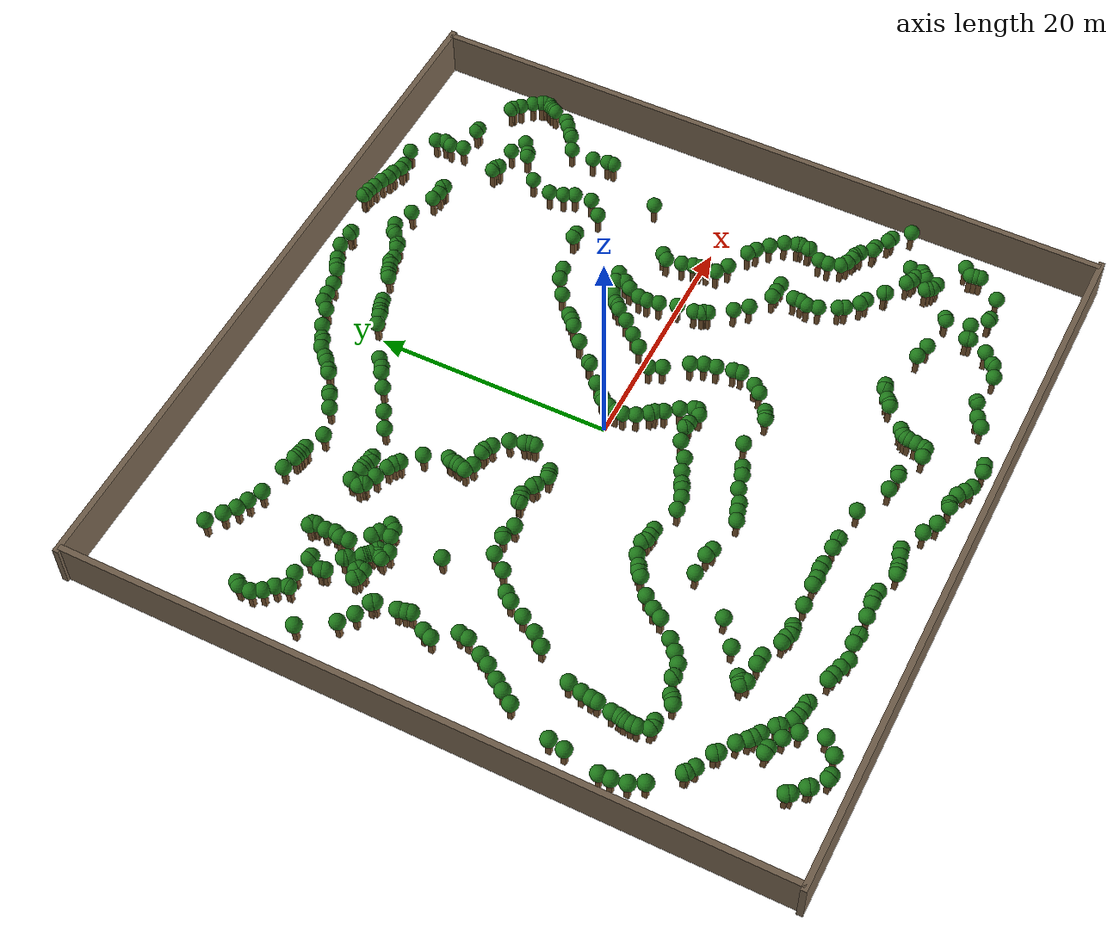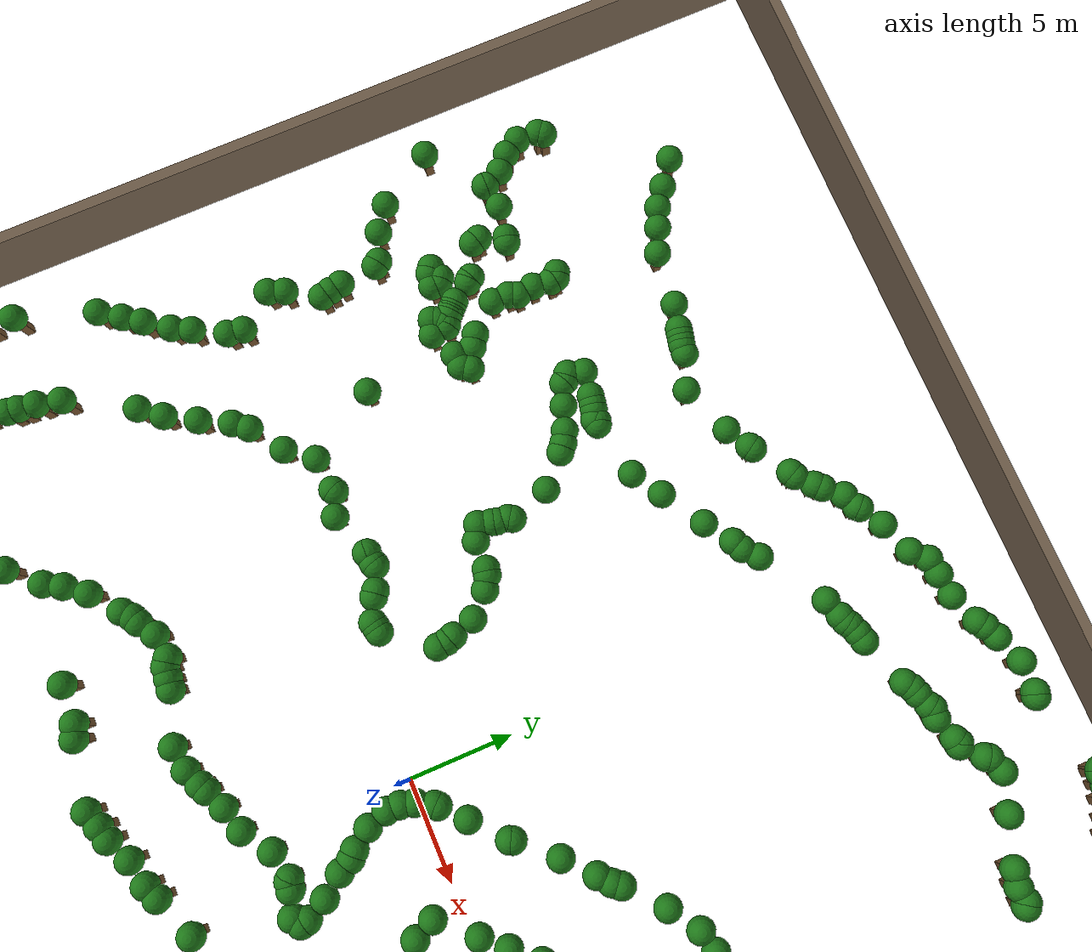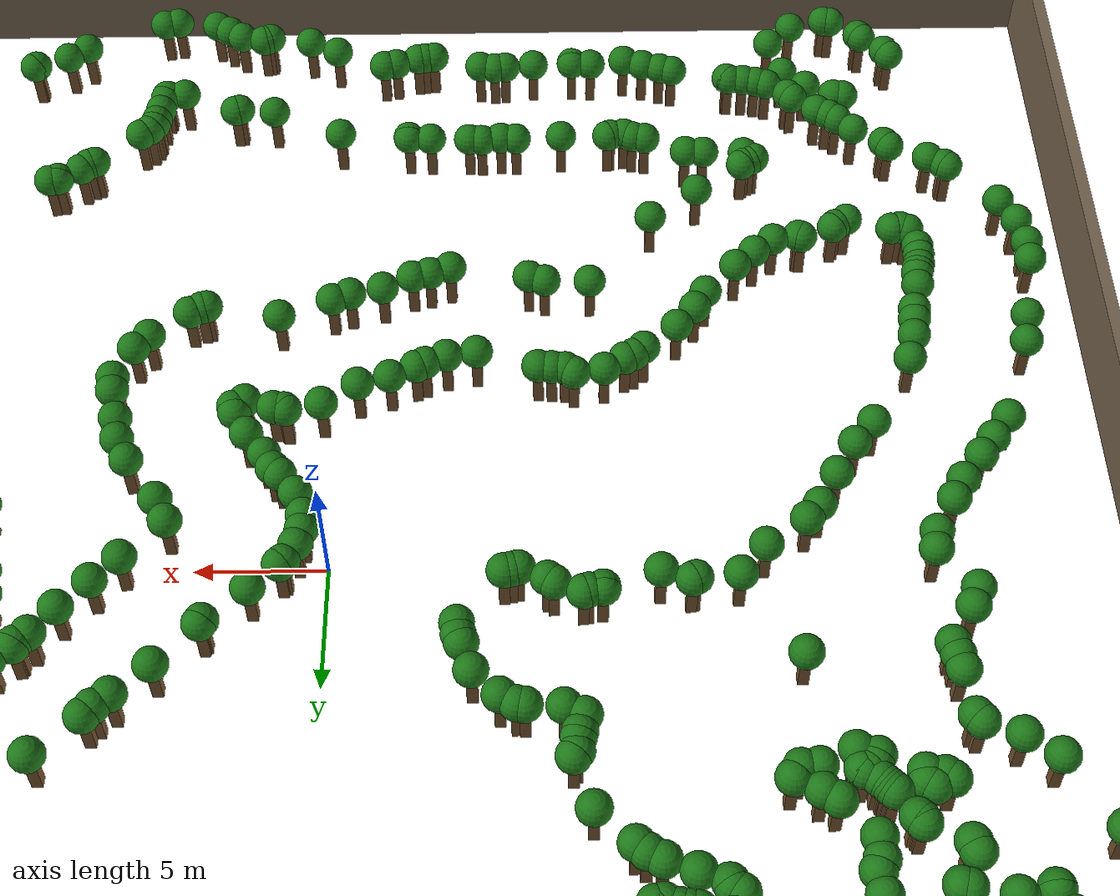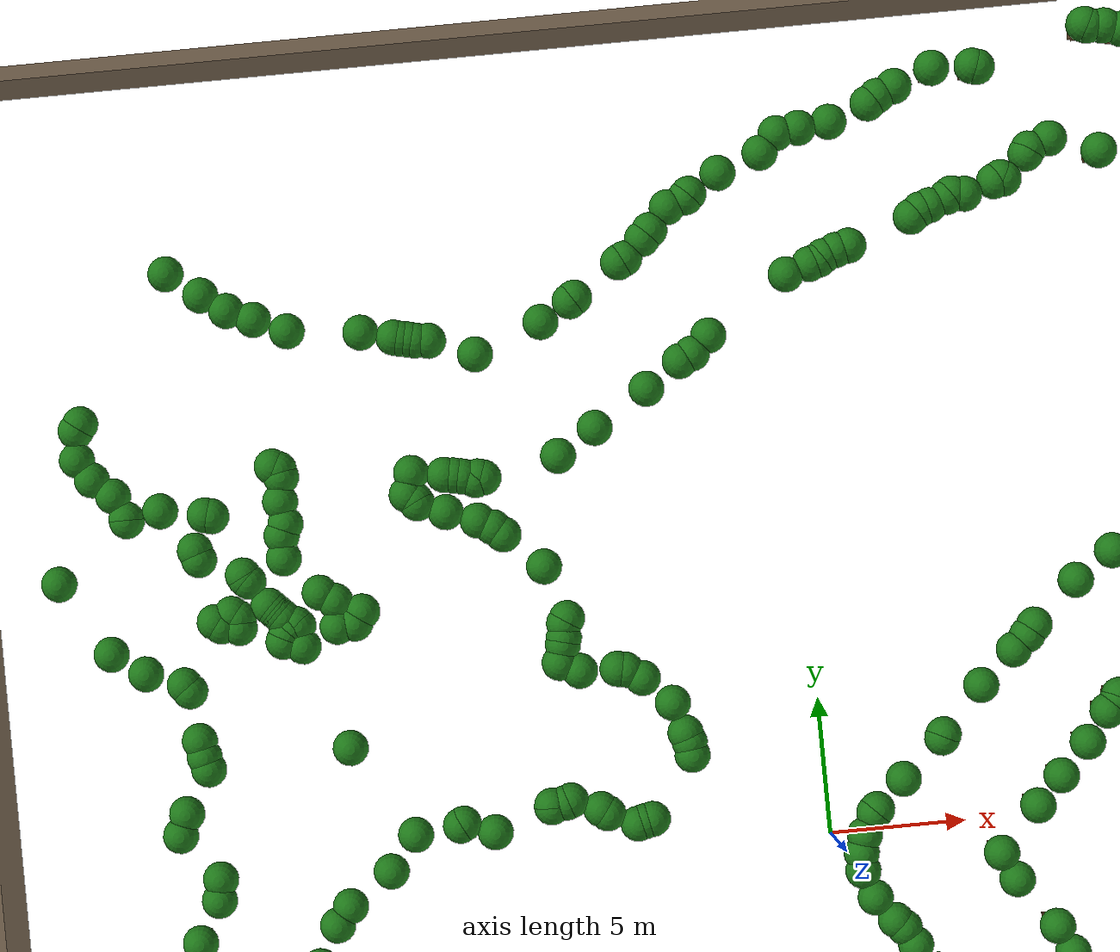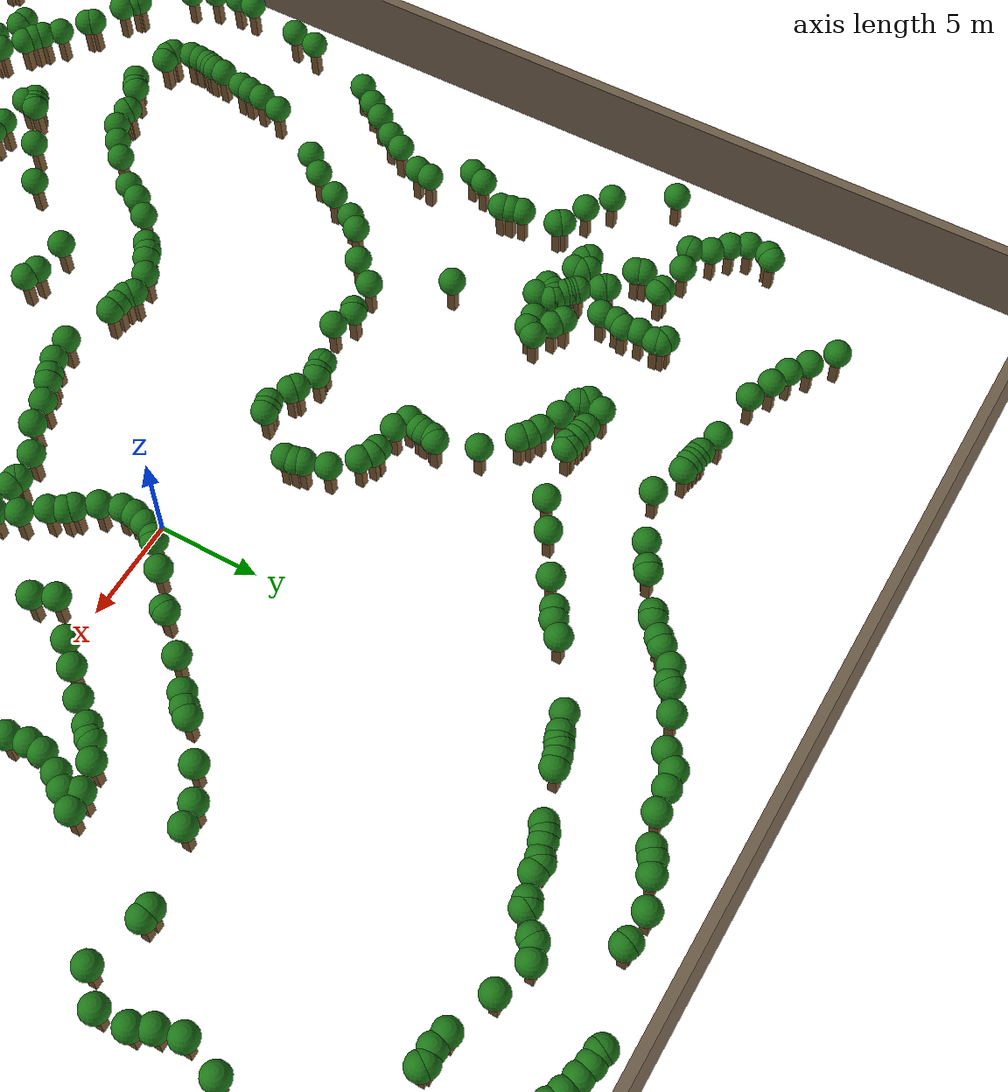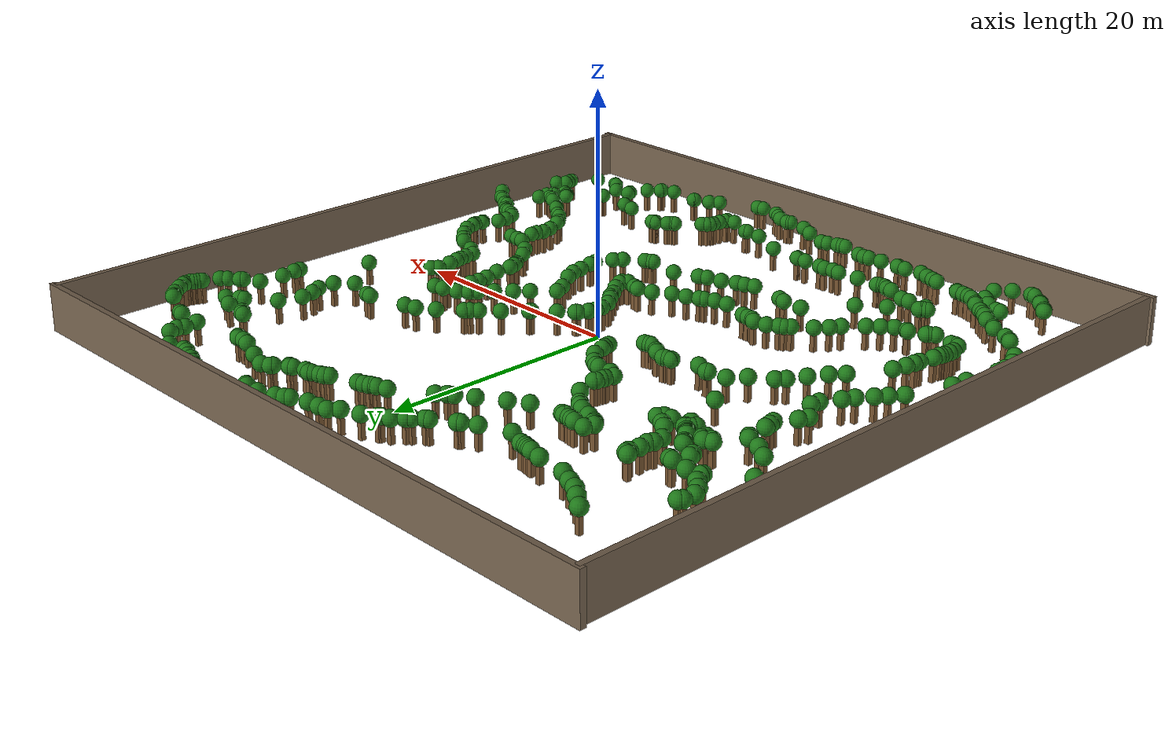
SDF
<sdf version="1.8">
 <world name="bush_trail_world">
  <light name="sun" type="directional">
   <cast_shadows>0</cast_shadows>
   <pose>0 0 100 0 -0 0</pose>
   <diffuse>0.8 0.8 0.8 1</diffuse>
   <specular>0.4 0.4 0.4 1</specular>
   <direction>-0.5 0.1 -0.9</direction>
  </light>
  <gravity>0 0 -9.81</gravity>
  <magnetic_field>6e-06 2.3e-05 -4.2e-05</magnetic_field>
  <atmosphere type="adiabatic"/>
  <physics name="default_physics" type="ignored">
   <max_step_size>0.01</max_step_size>
   <real_time_factor>1</real_time_factor>
   <real_time_update_rate>100</real_time_update_rate>
  </physics>
  <scene>
   <ambient>0.7 0.7 0.7 1</ambient>
   <background>0.6 0.8 1.0 1</background>
   <shadows>0</shadows>
   <grid>0</grid>
  </scene>
  <spherical_coordinates>
   <latitude_deg>0.0</latitude_deg>
   <longitude_deg>0.0</longitude_deg>
   <elevation>10.0</elevation>
   <heading_deg>0</heading_deg>
   <surface_model>EARTH_WGS84</surface_model>
  </spherical_coordinates>
  <include><uri>model://map_perimeter_60</uri><name>map_perimeter_60</name></include>
  <include><uri>model://bush_trail_nav_walls</uri><name>bush_trail_nav_walls</name></include>
 </world>
</sdf>

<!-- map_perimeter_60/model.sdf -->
<sdf version="1.7">
  <!-- Closed perimeter for 60 x 60 m heightmaps (origin-centred, X ±30, Y ±30).
       0.5 m thick boxes so gpu_lidar / SLAM see the boundary. -->
  <model name="map_perimeter_60">
    <static>true</static>

    <!-- West wall: x = -30, spans full Y (60 m) -->
    <link name="west">
      <collision name="collision">
        <pose>0 0 2 0 0 0</pose>
        <geometry>
          <box>
            <size>0.5 60 4</size>
          </box>
        </geometry>
      </collision>
      <visual name="visual">
        <pose>0 0 2 0 0 0</pose>
        <cast_shadows>false</cast_shadows>
        <geometry>
          <box>
            <size>0.5 60 4</size>
          </box>
        </geometry>
        <material>
          <ambient>0.35 0.30 0.25 1</ambient>
          <diffuse>0.45 0.38 0.30 1</diffuse>
        </material>
      </visual>
      <pose>-30 0 0 0 0 0</pose>
    </link>

    <!-- East wall: x = +30, spans full Y -->
    <link name="east">
      <collision name="collision">
        <pose>0 0 2 0 0 0</pose>
        <geometry>
          <box>
            <size>0.5 60 4</size>
          </box>
        </geometry>
      </collision>
      <visual name="visual">
        <pose>0 0 2 0 0 0</pose>
        <cast_shadows>false</cast_shadows>
        <geometry>
          <box>
            <size>0.5 60 4</size>
          </box>
        </geometry>
        <material>
          <ambient>0.35 0.30 0.25 1</ambient>
          <diffuse>0.45 0.38 0.30 1</diffuse>
        </material>
      </visual>
      <pose>30 0 0 0 0 0</pose>
    </link>

    <!-- South wall: y = -30; 61 m long so corners seal against east/west -->
    <link name="south">
      <collision name="collision">
        <pose>0 0 2 0 0 0</pose>
        <geometry>
          <box>
            <size>61 0.5 4</size>
          </box>
        </geometry>
      </collision>
      <visual name="visual">
        <pose>0 0 2 0 0 0</pose>
        <cast_shadows>false</cast_shadows>
        <geometry>
          <box>
            <size>61 0.5 4</size>
          </box>
        </geometry>
        <material>
          <ambient>0.35 0.30 0.25 1</ambient>
          <diffuse>0.45 0.38 0.30 1</diffuse>
        </material>
      </visual>
      <pose>0 -30 0 0 0 0</pose>
    </link>

    <!-- North wall: y = +30 -->
    <link name="north">
      <collision name="collision">
        <pose>0 0 2 0 0 0</pose>
        <geometry>
          <box>
            <size>61 0.5 4</size>
          </box>
        </geometry>
      </collision>
      <visual name="visual">
        <pose>0 0 2 0 0 0</pose>
        <cast_shadows>false</cast_shadows>
        <geometry>
          <box>
            <size>61 0.5 4</size>
          </box>
        </geometry>
        <material>
          <ambient>0.35 0.30 0.25 1</ambient>
          <diffuse>0.45 0.38 0.30 1</diffuse>
        </material>
      </visual>
      <pose>0 30 0 0 0 0</pose>
    </link>
  </model>
</sdf>

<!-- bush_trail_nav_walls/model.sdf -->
<sdf version='1.8'>
  <model name='bush_trail_nav_walls'>
    <static>true</static>
    <link name='trail_wall_1'>
      <pose>11.642 28.475 0.750 0 0 0</pose>
      <collision name="c"><geometry><box><size>0.400 0.400 1.500</size></box></geometry></collision>
      <visual name="v"><geometry><box><size>0.400 0.400 1.500</size></box></geometry><material><ambient>0.35 0.25 0.15 1</ambient><diffuse>0.45 0.32 0.18 1</diffuse></material></visual>
      <visual name="leaves"><pose>0 0 1.200 0 0 0</pose><geometry><sphere><radius>0.650</radius></sphere></geometry><material><ambient>0.08 0.35 0.08 1</ambient><diffuse>0.12 0.48 0.10 1</diffuse></material></visual>
    </link>
    <link name='trail_wall_2'>
      <pose>11.760 28.416 0.750 0 0 0</pose>
      <collision name="c"><geometry><box><size>0.400 0.400 1.500</size></box></geometry></collision>
      <visual name="v"><geometry><box><size>0.400 0.400 1.500</size></box></geometry><material><ambient>0.35 0.25 0.15 1</ambient><diffuse>0.45 0.32 0.18 1</diffuse></material></visual>
      <visual name="leaves"><pose>0 0 1.200 0 0 0</pose><geometry><sphere><radius>0.650</radius></sphere></geometry><material><ambient>0.08 0.35 0.08 1</ambient><diffuse>0.12 0.48 0.10 1</diffuse></material></visual>
    </link>
    <link name='trail_wall_3'>
      <pose>12.346 28.358 0.750 0 0 0</pose>
      <collision name="c"><geometry><box><size>0.400 0.400 1.500</size></box></geometry></collision>
      <visual name="v"><geometry><box><size>0.400 0.400 1.500</size></box></geometry><material><ambient>0.35 0.25 0.15 1</ambient><diffuse>0.45 0.32 0.18 1</diffuse></material></visual>
      <visual name="leaves"><pose>0 0 1.200 0 0 0</pose><geometry><sphere><radius>0.650</radius></sphere></geometry><material><ambient>0.08 0.35 0.08 1</ambient><diffuse>0.12 0.48 0.10 1</diffuse></material></visual>
    </link>
    <link name='trail_wall_4'>
      <pose>12.991 28.182 0.750 0 0 0</pose>
      <collision name="c"><geometry><box><size>0.400 0.400 1.500</size></box></geometry></collision>
      <visual name="v"><geometry><box><size>0.400 0.400 1.500</size></box></geometry><material><ambient>0.35 0.25 0.15 1</ambient><diffuse>0.45 0.32 0.18 1</diffuse></material></visual>
      <visual name="leaves"><pose>0 0 1.200 0 0 0</pose><geometry><sphere><radius>0.650</radius></sphere></geometry><material><ambient>0.08 0.35 0.08 1</ambient><diffuse>0.12 0.48 0.10 1</diffuse></material></visual>
    </link>
    <link name='trail_wall_5'>
      <pose>13.754 27.947 0.750 0 0 0</pose>
      <collision name="c"><geometry><box><size>0.400 0.400 1.500</size></box></geometry></collision>
      <visual name="v"><geometry><box><size>0.400 0.400 1.500</size></box></geometry><material><ambient>0.35 0.25 0.15 1</ambient><diffuse>0.45 0.32 0.18 1</diffuse></material></visual>
      <visual name="leaves"><pose>0 0 1.200 0 0 0</pose><geometry><sphere><radius>0.650</radius></sphere></geometry><material><ambient>0.08 0.35 0.08 1</ambient><diffuse>0.12 0.48 0.10 1</diffuse></material></visual>
    </link>
    <link name='trail_wall_6'>
      <pose>14.399 27.654 0.750 0 0 0</pose>
      <collision name="c"><geometry><box><size>0.400 0.400 1.500</size></box></geometry></collision>
      <visual name="v"><geometry><box><size>0.400 0.400 1.500</size></box></geometry><material><ambient>0.35 0.25 0.15 1</ambient><diffuse>0.45 0.32 0.18 1</diffuse></material></visual>
      <visual name="leaves"><pose>0 0 1.200 0 0 0</pose><geometry><sphere><radius>0.650</radius></sphere></geometry><material><ambient>0.08 0.35 0.08 1</ambient><diffuse>0.12 0.48 0.10 1</diffuse></material></visual>
    </link>
    <link name='trail_wall_7'>
      <pose>14.985 27.537 0.750 0 0 0</pose>
      <collision name="c"><geometry><box><size>0.400 0.400 1.500</size></box></geometry></collision>
      <visual name="v"><geometry><box><size>0.400 0.400 1.500</size></box></geometry><material><ambient>0.35 0.25 0.15 1</ambient><diffuse>0.45 0.32 0.18 1</diffuse></material></visual>
      <visual name="leaves"><pose>0 0 1.200 0 0 0</pose><geometry><sphere><radius>0.650</radius></sphere></geometry><material><ambient>0.08 0.35 0.08 1</ambient><diffuse>0.12 0.48 0.10 1</diffuse></material></visual>
    </link>
    <link name='trail_wall_8'>
      <pose>6.012 27.419 0.750 0 0 0</pose>
      <collision name="c"><geometry><box><size>0.400 0.400 1.500</size></box></geometry></collision>
      <visual name="v"><geometry><box><size>0.400 0.400 1.500</size></box></geometry><material><ambient>0.35 0.25 0.15 1</ambient><diffuse>0.45 0.32 0.18 1</diffuse></material></visual>
      <visual name="leaves"><pose>0 0 1.200 0 0 0</pose><geometry><sphere><radius>0.650</radius></sphere></geometry><material><ambient>0.08 0.35 0.08 1</ambient><diffuse>0.12 0.48 0.10 1</diffuse></material></visual>
    </link>
    <link name='trail_wall_9'>
      <pose>17.801 27.419 0.750 0 0 0</pose>
      <collision name="c"><geometry><box><size>0.400 0.400 1.500</size></box></geometry></collision>
      <visual name="v"><geometry><box><size>0.400 0.400 1.500</size></box></geometry><material><ambient>0.35 0.25 0.15 1</ambient><diffuse>0.45 0.32 0.18 1</diffuse></material></visual>
      <visual name="leaves"><pose>0 0 1.200 0 0 0</pose><geometry><sphere><radius>0.650</radius></sphere></geometry><material><ambient>0.08 0.35 0.08 1</ambient><diffuse>0.12 0.48 0.10 1</diffuse></material></visual>
    </link>
    <link name='trail_wall_10'>
      <pose>7.478 27.361 0.750 0 0 0</pose>
      <collision name="c"><geometry><box><size>0.400 0.400 1.500</size></box></geometry></collision>
      <visual name="v"><geometry><box><size>0.400 0.400 1.500</size></box></geometry><material><ambient>0.35 0.25 0.15 1</ambient><diffuse>0.45 0.32 0.18 1</diffuse></material></visual>
      <visual name="leaves"><pose>0 0 1.200 0 0 0</pose><geometry><sphere><radius>0.650</radius></sphere></geometry><material><ambient>0.08 0.35 0.08 1</ambient><diffuse>0.12 0.48 0.10 1</diffuse></material></visual>
    </link>
    <link name='trail_wall_11'>
      <pose>7.654 27.302 0.750 0 0 0</pose>
      <collision name="c"><geometry><box><size>0.400 0.400 1.500</size></box></geometry></collision>
      <visual name="v"><geometry><box><size>0.400 0.400 1.500</size></box></geometry><material><ambient>0.35 0.25 0.15 1</ambient><diffuse>0.45 0.32 0.18 1</diffuse></material></visual>
      <visual name="leaves"><pose>0 0 1.200 0 0 0</pose><geometry><sphere><radius>0.650</radius></sphere></geometry><material><ambient>0.08 0.35 0.08 1</ambient><diffuse>0.12 0.48 0.10 1</diffuse></material></visual>
    </link>
    <link name='trail_wall_12'>
      <pose>15.748 27.185 0.750 0 0 0</pose>
      <collision name="c"><geometry><box><size>0.400 0.400 1.500</size></box></geometry></collision>
      <visual name="v"><geometry><box><size>0.400 0.400 1.500</size></box></geometry><material><ambient>0.35 0.25 0.15 1</ambient><diffuse>0.45 0.32 0.18 1</diffuse></material></visual>
      <visual name="leaves"><pose>0 0 1.200 0 0 0</pose><geometry><sphere><radius>0.650</radius></sphere></geometry><material><ambient>0.08 0.35 0.08 1</ambient><diffuse>0.12 0.48 0.10 1</diffuse></material></visual>
    </link>
    <link name='trail_wall_13'>
      <pose>16.217 27.126 0.750 0 0 0</pose>
      <collision name="c"><geometry><box><size>0.400 0.400 1.500</size></box></geometry></collision>
      <visual name="v"><geometry><box><size>0.400 0.400 1.500</size></box></geometry><material><ambient>0.35 0.25 0.15 1</ambient><diffuse>0.45 0.32 0.18 1</diffuse></material></visual>
      <visual name="leaves"><pose>0 0 1.200 0 0 0</pose><geometry><sphere><radius>0.650</radius></sphere></geometry><material><ambient>0.08 0.35 0.08 1</ambient><diffuse>0.12 0.48 0.10 1</diffuse></material></visual>
    </link>
    <link name='trail_wall_14'>
      <pose>4.604 26.891 0.750 0 0 0</pose>
      <collision name="c"><geometry><box><size>0.400 0.400 1.500</size></box></geometry></collision>
      <visual name="v"><geometry><box><size>0.400 0.400 1.500</size></box></geometry><material><ambient>0.35 0.25 0.15 1</ambient><diffuse>0.45 0.32 0.18 1</diffuse></material></visual>
      <visual name="leaves"><pose>0 0 1.200 0 0 0</pose><geometry><sphere><radius>0.650</radius></sphere></geometry><material><ambient>0.08 0.35 0.08 1</ambient><diffuse>0.12 0.48 0.10 1</diffuse></material></visual>
    </link>
    <link name='trail_wall_15'>
      <pose>3.959 26.598 0.750 0 0 0</pose>
      <collision name="c"><geometry><box><size>0.400 0.400 1.500</size></box></geometry></collision>
      <visual name="v"><geometry><box><size>0.400 0.400 1.500</size></box></geometry><material><ambient>0.35 0.25 0.15 1</ambient><diffuse>0.45 0.32 0.18 1</diffuse></material></visual>
      <visual name="leaves"><pose>0 0 1.200 0 0 0</pose><geometry><sphere><radius>0.650</radius></sphere></geometry><material><ambient>0.08 0.35 0.08 1</ambient><diffuse>0.12 0.48 0.10 1</diffuse></material></visual>
    </link>
    <link name='trail_wall_16'>
      <pose>3.607 26.364 0.750 0 0 0</pose>
      <collision name="c"><geometry><box><size>0.400 0.400 1.500</size></box></geometry></collision>
      <visual name="v"><geometry><box><size>0.400 0.400 1.500</size></box></geometry><material><ambient>0.35 0.25 0.15 1</ambient><diffuse>0.45 0.32 0.18 1</diffuse></material></visual>
      <visual name="leaves"><pose>0 0 1.200 0 0 0</pose><geometry><sphere><radius>0.650</radius></sphere></geometry><material><ambient>0.08 0.35 0.08 1</ambient><diffuse>0.12 0.48 0.10 1</diffuse></material></visual>
    </link>
    <link name='trail_wall_17'>
      <pose>19.912 26.070 0.750 0 0 0</pose>
      <collision name="c"><geometry><box><size>0.400 0.400 1.500</size></box></geometry></collision>
      <visual name="v"><geometry><box><size>0.400 0.400 1.500</size></box></geometry><material><ambient>0.35 0.25 0.15 1</ambient><diffuse>0.45 0.32 0.18 1</diffuse></material></visual>
      <visual name="leaves"><pose>0 0 1.200 0 0 0</pose><geometry><sphere><radius>0.650</radius></sphere></geometry><material><ambient>0.08 0.35 0.08 1</ambient><diffuse>0.12 0.48 0.10 1</diffuse></material></visual>
    </link>
    <link name='trail_wall_18'>
      <pose>2.141 25.836 0.750 0 0 0</pose>
      <collision name="c"><geometry><box><size>0.400 0.400 1.500</size></box></geometry></collision>
      <visual name="v"><geometry><box><size>0.400 0.400 1.500</size></box></geometry><material><ambient>0.35 0.25 0.15 1</ambient><diffuse>0.45 0.32 0.18 1</diffuse></material></visual>
      <visual name="leaves"><pose>0 0 1.200 0 0 0</pose><geometry><sphere><radius>0.650</radius></sphere></geometry><material><ambient>0.08 0.35 0.08 1</ambient><diffuse>0.12 0.48 0.10 1</diffuse></material></visual>
    </link>
    <link name='trail_wall_19'>
      <pose>1.026 25.718 0.750 0 0 0</pose>
      <collision name="c"><geometry><box><size>0.400 0.400 1.500</size></box></geometry></collision>
      <visual name="v"><geometry><box><size>0.400 0.400 1.500</size></box></geometry><material><ambient>0.35 0.25 0.15 1</ambient><diffuse>0.45 0.32 0.18 1</diffuse></material></visual>
      <visual name="leaves"><pose>0 0 1.200 0 0 0</pose><geometry><sphere><radius>0.650</radius></sphere></geometry><material><ambient>0.08 0.35 0.08 1</ambient><diffuse>0.12 0.48 0.10 1</diffuse></material></visual>
    </link>
    <link name='trail_wall_20'>
      <pose>0.205 25.601 0.750 0 0 0</pose>
      <collision name="c"><geometry><box><size>0.400 0.400 1.500</size></box></geometry></collision>
      <visual name="v"><geometry><box><size>0.400 0.400 1.500</size></box></geometry><material><ambient>0.35 0.25 0.15 1</ambient><diffuse>0.45 0.32 0.18 1</diffuse></material></visual>
      <visual name="leaves"><pose>0 0 1.200 0 0 0</pose><geometry><sphere><radius>0.650</radius></sphere></geometry><material><ambient>0.08 0.35 0.08 1</ambient><diffuse>0.12 0.48 0.10 1</diffuse></material></visual>
    </link>
    <link name='trail_wall_21'>
      <pose>20.147 25.308 0.750 0 0 0</pose>
      <collision name="c"><geometry><box><size>0.400 0.400 1.500</size></box></geometry></collision>
      <visual name="v"><geometry><box><size>0.400 0.400 1.500</size></box></geometry><material><ambient>0.35 0.25 0.15 1</ambient><diffuse>0.45 0.32 0.18 1</diffuse></material></visual>
      <visual name="leaves"><pose>0 0 1.200 0 0 0</pose><geometry><sphere><radius>0.650</radius></sphere></geometry><material><ambient>0.08 0.35 0.08 1</ambient><diffuse>0.12 0.48 0.10 1</diffuse></material></visual>
    </link>
    <link name='trail_wall_22'>
      <pose>-0.440 24.956 0.750 0 0 0</pose>
      <collision name="c"><geometry><box><size>0.400 0.400 1.500</size></box></geometry></collision>
      <visual name="v"><geometry><box><size>0.400 0.400 1.500</size></box></geometry><material><ambient>0.35 0.25 0.15 1</ambient><diffuse>0.45 0.32 0.18 1</diffuse></material></visual>
      <visual name="leaves"><pose>0 0 1.200 0 0 0</pose><geometry><sphere><radius>0.650</radius></sphere></geometry><material><ambient>0.08 0.35 0.08 1</ambient><diffuse>0.12 0.48 0.10 1</diffuse></material></visual>
    </link>
    <link name='trail_wall_23'>
      <pose>19.971 24.721 0.750 0 0 0</pose>
      <collision name="c"><geometry><box><size>0.400 0.400 1.500</size></box></geometry></collision>
      <visual name="v"><geometry><box><size>0.400 0.400 1.500</size></box></geometry><material><ambient>0.35 0.25 0.15 1</ambient><diffuse>0.45 0.32 0.18 1</diffuse></material></visual>
      <visual name="leaves"><pose>0 0 1.200 0 0 0</pose><geometry><sphere><radius>0.650</radius></sphere></geometry><material><ambient>0.08 0.35 0.08 1</ambient><diffuse>0.12 0.48 0.10 1</diffuse></material></visual>
    </link>
    <link name='trail_wall_24'>
      <pose>10.000 24.487 0.750 0 0 0</pose>
      <collision name="c"><geometry><box><size>0.400 0.400 1.500</size></box></geometry></collision>
      <visual name="v"><geometry><box><size>0.400 0.400 1.500</size></box></geometry><material><ambient>0.35 0.25 0.15 1</ambient><diffuse>0.45 0.32 0.18 1</diffuse></material></visual>
      <visual name="leaves"><pose>0 0 1.200 0 0 0</pose><geometry><sphere><radius>0.650</radius></sphere></geometry><material><ambient>0.08 0.35 0.08 1</ambient><diffuse>0.12 0.48 0.10 1</diffuse></material></visual>
    </link>
    <link name='trail_wall_25'>
      <pose>-2.023 24.370 0.750 0 0 0</pose>
      <collision name="c"><geometry><box><size>0.400 0.400 1.500</size></box></geometry></collision>
      <visual name="v"><geometry><box><size>0.400 0.400 1.500</size></box></geometry><material><ambient>0.35 0.25 0.15 1</ambient><diffuse>0.45 0.32 0.18 1</diffuse></material></visual>
      <visual name="leaves"><pose>0 0 1.200 0 0 0</pose><geometry><sphere><radius>0.650</radius></sphere></geometry><material><ambient>0.08 0.35 0.08 1</ambient><diffuse>0.12 0.48 0.10 1</diffuse></material></visual>
    </link>
    <link name='trail_wall_26'>
      <pose>9.238 24.194 0.750 0 0 0</pose>
      <collision name="c"><geometry><box><size>0.400 0.400 1.500</size></box></geometry></collision>
      <visual name="v"><geometry><box><size>0.400 0.400 1.500</size></box></geometry><material><ambient>0.35 0.25 0.15 1</ambient><diffuse>0.45 0.32 0.18 1</diffuse></material></visual>
      <visual name="leaves"><pose>0 0 1.200 0 0 0</pose><geometry><sphere><radius>0.650</radius></sphere></geometry><material><ambient>0.08 0.35 0.08 1</ambient><diffuse>0.12 0.48 0.10 1</diffuse></material></visual>
    </link>
    <link name='trail_wall_27'>
      <pose>9.120 24.018 0.750 0 0 0</pose>
      <collision name="c"><geometry><box><size>0.400 0.400 1.500</size></box></geometry></collision>
      <visual name="v"><geometry><box><size>0.400 0.400 1.500</size></box></geometry><material><ambient>0.35 0.25 0.15 1</ambient><diffuse>0.45 0.32 0.18 1</diffuse></material></visual>
      <visual name="leaves"><pose>0 0 1.200 0 0 0</pose><geometry><sphere><radius>0.650</radius></sphere></geometry><material><ambient>0.08 0.35 0.08 1</ambient><diffuse>0.12 0.48 0.10 1</diffuse></material></visual>
    </link>
    <link name='trail_wall_28'>
      <pose>11.760 23.900 0.750 0 0 0</pose>
      <collision name="c"><geometry><box><size>0.400 0.400 1.500</size></box></geometry></collision>
      <visual name="v"><geometry><box><size>0.400 0.400 1.500</size></box></geometry><material><ambient>0.35 0.25 0.15 1</ambient><diffuse>0.45 0.32 0.18 1</diffuse></material></visual>
      <visual name="leaves"><pose>0 0 1.200 0 0 0</pose><geometry><sphere><radius>0.650</radius></sphere></geometry><material><ambient>0.08 0.35 0.08 1</ambient><diffuse>0.12 0.48 0.10 1</diffuse></material></visual>
    </link>
    <link name='trail_wall_29'>
      <pose>-3.138 23.724 0.750 0 0 0</pose>
      <collision name="c"><geometry><box><size>0.400 0.400 1.500</size></box></geometry></collision>
      <visual name="v"><geometry><box><size>0.400 0.400 1.500</size></box></geometry><material><ambient>0.35 0.25 0.15 1</ambient><diffuse>0.45 0.32 0.18 1</diffuse></material></visual>
      <visual name="leaves"><pose>0 0 1.200 0 0 0</pose><geometry><sphere><radius>0.650</radius></sphere></geometry><material><ambient>0.08 0.35 0.08 1</ambient><diffuse>0.12 0.48 0.10 1</diffuse></material></visual>
    </link>
    <link name='trail_wall_30'>
      <pose>-3.255 23.607 0.750 0 0 0</pose>
      <collision name="c"><geometry><box><size>0.400 0.400 1.500</size></box></geometry></collision>
      <visual name="v"><geometry><box><size>0.400 0.400 1.500</size></box></geometry><material><ambient>0.35 0.25 0.15 1</ambient><diffuse>0.45 0.32 0.18 1</diffuse></material></visual>
      <visual name="leaves"><pose>0 0 1.200 0 0 0</pose><geometry><sphere><radius>0.650</radius></sphere></geometry><material><ambient>0.08 0.35 0.08 1</ambient><diffuse>0.12 0.48 0.10 1</diffuse></material></visual>
    </link>
    <link name='trail_wall_31'>
      <pose>20.147 23.548 0.750 0 0 0</pose>
      <collision name="c"><geometry><box><size>0.400 0.400 1.500</size></box></geometry></collision>
      <visual name="v"><geometry><box><size>0.400 0.400 1.500</size></box></geometry><material><ambient>0.35 0.25 0.15 1</ambient><diffuse>0.45 0.32 0.18 1</diffuse></material></visual>
      <visual name="leaves"><pose>0 0 1.200 0 0 0</pose><geometry><sphere><radius>0.650</radius></sphere></geometry><material><ambient>0.08 0.35 0.08 1</ambient><diffuse>0.12 0.48 0.10 1</diffuse></material></visual>
    </link>
    <link name='trail_wall_32'>
      <pose>22.434 23.490 0.750 0 0 0</pose>
      <collision name="c"><geometry><box><size>0.400 0.400 1.500</size></box></geometry></collision>
      <visual name="v"><geometry><box><size>0.400 0.400 1.500</size></box></geometry><material><ambient>0.35 0.25 0.15 1</ambient><diffuse>0.45 0.32 0.18 1</diffuse></material></visual>
      <visual name="leaves"><pose>0 0 1.200 0 0 0</pose><geometry><sphere><radius>0.650</radius></sphere></geometry><material><ambient>0.08 0.35 0.08 1</ambient><diffuse>0.12 0.48 0.10 1</diffuse></material></visual>
    </link>
    <link name='trail_wall_33'>
      <pose>22.727 23.431 0.750 0 0 0</pose>
      <collision name="c"><geometry><box><size>0.400 0.400 1.500</size></box></geometry></collision>
      <visual name="v"><geometry><box><size>0.400 0.400 1.500</size></box></geometry><material><ambient>0.35 0.25 0.15 1</ambient><diffuse>0.45 0.32 0.18 1</diffuse></material></visual>
      <visual name="leaves"><pose>0 0 1.200 0 0 0</pose><geometry><sphere><radius>0.650</radius></sphere></geometry><material><ambient>0.08 0.35 0.08 1</ambient><diffuse>0.12 0.48 0.10 1</diffuse></material></visual>
    </link>
    <link name='trail_wall_34'>
      <pose>-3.959 23.314 0.750 0 0 0</pose>
      <collision name="c"><geometry><box><size>0.400 0.400 1.500</size></box></geometry></collision>
      <visual name="v"><geometry><box><size>0.400 0.400 1.500</size></box></geometry><material><ambient>0.35 0.25 0.15 1</ambient><diffuse>0.45 0.32 0.18 1</diffuse></material></visual>
      <visual name="leaves"><pose>0 0 1.200 0 0 0</pose><geometry><sphere><radius>0.650</radius></sphere></geometry><material><ambient>0.08 0.35 0.08 1</ambient><diffuse>0.12 0.48 0.10 1</diffuse></material></visual>
    </link>
    <link name='trail_wall_35'>
      <pose>8.123 23.255 0.750 0 0 0</pose>
      <collision name="c"><geometry><box><size>0.400 0.400 1.500</size></box></geometry></collision>
      <visual name="v"><geometry><box><size>0.400 0.400 1.500</size></box></geometry><material><ambient>0.35 0.25 0.15 1</ambient><diffuse>0.45 0.32 0.18 1</diffuse></material></visual>
      <visual name="leaves"><pose>0 0 1.200 0 0 0</pose><geometry><sphere><radius>0.650</radius></sphere></geometry><material><ambient>0.08 0.35 0.08 1</ambient><diffuse>0.12 0.48 0.10 1</diffuse></material></visual>
    </link>
    <link name='trail_wall_36'>
      <pose>8.240 23.196 0.750 0 0 0</pose>
      <collision name="c"><geometry><box><size>0.400 0.400 1.500</size></box></geometry></collision>
      <visual name="v"><geometry><box><size>0.400 0.400 1.500</size></box></geometry><material><ambient>0.35 0.25 0.15 1</ambient><diffuse>0.45 0.32 0.18 1</diffuse></material></visual>
      <visual name="leaves"><pose>0 0 1.200 0 0 0</pose><geometry><sphere><radius>0.650</radius></sphere></geometry><material><ambient>0.08 0.35 0.08 1</ambient><diffuse>0.12 0.48 0.10 1</diffuse></material></visual>
    </link>
    <link name='trail_wall_37'>
      <pose>7.889 23.138 0.750 0 0 0</pose>
      <collision name="c"><geometry><box><size>0.400 0.400 1.500</size></box></geometry></collision>
      <visual name="v"><geometry><box><size>0.400 0.400 1.500</size></box></geometry><material><ambient>0.35 0.25 0.15 1</ambient><diffuse>0.45 0.32 0.18 1</diffuse></material></visual>
      <visual name="leaves"><pose>0 0 1.200 0 0 0</pose><geometry><sphere><radius>0.650</radius></sphere></geometry><material><ambient>0.08 0.35 0.08 1</ambient><diffuse>0.12 0.48 0.10 1</diffuse></material></visual>
    </link>
    <link name='trail_wall_38'>
      <pose>13.930 23.079 0.750 0 0 0</pose>
      <collision name="c"><geometry><box><size>0.400 0.400 1.500</size></box></geometry></collision>
      <visual name="v"><geometry><box><size>0.400 0.400 1.500</size></box></geometry><material><ambient>0.35 0.25 0.15 1</ambient><diffuse>0.45 0.32 0.18 1</diffuse></material></visual>
      <visual name="leaves"><pose>0 0 1.200 0 0 0</pose><geometry><sphere><radius>0.650</radius></sphere></geometry><material><ambient>0.08 0.35 0.08 1</ambient><diffuse>0.12 0.48 0.10 1</diffuse></material></visual>
    </link>
    <link name='trail_wall_39'>
      <pose>15.337 22.962 0.750 0 0 0</pose>
      <collision name="c"><geometry><box><size>0.400 0.400 1.500</size></box></geometry></collision>
      <visual name="v"><geometry><box><size>0.400 0.400 1.500</size></box></geometry><material><ambient>0.35 0.25 0.15 1</ambient><diffuse>0.45 0.32 0.18 1</diffuse></material></visual>
      <visual name="leaves"><pose>0 0 1.200 0 0 0</pose><geometry><sphere><radius>0.650</radius></sphere></geometry><material><ambient>0.08 0.35 0.08 1</ambient><diffuse>0.12 0.48 0.10 1</diffuse></material></visual>
    </link>
    <link name='trail_wall_40'>
      <pose>14.692 22.903 0.750 0 0 0</pose>
      <collision name="c"><geometry><box><size>0.400 0.400 1.500</size></box></geometry></collision>
      <visual name="v"><geometry><box><size>0.400 0.400 1.500</size></box></geometry><material><ambient>0.35 0.25 0.15 1</ambient><diffuse>0.45 0.32 0.18 1</diffuse></material></visual>
      <visual name="leaves"><pose>0 0 1.200 0 0 0</pose><geometry><sphere><radius>0.650</radius></sphere></geometry><material><ambient>0.08 0.35 0.08 1</ambient><diffuse>0.12 0.48 0.10 1</diffuse></material></visual>
    </link>
    <link name='trail_wall_41'>
      <pose>6.305 22.845 0.750 0 0 0</pose>
      <collision name="c"><geometry><box><size>0.400 0.400 1.500</size></box></geometry></collision>
      <visual name="v"><geometry><box><size>0.400 0.400 1.500</size></box></geometry><material><ambient>0.35 0.25 0.15 1</ambient><diffuse>0.45 0.32 0.18 1</diffuse></material></visual>
      <visual name="leaves"><pose>0 0 1.200 0 0 0</pose><geometry><sphere><radius>0.650</radius></sphere></geometry><material><ambient>0.08 0.35 0.08 1</ambient><diffuse>0.12 0.48 0.10 1</diffuse></material></visual>
    </link>
    <link name='trail_wall_42'>
      <pose>15.513 22.845 0.750 0 0 0</pose>
      <collision name="c"><geometry><box><size>0.400 0.400 1.500</size></box></geometry></collision>
      <visual name="v"><geometry><box><size>0.400 0.400 1.500</size></box></geometry><material><ambient>0.35 0.25 0.15 1</ambient><diffuse>0.45 0.32 0.18 1</diffuse></material></visual>
      <visual name="leaves"><pose>0 0 1.200 0 0 0</pose><geometry><sphere><radius>0.650</radius></sphere></geometry><material><ambient>0.08 0.35 0.08 1</ambient><diffuse>0.12 0.48 0.10 1</diffuse></material></visual>
    </link>
    <link name='trail_wall_43'>
      <pose>6.774 22.786 0.750 0 0 0</pose>
      <collision name="c"><geometry><box><size>0.400 0.400 1.500</size></box></geometry></collision>
      <visual name="v"><geometry><box><size>0.400 0.400 1.500</size></box></geometry><material><ambient>0.35 0.25 0.15 1</ambient><diffuse>0.45 0.32 0.18 1</diffuse></material></visual>
      <visual name="leaves"><pose>0 0 1.200 0 0 0</pose><geometry><sphere><radius>0.650</radius></sphere></geometry><material><ambient>0.08 0.35 0.08 1</ambient><diffuse>0.12 0.48 0.10 1</diffuse></material></visual>
    </link>
    <link name='trail_wall_44'>
      <pose>6.129 22.727 0.750 0 0 0</pose>
      <collision name="c"><geometry><box><size>0.400 0.400 1.500</size></box></geometry></collision>
      <visual name="v"><geometry><box><size>0.400 0.400 1.500</size></box></geometry><material><ambient>0.35 0.25 0.15 1</ambient><diffuse>0.45 0.32 0.18 1</diffuse></material></visual>
      <visual name="leaves"><pose>0 0 1.200 0 0 0</pose><geometry><sphere><radius>0.650</radius></sphere></geometry><material><ambient>0.08 0.35 0.08 1</ambient><diffuse>0.12 0.48 0.10 1</diffuse></material></visual>
    </link>
    <link name='trail_wall_45'>
      <pose>-22.199 22.610 0.750 0 0 0</pose>
      <collision name="c"><geometry><box><size>0.400 0.400 1.500</size></box></geometry></collision>
      <visual name="v"><geometry><box><size>0.400 0.400 1.500</size></box></geometry><material><ambient>0.35 0.25 0.15 1</ambient><diffuse>0.45 0.32 0.18 1</diffuse></material></visual>
      <visual name="leaves"><pose>0 0 1.200 0 0 0</pose><geometry><sphere><radius>0.650</radius></sphere></geometry><material><ambient>0.08 0.35 0.08 1</ambient><diffuse>0.12 0.48 0.10 1</diffuse></material></visual>
    </link>
    <link name='trail_wall_46'>
      <pose>-4.663 22.551 0.750 0 0 0</pose>
      <collision name="c"><geometry><box><size>0.400 0.400 1.500</size></box></geometry></collision>
      <visual name="v"><geometry><box><size>0.400 0.400 1.500</size></box></geometry><material><ambient>0.35 0.25 0.15 1</ambient><diffuse>0.45 0.32 0.18 1</diffuse></material></visual>
      <visual name="leaves"><pose>0 0 1.200 0 0 0</pose><geometry><sphere><radius>0.650</radius></sphere></geometry><material><ambient>0.08 0.35 0.08 1</ambient><diffuse>0.12 0.48 0.10 1</diffuse></material></visual>
    </link>
    <link name='trail_wall_47'>
      <pose>5.484 22.493 0.750 0 0 0</pose>
      <collision name="c"><geometry><box><size>0.400 0.400 1.500</size></box></geometry></collision>
      <visual name="v"><geometry><box><size>0.400 0.400 1.500</size></box></geometry><material><ambient>0.35 0.25 0.15 1</ambient><diffuse>0.45 0.32 0.18 1</diffuse></material></visual>
      <visual name="leaves"><pose>0 0 1.200 0 0 0</pose><geometry><sphere><radius>0.650</radius></sphere></geometry><material><ambient>0.08 0.35 0.08 1</ambient><diffuse>0.12 0.48 0.10 1</diffuse></material></visual>
    </link>
    <link name='trail_wall_48'>
      <pose>5.132 22.375 0.750 0 0 0</pose>
      <collision name="c"><geometry><box><size>0.400 0.400 1.500</size></box></geometry></collision>
      <visual name="v"><geometry><box><size>0.400 0.400 1.500</size></box></geometry><material><ambient>0.35 0.25 0.15 1</ambient><diffuse>0.45 0.32 0.18 1</diffuse></material></visual>
      <visual name="leaves"><pose>0 0 1.200 0 0 0</pose><geometry><sphere><radius>0.650</radius></sphere></geometry><material><ambient>0.08 0.35 0.08 1</ambient><diffuse>0.12 0.48 0.10 1</diffuse></material></visual>
    </link>
    <link name='trail_wall_49'>
      <pose>-4.956 22.258 0.750 0 0 0</pose>
      <collision name="c"><geometry><box><size>0.400 0.400 1.500</size></box></geometry></collision>
      <visual name="v"><geometry><box><size>0.400 0.400 1.500</size></box></geometry><material><ambient>0.35 0.25 0.15 1</ambient><diffuse>0.45 0.32 0.18 1</diffuse></material></visual>
      <visual name="leaves"><pose>0 0 1.200 0 0 0</pose><geometry><sphere><radius>0.650</radius></sphere></geometry><material><ambient>0.08 0.35 0.08 1</ambient><diffuse>0.12 0.48 0.10 1</diffuse></material></visual>
    </link>
    <link name='trail_wall_50'>
      <pose>4.780 22.141 0.750 0 0 0</pose>
      <collision name="c"><geometry><box><size>0.400 0.400 1.500</size></box></geometry></collision>
      <visual name="v"><geometry><box><size>0.400 0.400 1.500</size></box></geometry><material><ambient>0.35 0.25 0.15 1</ambient><diffuse>0.45 0.32 0.18 1</diffuse></material></visual>
      <visual name="leaves"><pose>0 0 1.200 0 0 0</pose><geometry><sphere><radius>0.650</radius></sphere></geometry><material><ambient>0.08 0.35 0.08 1</ambient><diffuse>0.12 0.48 0.10 1</diffuse></material></visual>
    </link>
    <link name='trail_wall_51'>
      <pose>26.070 22.023 0.750 0 0 0</pose>
      <collision name="c"><geometry><box><size>0.400 0.400 1.500</size></box></geometry></collision>
      <visual name="v"><geometry><box><size>0.400 0.400 1.500</size></box></geometry><material><ambient>0.35 0.25 0.15 1</ambient><diffuse>0.45 0.32 0.18 1</diffuse></material></visual>
      <visual name="leaves"><pose>0 0 1.200 0 0 0</pose><geometry><sphere><radius>0.650</radius></sphere></geometry><material><ambient>0.08 0.35 0.08 1</ambient><diffuse>0.12 0.48 0.10 1</diffuse></material></visual>
    </link>
    <link name='trail_wall_52'>
      <pose>26.305 21.906 0.750 0 0 0</pose>
      <collision name="c"><geometry><box><size>0.400 0.400 1.500</size></box></geometry></collision>
      <visual name="v"><geometry><box><size>0.400 0.400 1.500</size></box></geometry><material><ambient>0.35 0.25 0.15 1</ambient><diffuse>0.45 0.32 0.18 1</diffuse></material></visual>
      <visual name="leaves"><pose>0 0 1.200 0 0 0</pose><geometry><sphere><radius>0.650</radius></sphere></geometry><material><ambient>0.08 0.35 0.08 1</ambient><diffuse>0.12 0.48 0.10 1</diffuse></material></visual>
    </link>
    <link name='trail_wall_53'>
      <pose>-21.026 21.730 0.750 0 0 0</pose>
      <collision name="c"><geometry><box><size>0.400 0.400 1.500</size></box></geometry></collision>
      <visual name="v"><geometry><box><size>0.400 0.400 1.500</size></box></geometry><material><ambient>0.35 0.25 0.15 1</ambient><diffuse>0.45 0.32 0.18 1</diffuse></material></visual>
      <visual name="leaves"><pose>0 0 1.200 0 0 0</pose><geometry><sphere><radius>0.650</radius></sphere></geometry><material><ambient>0.08 0.35 0.08 1</ambient><diffuse>0.12 0.48 0.10 1</diffuse></material></visual>
    </link>
    <link name='trail_wall_54'>
      <pose>-5.660 21.613 0.750 0 0 0</pose>
      <collision name="c"><geometry><box><size>0.400 0.400 1.500</size></box></geometry></collision>
      <visual name="v"><geometry><box><size>0.400 0.400 1.500</size></box></geometry><material><ambient>0.35 0.25 0.15 1</ambient><diffuse>0.45 0.32 0.18 1</diffuse></material></visual>
      <visual name="leaves"><pose>0 0 1.200 0 0 0</pose><geometry><sphere><radius>0.650</radius></sphere></geometry><material><ambient>0.08 0.35 0.08 1</ambient><diffuse>0.12 0.48 0.10 1</diffuse></material></visual>
    </link>
    <link name='trail_wall_55'>
      <pose>-5.894 21.496 0.750 0 0 0</pose>
      <collision name="c"><geometry><box><size>0.400 0.400 1.500</size></box></geometry></collision>
      <visual name="v"><geometry><box><size>0.400 0.400 1.500</size></box></geometry><material><ambient>0.35 0.25 0.15 1</ambient><diffuse>0.45 0.32 0.18 1</diffuse></material></visual>
      <visual name="leaves"><pose>0 0 1.200 0 0 0</pose><geometry><sphere><radius>0.650</radius></sphere></geometry><material><ambient>0.08 0.35 0.08 1</ambient><diffuse>0.12 0.48 0.10 1</diffuse></material></visual>
    </link>
    <link name='trail_wall_56'>
      <pose>26.774 21.437 0.750 0 0 0</pose>
      <collision name="c"><geometry><box><size>0.400 0.400 1.500</size></box></geometry></collision>
      <visual name="v"><geometry><box><size>0.400 0.400 1.500</size></box></geometry><material><ambient>0.35 0.25 0.15 1</ambient><diffuse>0.45 0.32 0.18 1</diffuse></material></visual>
      <visual name="leaves"><pose>0 0 1.200 0 0 0</pose><geometry><sphere><radius>0.650</radius></sphere></geometry><material><ambient>0.08 0.35 0.08 1</ambient><diffuse>0.12 0.48 0.10 1</diffuse></material></visual>
    </link>
    <link name='trail_wall_57'>
      <pose>2.434 21.320 0.750 0 0 0</pose>
      <collision name="c"><geometry><box><size>0.400 0.400 1.500</size></box></geometry></collision>
      <visual name="v"><geometry><box><size>0.400 0.400 1.500</size></box></geometry><material><ambient>0.35 0.25 0.15 1</ambient><diffuse>0.45 0.32 0.18 1</diffuse></material></visual>
      <visual name="leaves"><pose>0 0 1.200 0 0 0</pose><geometry><sphere><radius>0.650</radius></sphere></geometry><material><ambient>0.08 0.35 0.08 1</ambient><diffuse>0.12 0.48 0.10 1</diffuse></material></visual>
    </link>
    <link name='trail_wall_58'>
      <pose>1.965 21.202 0.750 0 0 0</pose>
      <collision name="c"><geometry><box><size>0.400 0.400 1.500</size></box></geometry></collision>
      <visual name="v"><geometry><box><size>0.400 0.400 1.500</size></box></geometry><material><ambient>0.35 0.25 0.15 1</ambient><diffuse>0.45 0.32 0.18 1</diffuse></material></visual>
      <visual name="leaves"><pose>0 0 1.200 0 0 0</pose><geometry><sphere><radius>0.650</radius></sphere></geometry><material><ambient>0.08 0.35 0.08 1</ambient><diffuse>0.12 0.48 0.10 1</diffuse></material></visual>
    </link>
    <link name='trail_wall_59'>
      <pose>-20.147 21.085 0.750 0 0 0</pose>
      <collision name="c"><geometry><box><size>0.400 0.400 1.500</size></box></geometry></collision>
      <visual name="v"><geometry><box><size>0.400 0.400 1.500</size></box></geometry><material><ambient>0.35 0.25 0.15 1</ambient><diffuse>0.45 0.32 0.18 1</diffuse></material></visual>
      <visual name="leaves"><pose>0 0 1.200 0 0 0</pose><geometry><sphere><radius>0.650</radius></sphere></geometry><material><ambient>0.08 0.35 0.08 1</ambient><diffuse>0.12 0.48 0.10 1</diffuse></material></visual>
    </link>
    <link name='trail_wall_60'>
      <pose>1.496 21.026 0.750 0 0 0</pose>
      <collision name="c"><geometry><box><size>0.400 0.400 1.500</size></box></geometry></collision>
      <visual name="v"><geometry><box><size>0.400 0.400 1.500</size></box></geometry><material><ambient>0.35 0.25 0.15 1</ambient><diffuse>0.45 0.32 0.18 1</diffuse></material></visual>
      <visual name="leaves"><pose>0 0 1.200 0 0 0</pose><geometry><sphere><radius>0.650</radius></sphere></geometry><material><ambient>0.08 0.35 0.08 1</ambient><diffuse>0.12 0.48 0.10 1</diffuse></material></visual>
    </link>
    <link name='trail_wall_61'>
      <pose>1.320 20.909 0.750 0 0 0</pose>
      <collision name="c"><geometry><box><size>0.400 0.400 1.500</size></box></geometry></collision>
      <visual name="v"><geometry><box><size>0.400 0.400 1.500</size></box></geometry><material><ambient>0.35 0.25 0.15 1</ambient><diffuse>0.45 0.32 0.18 1</diffuse></material></visual>
      <visual name="leaves"><pose>0 0 1.200 0 0 0</pose><geometry><sphere><radius>0.650</radius></sphere></geometry><material><ambient>0.08 0.35 0.08 1</ambient><diffuse>0.12 0.48 0.10 1</diffuse></material></visual>
    </link>
    <link name='trail_wall_62'>
      <pose>0.968 20.792 0.750 0 0 0</pose>
      <collision name="c"><geometry><box><size>0.400 0.400 1.500</size></box></geometry></collision>
      <visual name="v"><geometry><box><size>0.400 0.400 1.500</size></box></geometry><material><ambient>0.35 0.25 0.15 1</ambient><diffuse>0.45 0.32 0.18 1</diffuse></material></visual>
      <visual name="leaves"><pose>0 0 1.200 0 0 0</pose><geometry><sphere><radius>0.650</radius></sphere></geometry><material><ambient>0.08 0.35 0.08 1</ambient><diffuse>0.12 0.48 0.10 1</diffuse></material></visual>
    </link>
    <link name='trail_wall_63'>
      <pose>-19.208 20.674 0.750 0 0 0</pose>
      <collision name="c"><geometry><box><size>0.400 0.400 1.500</size></box></geometry></collision>
      <visual name="v"><geometry><box><size>0.400 0.400 1.500</size></box></geometry><material><ambient>0.35 0.25 0.15 1</ambient><diffuse>0.45 0.32 0.18 1</diffuse></material></visual>
      <visual name="leaves"><pose>0 0 1.200 0 0 0</pose><geometry><sphere><radius>0.650</radius></sphere></geometry><material><ambient>0.08 0.35 0.08 1</ambient><diffuse>0.12 0.48 0.10 1</diffuse></material></visual>
    </link>
    <link name='trail_wall_64'>
      <pose>27.478 20.616 0.750 0 0 0</pose>
      <collision name="c"><geometry><box><size>0.400 0.400 1.500</size></box></geometry></collision>
      <visual name="v"><geometry><box><size>0.400 0.400 1.500</size></box></geometry><material><ambient>0.35 0.25 0.15 1</ambient><diffuse>0.45 0.32 0.18 1</diffuse></material></visual>
      <visual name="leaves"><pose>0 0 1.200 0 0 0</pose><geometry><sphere><radius>0.650</radius></sphere></geometry><material><ambient>0.08 0.35 0.08 1</ambient><diffuse>0.12 0.48 0.10 1</diffuse></material></visual>
    </link>
    <link name='trail_wall_65'>
      <pose>0.088 20.499 0.750 0 0 0</pose>
      <collision name="c"><geometry><box><size>0.400 0.400 1.500</size></box></geometry></collision>
      <visual name="v"><geometry><box><size>0.400 0.400 1.500</size></box></geometry><material><ambient>0.35 0.25 0.15 1</ambient><diffuse>0.45 0.32 0.18 1</diffuse></material></visual>
      <visual name="leaves"><pose>0 0 1.200 0 0 0</pose><geometry><sphere><radius>0.650</radius></sphere></geometry><material><ambient>0.08 0.35 0.08 1</ambient><diffuse>0.12 0.48 0.10 1</diffuse></material></visual>
    </link>
    <link name='trail_wall_66'>
      <pose>-7.595 20.381 0.750 0 0 0</pose>
      <collision name="c"><geometry><box><size>0.400 0.400 1.500</size></box></geometry></collision>
      <visual name="v"><geometry><box><size>0.400 0.400 1.500</size></box></geometry><material><ambient>0.35 0.25 0.15 1</ambient><diffuse>0.45 0.32 0.18 1</diffuse></material></visual>
      <visual name="leaves"><pose>0 0 1.200 0 0 0</pose><geometry><sphere><radius>0.650</radius></sphere></geometry><material><ambient>0.08 0.35 0.08 1</ambient><diffuse>0.12 0.48 0.10 1</diffuse></material></visual>
    </link>
    <link name='trail_wall_67'>
      <pose>-7.771 20.264 0.750 0 0 0</pose>
      <collision name="c"><geometry><box><size>0.400 0.400 1.500</size></box></geometry></collision>
      <visual name="v"><geometry><box><size>0.400 0.400 1.500</size></box></geometry><material><ambient>0.35 0.25 0.15 1</ambient><diffuse>0.45 0.32 0.18 1</diffuse></material></visual>
      <visual name="leaves"><pose>0 0 1.200 0 0 0</pose><geometry><sphere><radius>0.650</radius></sphere></geometry><material><ambient>0.08 0.35 0.08 1</ambient><diffuse>0.12 0.48 0.10 1</diffuse></material></visual>
    </link>
    <link name='trail_wall_68'>
      <pose>-18.035 20.147 0.750 0 0 0</pose>
      <collision name="c"><geometry><box><size>0.400 0.400 1.500</size></box></geometry></collision>
      <visual name="v"><geometry><box><size>0.400 0.400 1.500</size></box></geometry><material><ambient>0.35 0.25 0.15 1</ambient><diffuse>0.45 0.32 0.18 1</diffuse></material></visual>
      <visual name="leaves"><pose>0 0 1.200 0 0 0</pose><geometry><sphere><radius>0.650</radius></sphere></geometry><material><ambient>0.08 0.35 0.08 1</ambient><diffuse>0.12 0.48 0.10 1</diffuse></material></visual>
    </link>
    <link name='trail_wall_69'>
      <pose>19.032 20.088 0.750 0 0 0</pose>
      <collision name="c"><geometry><box><size>0.400 0.400 1.500</size></box></geometry></collision>
      <visual name="v"><geometry><box><size>0.400 0.400 1.500</size></box></geometry><material><ambient>0.35 0.25 0.15 1</ambient><diffuse>0.45 0.32 0.18 1</diffuse></material></visual>
      <visual name="leaves"><pose>0 0 1.200 0 0 0</pose><geometry><sphere><radius>0.650</radius></sphere></geometry><material><ambient>0.08 0.35 0.08 1</ambient><diffuse>0.12 0.48 0.10 1</diffuse></material></visual>
    </link>
    <link name='trail_wall_70'>
      <pose>19.326 20.029 0.750 0 0 0</pose>
      <collision name="c"><geometry><box><size>0.400 0.400 1.500</size></box></geometry></collision>
      <visual name="v"><geometry><box><size>0.400 0.400 1.500</size></box></geometry><material><ambient>0.35 0.25 0.15 1</ambient><diffuse>0.45 0.32 0.18 1</diffuse></material></visual>
      <visual name="leaves"><pose>0 0 1.200 0 0 0</pose><geometry><sphere><radius>0.650</radius></sphere></geometry><material><ambient>0.08 0.35 0.08 1</ambient><diffuse>0.12 0.48 0.10 1</diffuse></material></visual>
    </link>
    <link name='trail_wall_71'>
      <pose>27.889 19.971 0.750 0 0 0</pose>
      <collision name="c"><geometry><box><size>0.400 0.400 1.500</size></box></geometry></collision>
      <visual name="v"><geometry><box><size>0.400 0.400 1.500</size></box></geometry><material><ambient>0.35 0.25 0.15 1</ambient><diffuse>0.45 0.32 0.18 1</diffuse></material></visual>
      <visual name="leaves"><pose>0 0 1.200 0 0 0</pose><geometry><sphere><radius>0.650</radius></sphere></geometry><material><ambient>0.08 0.35 0.08 1</ambient><diffuse>0.12 0.48 0.10 1</diffuse></material></visual>
    </link>
    <link name='trail_wall_72'>
      <pose>-15.396 19.853 0.750 0 0 0</pose>
      <collision name="c"><geometry><box><size>0.400 0.400 1.500</size></box></geometry></collision>
      <visual name="v"><geometry><box><size>0.400 0.400 1.500</size></box></geometry><material><ambient>0.35 0.25 0.15 1</ambient><diffuse>0.45 0.32 0.18 1</diffuse></material></visual>
      <visual name="leaves"><pose>0 0 1.200 0 0 0</pose><geometry><sphere><radius>0.650</radius></sphere></geometry><material><ambient>0.08 0.35 0.08 1</ambient><diffuse>0.12 0.48 0.10 1</diffuse></material></visual>
    </link>
    <link name='trail_wall_73'>
      <pose>19.619 19.795 0.750 0 0 0</pose>
      <collision name="c"><geometry><box><size>0.400 0.400 1.500</size></box></geometry></collision>
      <visual name="v"><geometry><box><size>0.400 0.400 1.500</size></box></geometry><material><ambient>0.35 0.25 0.15 1</ambient><diffuse>0.45 0.32 0.18 1</diffuse></material></visual>
      <visual name="leaves"><pose>0 0 1.200 0 0 0</pose><geometry><sphere><radius>0.650</radius></sphere></geometry><material><ambient>0.08 0.35 0.08 1</ambient><diffuse>0.12 0.48 0.10 1</diffuse></material></visual>
    </link>
    <link name='trail_wall_74'>
      <pose>28.006 19.736 0.750 0 0 0</pose>
      <collision name="c"><geometry><box><size>0.400 0.400 1.500</size></box></geometry></collision>
      <visual name="v"><geometry><box><size>0.400 0.400 1.500</size></box></geometry><material><ambient>0.35 0.25 0.15 1</ambient><diffuse>0.45 0.32 0.18 1</diffuse></material></visual>
      <visual name="leaves"><pose>0 0 1.200 0 0 0</pose><geometry><sphere><radius>0.650</radius></sphere></geometry><material><ambient>0.08 0.35 0.08 1</ambient><diffuse>0.12 0.48 0.10 1</diffuse></material></visual>
    </link>
    <link name='trail_wall_75'>
      <pose>21.672 19.677 0.750 0 0 0</pose>
      <collision name="c"><geometry><box><size>0.400 0.400 1.500</size></box></geometry></collision>
      <visual name="v"><geometry><box><size>0.400 0.400 1.500</size></box></geometry><material><ambient>0.35 0.25 0.15 1</ambient><diffuse>0.45 0.32 0.18 1</diffuse></material></visual>
      <visual name="leaves"><pose>0 0 1.200 0 0 0</pose><geometry><sphere><radius>0.650</radius></sphere></geometry><material><ambient>0.08 0.35 0.08 1</ambient><diffuse>0.12 0.48 0.10 1</diffuse></material></visual>
    </link>
    <link name='trail_wall_76'>
      <pose>-8.886 19.619 0.750 0 0 0</pose>
      <collision name="c"><geometry><box><size>0.400 0.400 1.500</size></box></geometry></collision>
      <visual name="v"><geometry><box><size>0.400 0.400 1.500</size></box></geometry><material><ambient>0.35 0.25 0.15 1</ambient><diffuse>0.45 0.32 0.18 1</diffuse></material></visual>
      <visual name="leaves"><pose>0 0 1.200 0 0 0</pose><geometry><sphere><radius>0.650</radius></sphere></geometry><material><ambient>0.08 0.35 0.08 1</ambient><diffuse>0.12 0.48 0.10 1</diffuse></material></visual>
    </link>
    <link name='trail_wall_77'>
      <pose>-14.223 19.560 0.750 0 0 0</pose>
      <collision name="c"><geometry><box><size>0.400 0.400 1.500</size></box></geometry></collision>
      <visual name="v"><geometry><box><size>0.400 0.400 1.500</size></box></geometry><material><ambient>0.35 0.25 0.15 1</ambient><diffuse>0.45 0.32 0.18 1</diffuse></material></visual>
      <visual name="leaves"><pose>0 0 1.200 0 0 0</pose><geometry><sphere><radius>0.650</radius></sphere></geometry><material><ambient>0.08 0.35 0.08 1</ambient><diffuse>0.12 0.48 0.10 1</diffuse></material></visual>
    </link>
    <link name='trail_wall_78'>
      <pose>-13.988 19.501 0.750 0 0 0</pose>
      <collision name="c"><geometry><box><size>0.400 0.400 1.500</size></box></geometry></collision>
      <visual name="v"><geometry><box><size>0.400 0.400 1.500</size></box></geometry><material><ambient>0.35 0.25 0.15 1</ambient><diffuse>0.45 0.32 0.18 1</diffuse></material></visual>
      <visual name="leaves"><pose>0 0 1.200 0 0 0</pose><geometry><sphere><radius>0.650</radius></sphere></geometry><material><ambient>0.08 0.35 0.08 1</ambient><diffuse>0.12 0.48 0.10 1</diffuse></material></visual>
    </link>
    <link name='trail_wall_79'>
      <pose>-13.695 19.443 0.750 0 0 0</pose>
      <collision name="c"><geometry><box><size>0.400 0.400 1.500</size></box></geometry></collision>
      <visual name="v"><geometry><box><size>0.400 0.400 1.500</size></box></geometry><material><ambient>0.35 0.25 0.15 1</ambient><diffuse>0.45 0.32 0.18 1</diffuse></material></visual>
      <visual name="leaves"><pose>0 0 1.200 0 0 0</pose><geometry><sphere><radius>0.650</radius></sphere></geometry><material><ambient>0.08 0.35 0.08 1</ambient><diffuse>0.12 0.48 0.10 1</diffuse></material></visual>
    </link>
    <link name='trail_wall_80'>
      <pose>-13.460 19.384 0.750 0 0 0</pose>
      <collision name="c"><geometry><box><size>0.400 0.400 1.500</size></box></geometry></collision>
      <visual name="v"><geometry><box><size>0.400 0.400 1.500</size></box></geometry><material><ambient>0.35 0.25 0.15 1</ambient><diffuse>0.45 0.32 0.18 1</diffuse></material></visual>
      <visual name="leaves"><pose>0 0 1.200 0 0 0</pose><geometry><sphere><radius>0.650</radius></sphere></geometry><material><ambient>0.08 0.35 0.08 1</ambient><diffuse>0.12 0.48 0.10 1</diffuse></material></visual>
    </link>
    <link name='trail_wall_81'>
      <pose>-12.991 19.326 0.750 0 0 0</pose>
      <collision name="c"><geometry><box><size>0.400 0.400 1.500</size></box></geometry></collision>
      <visual name="v"><geometry><box><size>0.400 0.400 1.500</size></box></geometry><material><ambient>0.35 0.25 0.15 1</ambient><diffuse>0.45 0.32 0.18 1</diffuse></material></visual>
      <visual name="leaves"><pose>0 0 1.200 0 0 0</pose><geometry><sphere><radius>0.650</radius></sphere></geometry><material><ambient>0.08 0.35 0.08 1</ambient><diffuse>0.12 0.48 0.10 1</diffuse></material></visual>
    </link>
    <link name='trail_wall_82'>
      <pose>28.006 19.267 0.750 0 0 0</pose>
      <collision name="c"><geometry><box><size>0.400 0.400 1.500</size></box></geometry></collision>
      <visual name="v"><geometry><box><size>0.400 0.400 1.500</size></box></geometry><material><ambient>0.35 0.25 0.15 1</ambient><diffuse>0.45 0.32 0.18 1</diffuse></material></visual>
      <visual name="leaves"><pose>0 0 1.200 0 0 0</pose><geometry><sphere><radius>0.650</radius></sphere></geometry><material><ambient>0.08 0.35 0.08 1</ambient><diffuse>0.12 0.48 0.10 1</diffuse></material></visual>
    </link>
    <link name='trail_wall_83'>
      <pose>27.889 19.150 0.750 0 0 0</pose>
      <collision name="c"><geometry><box><size>0.400 0.400 1.500</size></box></geometry></collision>
      <visual name="v"><geometry><box><size>0.400 0.400 1.500</size></box></geometry><material><ambient>0.35 0.25 0.15 1</ambient><diffuse>0.45 0.32 0.18 1</diffuse></material></visual>
      <visual name="leaves"><pose>0 0 1.200 0 0 0</pose><geometry><sphere><radius>0.650</radius></sphere></geometry><material><ambient>0.08 0.35 0.08 1</ambient><diffuse>0.12 0.48 0.10 1</diffuse></material></visual>
    </link>
    <link name='trail_wall_84'>
      <pose>23.079 19.032 0.750 0 0 0</pose>
      <collision name="c"><geometry><box><size>0.400 0.400 1.500</size></box></geometry></collision>
      <visual name="v"><geometry><box><size>0.400 0.400 1.500</size></box></geometry><material><ambient>0.35 0.25 0.15 1</ambient><diffuse>0.45 0.32 0.18 1</diffuse></material></visual>
      <visual name="leaves"><pose>0 0 1.200 0 0 0</pose><geometry><sphere><radius>0.650</radius></sphere></geometry><material><ambient>0.08 0.35 0.08 1</ambient><diffuse>0.12 0.48 0.10 1</diffuse></material></visual>
    </link>
    <link name='trail_wall_85'>
      <pose>27.771 18.915 0.750 0 0 0</pose>
      <collision name="c"><geometry><box><size>0.400 0.400 1.500</size></box></geometry></collision>
      <visual name="v"><geometry><box><size>0.400 0.400 1.500</size></box></geometry><material><ambient>0.35 0.25 0.15 1</ambient><diffuse>0.45 0.32 0.18 1</diffuse></material></visual>
      <visual name="leaves"><pose>0 0 1.200 0 0 0</pose><geometry><sphere><radius>0.650</radius></sphere></geometry><material><ambient>0.08 0.35 0.08 1</ambient><diffuse>0.12 0.48 0.10 1</diffuse></material></visual>
    </link>
    <link name='trail_wall_86'>
      <pose>27.713 18.798 0.750 0 0 0</pose>
      <collision name="c"><geometry><box><size>0.400 0.400 1.500</size></box></geometry></collision>
      <visual name="v"><geometry><box><size>0.400 0.400 1.500</size></box></geometry><material><ambient>0.35 0.25 0.15 1</ambient><diffuse>0.45 0.32 0.18 1</diffuse></material></visual>
      <visual name="leaves"><pose>0 0 1.200 0 0 0</pose><geometry><sphere><radius>0.650</radius></sphere></geometry><material><ambient>0.08 0.35 0.08 1</ambient><diffuse>0.12 0.48 0.10 1</diffuse></material></visual>
    </link>
    <link name='trail_wall_87'>
      <pose>-11.349 18.680 0.750 0 0 0</pose>
      <collision name="c"><geometry><box><size>0.400 0.400 1.500</size></box></geometry></collision>
      <visual name="v"><geometry><box><size>0.400 0.400 1.500</size></box></geometry><material><ambient>0.35 0.25 0.15 1</ambient><diffuse>0.45 0.32 0.18 1</diffuse></material></visual>
      <visual name="leaves"><pose>0 0 1.200 0 0 0</pose><geometry><sphere><radius>0.650</radius></sphere></geometry><material><ambient>0.08 0.35 0.08 1</ambient><diffuse>0.12 0.48 0.10 1</diffuse></material></visual>
    </link>
    <link name='trail_wall_88'>
      <pose>-2.903 18.563 0.750 0 0 0</pose>
      <collision name="c"><geometry><box><size>0.400 0.400 1.500</size></box></geometry></collision>
      <visual name="v"><geometry><box><size>0.400 0.400 1.500</size></box></geometry><material><ambient>0.35 0.25 0.15 1</ambient><diffuse>0.45 0.32 0.18 1</diffuse></material></visual>
      <visual name="leaves"><pose>0 0 1.200 0 0 0</pose><geometry><sphere><radius>0.650</radius></sphere></geometry><material><ambient>0.08 0.35 0.08 1</ambient><diffuse>0.12 0.48 0.10 1</diffuse></material></visual>
    </link>
    <link name='trail_wall_89'>
      <pose>27.537 18.446 0.750 0 0 0</pose>
      <collision name="c"><geometry><box><size>0.400 0.400 1.500</size></box></geometry></collision>
      <visual name="v"><geometry><box><size>0.400 0.400 1.500</size></box></geometry><material><ambient>0.35 0.25 0.15 1</ambient><diffuse>0.45 0.32 0.18 1</diffuse></material></visual>
      <visual name="leaves"><pose>0 0 1.200 0 0 0</pose><geometry><sphere><radius>0.650</radius></sphere></geometry><material><ambient>0.08 0.35 0.08 1</ambient><diffuse>0.12 0.48 0.10 1</diffuse></material></visual>
    </link>
    <link name='trail_wall_90'>
      <pose>22.141 18.328 0.750 0 0 0</pose>
      <collision name="c"><geometry><box><size>0.400 0.400 1.500</size></box></geometry></collision>
      <visual name="v"><geometry><box><size>0.400 0.400 1.500</size></box></geometry><material><ambient>0.35 0.25 0.15 1</ambient><diffuse>0.45 0.32 0.18 1</diffuse></material></visual>
      <visual name="leaves"><pose>0 0 1.200 0 0 0</pose><geometry><sphere><radius>0.650</radius></sphere></geometry><material><ambient>0.08 0.35 0.08 1</ambient><diffuse>0.12 0.48 0.10 1</diffuse></material></visual>
    </link>
    <link name='trail_wall_91'>
      <pose>21.789 18.211 0.750 0 0 0</pose>
      <collision name="c"><geometry><box><size>0.400 0.400 1.500</size></box></geometry></collision>
      <visual name="v"><geometry><box><size>0.400 0.400 1.500</size></box></geometry><material><ambient>0.35 0.25 0.15 1</ambient><diffuse>0.45 0.32 0.18 1</diffuse></material></visual>
      <visual name="leaves"><pose>0 0 1.200 0 0 0</pose><geometry><sphere><radius>0.650</radius></sphere></geometry><material><ambient>0.08 0.35 0.08 1</ambient><diffuse>0.12 0.48 0.10 1</diffuse></material></visual>
    </link>
    <link name='trail_wall_92'>
      <pose>-3.548 17.977 0.750 0 0 0</pose>
      <collision name="c"><geometry><box><size>0.400 0.400 1.500</size></box></geometry></collision>
      <visual name="v"><geometry><box><size>0.400 0.400 1.500</size></box></geometry><material><ambient>0.35 0.25 0.15 1</ambient><diffuse>0.45 0.32 0.18 1</diffuse></material></visual>
      <visual name="leaves"><pose>0 0 1.200 0 0 0</pose><geometry><sphere><radius>0.650</radius></sphere></geometry><material><ambient>0.08 0.35 0.08 1</ambient><diffuse>0.12 0.48 0.10 1</diffuse></material></visual>
    </link>
    <link name='trail_wall_93'>
      <pose>-4.018 17.742 0.750 0 0 0</pose>
      <collision name="c"><geometry><box><size>0.400 0.400 1.500</size></box></geometry></collision>
      <visual name="v"><geometry><box><size>0.400 0.400 1.500</size></box></geometry><material><ambient>0.35 0.25 0.15 1</ambient><diffuse>0.45 0.32 0.18 1</diffuse></material></visual>
      <visual name="leaves"><pose>0 0 1.200 0 0 0</pose><geometry><sphere><radius>0.650</radius></sphere></geometry><material><ambient>0.08 0.35 0.08 1</ambient><diffuse>0.12 0.48 0.10 1</diffuse></material></visual>
    </link>
    <link name='trail_wall_94'>
      <pose>-25.777 17.507 0.750 0 0 0</pose>
      <collision name="c"><geometry><box><size>0.400 0.400 1.500</size></box></geometry></collision>
      <visual name="v"><geometry><box><size>0.400 0.400 1.500</size></box></geometry><material><ambient>0.35 0.25 0.15 1</ambient><diffuse>0.45 0.32 0.18 1</diffuse></material></visual>
      <visual name="leaves"><pose>0 0 1.200 0 0 0</pose><geometry><sphere><radius>0.650</radius></sphere></geometry><material><ambient>0.08 0.35 0.08 1</ambient><diffuse>0.12 0.48 0.10 1</diffuse></material></visual>
    </link>
    <link name='trail_wall_95'>
      <pose>-25.953 17.273 0.750 0 0 0</pose>
      <collision name="c"><geometry><box><size>0.400 0.400 1.500</size></box></geometry></collision>
      <visual name="v"><geometry><box><size>0.400 0.400 1.500</size></box></geometry><material><ambient>0.35 0.25 0.15 1</ambient><diffuse>0.45 0.32 0.18 1</diffuse></material></visual>
      <visual name="leaves"><pose>0 0 1.200 0 0 0</pose><geometry><sphere><radius>0.650</radius></sphere></geometry><material><ambient>0.08 0.35 0.08 1</ambient><diffuse>0.12 0.48 0.10 1</diffuse></material></visual>
    </link>
    <link name='trail_wall_96'>
      <pose>26.950 17.097 0.750 0 0 0</pose>
      <collision name="c"><geometry><box><size>0.400 0.400 1.500</size></box></geometry></collision>
      <visual name="v"><geometry><box><size>0.400 0.400 1.500</size></box></geometry><material><ambient>0.35 0.25 0.15 1</ambient><diffuse>0.45 0.32 0.18 1</diffuse></material></visual>
      <visual name="leaves"><pose>0 0 1.200 0 0 0</pose><geometry><sphere><radius>0.650</radius></sphere></geometry><material><ambient>0.08 0.35 0.08 1</ambient><diffuse>0.12 0.48 0.10 1</diffuse></material></visual>
    </link>
    <link name='trail_wall_97'>
      <pose>-5.308 16.862 0.750 0 0 0</pose>
      <collision name="c"><geometry><box><size>0.400 0.400 1.500</size></box></geometry></collision>
      <visual name="v"><geometry><box><size>0.400 0.400 1.500</size></box></geometry><material><ambient>0.35 0.25 0.15 1</ambient><diffuse>0.45 0.32 0.18 1</diffuse></material></visual>
      <visual name="leaves"><pose>0 0 1.200 0 0 0</pose><geometry><sphere><radius>0.650</radius></sphere></geometry><material><ambient>0.08 0.35 0.08 1</ambient><diffuse>0.12 0.48 0.10 1</diffuse></material></visual>
    </link>
    <link name='trail_wall_98'>
      <pose>26.481 16.686 0.750 0 0 0</pose>
      <collision name="c"><geometry><box><size>0.400 0.400 1.500</size></box></geometry></collision>
      <visual name="v"><geometry><box><size>0.400 0.400 1.500</size></box></geometry><material><ambient>0.35 0.25 0.15 1</ambient><diffuse>0.45 0.32 0.18 1</diffuse></material></visual>
      <visual name="leaves"><pose>0 0 1.200 0 0 0</pose><geometry><sphere><radius>0.650</radius></sphere></geometry><material><ambient>0.08 0.35 0.08 1</ambient><diffuse>0.12 0.48 0.10 1</diffuse></material></visual>
    </link>
    <link name='trail_wall_99'>
      <pose>19.560 16.452 0.750 0 0 0</pose>
      <collision name="c"><geometry><box><size>0.400 0.400 1.500</size></box></geometry></collision>
      <visual name="v"><geometry><box><size>0.400 0.400 1.500</size></box></geometry><material><ambient>0.35 0.25 0.15 1</ambient><diffuse>0.45 0.32 0.18 1</diffuse></material></visual>
      <visual name="leaves"><pose>0 0 1.200 0 0 0</pose><geometry><sphere><radius>0.650</radius></sphere></geometry><material><ambient>0.08 0.35 0.08 1</ambient><diffuse>0.12 0.48 0.10 1</diffuse></material></visual>
    </link>
    <link name='trail_wall_100'>
      <pose>-26.012 16.217 0.750 0 0 0</pose>
      <collision name="c"><geometry><box><size>0.400 0.400 1.500</size></box></geometry></collision>
      <visual name="v"><geometry><box><size>0.400 0.400 1.500</size></box></geometry><material><ambient>0.35 0.25 0.15 1</ambient><diffuse>0.45 0.32 0.18 1</diffuse></material></visual>
      <visual name="leaves"><pose>0 0 1.200 0 0 0</pose><geometry><sphere><radius>0.650</radius></sphere></geometry><material><ambient>0.08 0.35 0.08 1</ambient><diffuse>0.12 0.48 0.10 1</diffuse></material></visual>
    </link>
    <link name='trail_wall_101'>
      <pose>25.660 16.041 0.750 0 0 0</pose>
      <collision name="c"><geometry><box><size>0.400 0.400 1.500</size></box></geometry></collision>
      <visual name="v"><geometry><box><size>0.400 0.400 1.500</size></box></geometry><material><ambient>0.35 0.25 0.15 1</ambient><diffuse>0.45 0.32 0.18 1</diffuse></material></visual>
      <visual name="leaves"><pose>0 0 1.200 0 0 0</pose><geometry><sphere><radius>0.650</radius></sphere></geometry><material><ambient>0.08 0.35 0.08 1</ambient><diffuse>0.12 0.48 0.10 1</diffuse></material></visual>
    </link>
    <link name='trail_wall_102'>
      <pose>25.484 15.865 0.750 0 0 0</pose>
      <collision name="c"><geometry><box><size>0.400 0.400 1.500</size></box></geometry></collision>
      <visual name="v"><geometry><box><size>0.400 0.400 1.500</size></box></geometry><material><ambient>0.35 0.25 0.15 1</ambient><diffuse>0.45 0.32 0.18 1</diffuse></material></visual>
      <visual name="leaves"><pose>0 0 1.200 0 0 0</pose><geometry><sphere><radius>0.650</radius></sphere></geometry><material><ambient>0.08 0.35 0.08 1</ambient><diffuse>0.12 0.48 0.10 1</diffuse></material></visual>
    </link>
    <link name='trail_wall_103'>
      <pose>-7.302 15.630 0.750 0 0 0</pose>
      <collision name="c"><geometry><box><size>0.400 0.400 1.500</size></box></geometry></collision>
      <visual name="v"><geometry><box><size>0.400 0.400 1.500</size></box></geometry><material><ambient>0.35 0.25 0.15 1</ambient><diffuse>0.45 0.32 0.18 1</diffuse></material></visual>
      <visual name="leaves"><pose>0 0 1.200 0 0 0</pose><geometry><sphere><radius>0.650</radius></sphere></geometry><material><ambient>0.08 0.35 0.08 1</ambient><diffuse>0.12 0.48 0.10 1</diffuse></material></visual>
    </link>
    <link name='trail_wall_104'>
      <pose>-25.543 15.455 0.750 0 0 0</pose>
      <collision name="c"><geometry><box><size>0.400 0.400 1.500</size></box></geometry></collision>
      <visual name="v"><geometry><box><size>0.400 0.400 1.500</size></box></geometry><material><ambient>0.35 0.25 0.15 1</ambient><diffuse>0.45 0.32 0.18 1</diffuse></material></visual>
      <visual name="leaves"><pose>0 0 1.200 0 0 0</pose><geometry><sphere><radius>0.650</radius></sphere></geometry><material><ambient>0.08 0.35 0.08 1</ambient><diffuse>0.12 0.48 0.10 1</diffuse></material></visual>
    </link>
    <link name='trail_wall_105'>
      <pose>-19.032 15.337 0.750 0 0 0</pose>
      <collision name="c"><geometry><box><size>0.400 0.400 1.500</size></box></geometry></collision>
      <visual name="v"><geometry><box><size>0.400 0.400 1.500</size></box></geometry><material><ambient>0.35 0.25 0.15 1</ambient><diffuse>0.45 0.32 0.18 1</diffuse></material></visual>
      <visual name="leaves"><pose>0 0 1.200 0 0 0</pose><geometry><sphere><radius>0.650</radius></sphere></geometry><material><ambient>0.08 0.35 0.08 1</ambient><diffuse>0.12 0.48 0.10 1</diffuse></material></visual>
    </link>
    <link name='trail_wall_106'>
      <pose>-18.798 15.220 0.750 0 0 0</pose>
      <collision name="c"><geometry><box><size>0.400 0.400 1.500</size></box></geometry></collision>
      <visual name="v"><geometry><box><size>0.400 0.400 1.500</size></box></geometry><material><ambient>0.35 0.25 0.15 1</ambient><diffuse>0.45 0.32 0.18 1</diffuse></material></visual>
      <visual name="leaves"><pose>0 0 1.200 0 0 0</pose><geometry><sphere><radius>0.650</radius></sphere></geometry><material><ambient>0.08 0.35 0.08 1</ambient><diffuse>0.12 0.48 0.10 1</diffuse></material></visual>
    </link>
    <link name='trail_wall_107'>
      <pose>24.135 15.103 0.750 0 0 0</pose>
      <collision name="c"><geometry><box><size>0.400 0.400 1.500</size></box></geometry></collision>
      <visual name="v"><geometry><box><size>0.400 0.400 1.500</size></box></geometry><material><ambient>0.35 0.25 0.15 1</ambient><diffuse>0.45 0.32 0.18 1</diffuse></material></visual>
      <visual name="leaves"><pose>0 0 1.200 0 0 0</pose><geometry><sphere><radius>0.650</radius></sphere></geometry><material><ambient>0.08 0.35 0.08 1</ambient><diffuse>0.12 0.48 0.10 1</diffuse></material></visual>
    </link>
    <link name='trail_wall_108'>
      <pose>-18.739 14.927 0.750 0 0 0</pose>
      <collision name="c"><geometry><box><size>0.400 0.400 1.500</size></box></geometry></collision>
      <visual name="v"><geometry><box><size>0.400 0.400 1.500</size></box></geometry><material><ambient>0.35 0.25 0.15 1</ambient><diffuse>0.45 0.32 0.18 1</diffuse></material></visual>
      <visual name="leaves"><pose>0 0 1.200 0 0 0</pose><geometry><sphere><radius>0.650</radius></sphere></geometry><material><ambient>0.08 0.35 0.08 1</ambient><diffuse>0.12 0.48 0.10 1</diffuse></material></visual>
    </link>
    <link name='trail_wall_109'>
      <pose>-24.839 14.809 0.750 0 0 0</pose>
      <collision name="c"><geometry><box><size>0.400 0.400 1.500</size></box></geometry></collision>
      <visual name="v"><geometry><box><size>0.400 0.400 1.500</size></box></geometry><material><ambient>0.35 0.25 0.15 1</ambient><diffuse>0.45 0.32 0.18 1</diffuse></material></visual>
      <visual name="leaves"><pose>0 0 1.200 0 0 0</pose><geometry><sphere><radius>0.650</radius></sphere></geometry><material><ambient>0.08 0.35 0.08 1</ambient><diffuse>0.12 0.48 0.10 1</diffuse></material></visual>
    </link>
    <link name='trail_wall_110'>
      <pose>-8.710 14.751 0.750 0 0 0</pose>
      <collision name="c"><geometry><box><size>0.400 0.400 1.500</size></box></geometry></collision>
      <visual name="v"><geometry><box><size>0.400 0.400 1.500</size></box></geometry><material><ambient>0.35 0.25 0.15 1</ambient><diffuse>0.45 0.32 0.18 1</diffuse></material></visual>
      <visual name="leaves"><pose>0 0 1.200 0 0 0</pose><geometry><sphere><radius>0.650</radius></sphere></geometry><material><ambient>0.08 0.35 0.08 1</ambient><diffuse>0.12 0.48 0.10 1</diffuse></material></visual>
    </link>
    <link name='trail_wall_111'>
      <pose>-14.047 14.633 0.750 0 0 0</pose>
      <collision name="c"><geometry><box><size>0.400 0.400 1.500</size></box></geometry></collision>
      <visual name="v"><geometry><box><size>0.400 0.400 1.500</size></box></geometry><material><ambient>0.35 0.25 0.15 1</ambient><diffuse>0.45 0.32 0.18 1</diffuse></material></visual>
      <visual name="leaves"><pose>0 0 1.200 0 0 0</pose><geometry><sphere><radius>0.650</radius></sphere></geometry><material><ambient>0.08 0.35 0.08 1</ambient><diffuse>0.12 0.48 0.10 1</diffuse></material></visual>
    </link>
    <link name='trail_wall_112'>
      <pose>18.915 14.575 0.750 0 0 0</pose>
      <collision name="c"><geometry><box><size>0.400 0.400 1.500</size></box></geometry></collision>
      <visual name="v"><geometry><box><size>0.400 0.400 1.500</size></box></geometry><material><ambient>0.35 0.25 0.15 1</ambient><diffuse>0.45 0.32 0.18 1</diffuse></material></visual>
      <visual name="leaves"><pose>0 0 1.200 0 0 0</pose><geometry><sphere><radius>0.650</radius></sphere></geometry><material><ambient>0.08 0.35 0.08 1</ambient><diffuse>0.12 0.48 0.10 1</diffuse></material></visual>
    </link>
    <link name='trail_wall_113'>
      <pose>-12.874 14.457 0.750 0 0 0</pose>
      <collision name="c"><geometry><box><size>0.400 0.400 1.500</size></box></geometry></collision>
      <visual name="v"><geometry><box><size>0.400 0.400 1.500</size></box></geometry><material><ambient>0.35 0.25 0.15 1</ambient><diffuse>0.45 0.32 0.18 1</diffuse></material></visual>
      <visual name="leaves"><pose>0 0 1.200 0 0 0</pose><geometry><sphere><radius>0.650</radius></sphere></geometry><material><ambient>0.08 0.35 0.08 1</ambient><diffuse>0.12 0.48 0.10 1</diffuse></material></visual>
    </link>
    <link name='trail_wall_114'>
      <pose>-12.522 14.399 0.750 0 0 0</pose>
      <collision name="c"><geometry><box><size>0.400 0.400 1.500</size></box></geometry></collision>
      <visual name="v"><geometry><box><size>0.400 0.400 1.500</size></box></geometry><material><ambient>0.35 0.25 0.15 1</ambient><diffuse>0.45 0.32 0.18 1</diffuse></material></visual>
      <visual name="leaves"><pose>0 0 1.200 0 0 0</pose><geometry><sphere><radius>0.650</radius></sphere></geometry><material><ambient>0.08 0.35 0.08 1</ambient><diffuse>0.12 0.48 0.10 1</diffuse></material></visual>
    </link>
    <link name='trail_wall_115'>
      <pose>-12.229 14.340 0.750 0 0 0</pose>
      <collision name="c"><geometry><box><size>0.400 0.400 1.500</size></box></geometry></collision>
      <visual name="v"><geometry><box><size>0.400 0.400 1.500</size></box></geometry><material><ambient>0.35 0.25 0.15 1</ambient><diffuse>0.45 0.32 0.18 1</diffuse></material></visual>
      <visual name="leaves"><pose>0 0 1.200 0 0 0</pose><geometry><sphere><radius>0.650</radius></sphere></geometry><material><ambient>0.08 0.35 0.08 1</ambient><diffuse>0.12 0.48 0.10 1</diffuse></material></visual>
    </link>
    <link name='trail_wall_116'>
      <pose>-11.642 14.282 0.750 0 0 0</pose>
      <collision name="c"><geometry><box><size>0.400 0.400 1.500</size></box></geometry></collision>
      <visual name="v"><geometry><box><size>0.400 0.400 1.500</size></box></geometry><material><ambient>0.35 0.25 0.15 1</ambient><diffuse>0.45 0.32 0.18 1</diffuse></material></visual>
      <visual name="leaves"><pose>0 0 1.200 0 0 0</pose><geometry><sphere><radius>0.650</radius></sphere></geometry><material><ambient>0.08 0.35 0.08 1</ambient><diffuse>0.12 0.48 0.10 1</diffuse></material></visual>
    </link>
    <link name='trail_wall_117'>
      <pose>-11.466 14.223 0.750 0 0 0</pose>
      <collision name="c"><geometry><box><size>0.400 0.400 1.500</size></box></geometry></collision>
      <visual name="v"><geometry><box><size>0.400 0.400 1.500</size></box></geometry><material><ambient>0.35 0.25 0.15 1</ambient><diffuse>0.45 0.32 0.18 1</diffuse></material></visual>
      <visual name="leaves"><pose>0 0 1.200 0 0 0</pose><geometry><sphere><radius>0.650</radius></sphere></geometry><material><ambient>0.08 0.35 0.08 1</ambient><diffuse>0.12 0.48 0.10 1</diffuse></material></visual>
    </link>
    <link name='trail_wall_118'>
      <pose>-11.760 14.164 0.750 0 0 0</pose>
      <collision name="c"><geometry><box><size>0.400 0.400 1.500</size></box></geometry></collision>
      <visual name="v"><geometry><box><size>0.400 0.400 1.500</size></box></geometry><material><ambient>0.35 0.25 0.15 1</ambient><diffuse>0.45 0.32 0.18 1</diffuse></material></visual>
      <visual name="leaves"><pose>0 0 1.200 0 0 0</pose><geometry><sphere><radius>0.650</radius></sphere></geometry><material><ambient>0.08 0.35 0.08 1</ambient><diffuse>0.12 0.48 0.10 1</diffuse></material></visual>
    </link>
    <link name='trail_wall_119'>
      <pose>-23.196 14.106 0.750 0 0 0</pose>
      <collision name="c"><geometry><box><size>0.400 0.400 1.500</size></box></geometry></collision>
      <visual name="v"><geometry><box><size>0.400 0.400 1.500</size></box></geometry><material><ambient>0.35 0.25 0.15 1</ambient><diffuse>0.45 0.32 0.18 1</diffuse></material></visual>
      <visual name="leaves"><pose>0 0 1.200 0 0 0</pose><geometry><sphere><radius>0.650</radius></sphere></geometry><material><ambient>0.08 0.35 0.08 1</ambient><diffuse>0.12 0.48 0.10 1</diffuse></material></visual>
    </link>
    <link name='trail_wall_120'>
      <pose>-18.856 14.047 0.750 0 0 0</pose>
      <collision name="c"><geometry><box><size>0.400 0.400 1.500</size></box></geometry></collision>
      <visual name="v"><geometry><box><size>0.400 0.400 1.500</size></box></geometry><material><ambient>0.35 0.25 0.15 1</ambient><diffuse>0.45 0.32 0.18 1</diffuse></material></visual>
      <visual name="leaves"><pose>0 0 1.200 0 0 0</pose><geometry><sphere><radius>0.650</radius></sphere></geometry><material><ambient>0.08 0.35 0.08 1</ambient><diffuse>0.12 0.48 0.10 1</diffuse></material></visual>
    </link>
    <link name='trail_wall_121'>
      <pose>-24.428 13.930 0.750 0 0 0</pose>
      <collision name="c"><geometry><box><size>0.400 0.400 1.500</size></box></geometry></collision>
      <visual name="v"><geometry><box><size>0.400 0.400 1.500</size></box></geometry><material><ambient>0.35 0.25 0.15 1</ambient><diffuse>0.45 0.32 0.18 1</diffuse></material></visual>
      <visual name="leaves"><pose>0 0 1.200 0 0 0</pose><geometry><sphere><radius>0.650</radius></sphere></geometry><material><ambient>0.08 0.35 0.08 1</ambient><diffuse>0.12 0.48 0.10 1</diffuse></material></visual>
    </link>
    <link name='trail_wall_122'>
      <pose>-24.428 13.871 0.750 0 0 0</pose>
      <collision name="c"><geometry><box><size>0.400 0.400 1.500</size></box></geometry></collision>
      <visual name="v"><geometry><box><size>0.400 0.400 1.500</size></box></geometry><material><ambient>0.35 0.25 0.15 1</ambient><diffuse>0.45 0.32 0.18 1</diffuse></material></visual>
      <visual name="leaves"><pose>0 0 1.200 0 0 0</pose><geometry><sphere><radius>0.650</radius></sphere></geometry><material><ambient>0.08 0.35 0.08 1</ambient><diffuse>0.12 0.48 0.10 1</diffuse></material></visual>
    </link>
    <link name='trail_wall_123'>
      <pose>-14.282 13.871 0.750 0 0 0</pose>
      <collision name="c"><geometry><box><size>0.400 0.400 1.500</size></box></geometry></collision>
      <visual name="v"><geometry><box><size>0.400 0.400 1.500</size></box></geometry><material><ambient>0.35 0.25 0.15 1</ambient><diffuse>0.45 0.32 0.18 1</diffuse></material></visual>
      <visual name="leaves"><pose>0 0 1.200 0 0 0</pose><geometry><sphere><radius>0.650</radius></sphere></geometry><material><ambient>0.08 0.35 0.08 1</ambient><diffuse>0.12 0.48 0.10 1</diffuse></material></visual>
    </link>
    <link name='trail_wall_124'>
      <pose>-21.613 13.812 0.750 0 0 0</pose>
      <collision name="c"><geometry><box><size>0.400 0.400 1.500</size></box></geometry></collision>
      <visual name="v"><geometry><box><size>0.400 0.400 1.500</size></box></geometry><material><ambient>0.35 0.25 0.15 1</ambient><diffuse>0.45 0.32 0.18 1</diffuse></material></visual>
      <visual name="leaves"><pose>0 0 1.200 0 0 0</pose><geometry><sphere><radius>0.650</radius></sphere></geometry><material><ambient>0.08 0.35 0.08 1</ambient><diffuse>0.12 0.48 0.10 1</diffuse></material></visual>
    </link>
    <link name='trail_wall_125'>
      <pose>-21.378 13.754 0.750 0 0 0</pose>
      <collision name="c"><geometry><box><size>0.400 0.400 1.500</size></box></geometry></collision>
      <visual name="v"><geometry><box><size>0.400 0.400 1.500</size></box></geometry><material><ambient>0.35 0.25 0.15 1</ambient><diffuse>0.45 0.32 0.18 1</diffuse></material></visual>
      <visual name="leaves"><pose>0 0 1.200 0 0 0</pose><geometry><sphere><radius>0.650</radius></sphere></geometry><material><ambient>0.08 0.35 0.08 1</ambient><diffuse>0.12 0.48 0.10 1</diffuse></material></visual>
    </link>
    <link name='trail_wall_126'>
      <pose>-13.988 13.636 0.750 0 0 0</pose>
      <collision name="c"><geometry><box><size>0.400 0.400 1.500</size></box></geometry></collision>
      <visual name="v"><geometry><box><size>0.400 0.400 1.500</size></box></geometry><material><ambient>0.35 0.25 0.15 1</ambient><diffuse>0.45 0.32 0.18 1</diffuse></material></visual>
      <visual name="leaves"><pose>0 0 1.200 0 0 0</pose><geometry><sphere><radius>0.650</radius></sphere></geometry><material><ambient>0.08 0.35 0.08 1</ambient><diffuse>0.12 0.48 0.10 1</diffuse></material></visual>
    </link>
    <link name='trail_wall_127'>
      <pose>-13.930 13.519 0.750 0 0 0</pose>
      <collision name="c"><geometry><box><size>0.400 0.400 1.500</size></box></geometry></collision>
      <visual name="v"><geometry><box><size>0.400 0.400 1.500</size></box></geometry><material><ambient>0.35 0.25 0.15 1</ambient><diffuse>0.45 0.32 0.18 1</diffuse></material></visual>
      <visual name="leaves"><pose>0 0 1.200 0 0 0</pose><geometry><sphere><radius>0.650</radius></sphere></geometry><material><ambient>0.08 0.35 0.08 1</ambient><diffuse>0.12 0.48 0.10 1</diffuse></material></visual>
    </link>
    <link name='trail_wall_128'>
      <pose>19.208 13.402 0.750 0 0 0</pose>
      <collision name="c"><geometry><box><size>0.400 0.400 1.500</size></box></geometry></collision>
      <visual name="v"><geometry><box><size>0.400 0.400 1.500</size></box></geometry><material><ambient>0.35 0.25 0.15 1</ambient><diffuse>0.45 0.32 0.18 1</diffuse></material></visual>
      <visual name="leaves"><pose>0 0 1.200 0 0 0</pose><geometry><sphere><radius>0.650</radius></sphere></geometry><material><ambient>0.08 0.35 0.08 1</ambient><diffuse>0.12 0.48 0.10 1</diffuse></material></visual>
    </link>
    <link name='trail_wall_129'>
      <pose>-18.739 13.226 0.750 0 0 0</pose>
      <collision name="c"><geometry><box><size>0.400 0.400 1.500</size></box></geometry></collision>
      <visual name="v"><geometry><box><size>0.400 0.400 1.500</size></box></geometry><material><ambient>0.35 0.25 0.15 1</ambient><diffuse>0.45 0.32 0.18 1</diffuse></material></visual>
      <visual name="leaves"><pose>0 0 1.200 0 0 0</pose><geometry><sphere><radius>0.650</radius></sphere></geometry><material><ambient>0.08 0.35 0.08 1</ambient><diffuse>0.12 0.48 0.10 1</diffuse></material></visual>
    </link>
    <link name='trail_wall_130'>
      <pose>-12.933 13.109 0.750 0 0 0</pose>
      <collision name="c"><geometry><box><size>0.400 0.400 1.500</size></box></geometry></collision>
      <visual name="v"><geometry><box><size>0.400 0.400 1.500</size></box></geometry><material><ambient>0.35 0.25 0.15 1</ambient><diffuse>0.45 0.32 0.18 1</diffuse></material></visual>
      <visual name="leaves"><pose>0 0 1.200 0 0 0</pose><geometry><sphere><radius>0.650</radius></sphere></geometry><material><ambient>0.08 0.35 0.08 1</ambient><diffuse>0.12 0.48 0.10 1</diffuse></material></visual>
    </link>
    <link name='trail_wall_131'>
      <pose>23.959 12.991 0.750 0 0 0</pose>
      <collision name="c"><geometry><box><size>0.400 0.400 1.500</size></box></geometry></collision>
      <visual name="v"><geometry><box><size>0.400 0.400 1.500</size></box></geometry><material><ambient>0.35 0.25 0.15 1</ambient><diffuse>0.45 0.32 0.18 1</diffuse></material></visual>
      <visual name="leaves"><pose>0 0 1.200 0 0 0</pose><geometry><sphere><radius>0.650</radius></sphere></geometry><material><ambient>0.08 0.35 0.08 1</ambient><diffuse>0.12 0.48 0.10 1</diffuse></material></visual>
    </link>
    <link name='trail_wall_132'>
      <pose>-18.915 12.815 0.750 0 0 0</pose>
      <collision name="c"><geometry><box><size>0.400 0.400 1.500</size></box></geometry></collision>
      <visual name="v"><geometry><box><size>0.400 0.400 1.500</size></box></geometry><material><ambient>0.35 0.25 0.15 1</ambient><diffuse>0.45 0.32 0.18 1</diffuse></material></visual>
      <visual name="leaves"><pose>0 0 1.200 0 0 0</pose><geometry><sphere><radius>0.650</radius></sphere></geometry><material><ambient>0.08 0.35 0.08 1</ambient><diffuse>0.12 0.48 0.10 1</diffuse></material></visual>
    </link>
    <link name='trail_wall_133'>
      <pose>-11.818 12.698 0.750 0 0 0</pose>
      <collision name="c"><geometry><box><size>0.400 0.400 1.500</size></box></geometry></collision>
      <visual name="v"><geometry><box><size>0.400 0.400 1.500</size></box></geometry><material><ambient>0.35 0.25 0.15 1</ambient><diffuse>0.45 0.32 0.18 1</diffuse></material></visual>
      <visual name="leaves"><pose>0 0 1.200 0 0 0</pose><geometry><sphere><radius>0.650</radius></sphere></geometry><material><ambient>0.08 0.35 0.08 1</ambient><diffuse>0.12 0.48 0.10 1</diffuse></material></visual>
    </link>
    <link name='trail_wall_134'>
      <pose>-22.082 12.581 0.750 0 0 0</pose>
      <collision name="c"><geometry><box><size>0.400 0.400 1.500</size></box></geometry></collision>
      <visual name="v"><geometry><box><size>0.400 0.400 1.500</size></box></geometry><material><ambient>0.35 0.25 0.15 1</ambient><diffuse>0.45 0.32 0.18 1</diffuse></material></visual>
      <visual name="leaves"><pose>0 0 1.200 0 0 0</pose><geometry><sphere><radius>0.650</radius></sphere></geometry><material><ambient>0.08 0.35 0.08 1</ambient><diffuse>0.12 0.48 0.10 1</diffuse></material></visual>
    </link>
    <link name='trail_wall_135'>
      <pose>19.619 12.522 0.750 0 0 0</pose>
      <collision name="c"><geometry><box><size>0.400 0.400 1.500</size></box></geometry></collision>
      <visual name="v"><geometry><box><size>0.400 0.400 1.500</size></box></geometry><material><ambient>0.35 0.25 0.15 1</ambient><diffuse>0.45 0.32 0.18 1</diffuse></material></visual>
      <visual name="leaves"><pose>0 0 1.200 0 0 0</pose><geometry><sphere><radius>0.650</radius></sphere></geometry><material><ambient>0.08 0.35 0.08 1</ambient><diffuse>0.12 0.48 0.10 1</diffuse></material></visual>
    </link>
    <link name='trail_wall_136'>
      <pose>-11.290 12.405 0.750 0 0 0</pose>
      <collision name="c"><geometry><box><size>0.400 0.400 1.500</size></box></geometry></collision>
      <visual name="v"><geometry><box><size>0.400 0.400 1.500</size></box></geometry><material><ambient>0.35 0.25 0.15 1</ambient><diffuse>0.45 0.32 0.18 1</diffuse></material></visual>
      <visual name="leaves"><pose>0 0 1.200 0 0 0</pose><geometry><sphere><radius>0.650</radius></sphere></geometry><material><ambient>0.08 0.35 0.08 1</ambient><diffuse>0.12 0.48 0.10 1</diffuse></material></visual>
    </link>
    <link name='trail_wall_137'>
      <pose>-21.965 12.229 0.750 0 0 0</pose>
      <collision name="c"><geometry><box><size>0.400 0.400 1.500</size></box></geometry></collision>
      <visual name="v"><geometry><box><size>0.400 0.400 1.500</size></box></geometry><material><ambient>0.35 0.25 0.15 1</ambient><diffuse>0.45 0.32 0.18 1</diffuse></material></visual>
      <visual name="leaves"><pose>0 0 1.200 0 0 0</pose><geometry><sphere><radius>0.650</radius></sphere></geometry><material><ambient>0.08 0.35 0.08 1</ambient><diffuse>0.12 0.48 0.10 1</diffuse></material></visual>
    </link>
    <link name='trail_wall_138'>
      <pose>-10.938 12.111 0.750 0 0 0</pose>
      <collision name="c"><geometry><box><size>0.400 0.400 1.500</size></box></geometry></collision>
      <visual name="v"><geometry><box><size>0.400 0.400 1.500</size></box></geometry><material><ambient>0.35 0.25 0.15 1</ambient><diffuse>0.45 0.32 0.18 1</diffuse></material></visual>
      <visual name="leaves"><pose>0 0 1.200 0 0 0</pose><geometry><sphere><radius>0.650</radius></sphere></geometry><material><ambient>0.08 0.35 0.08 1</ambient><diffuse>0.12 0.48 0.10 1</diffuse></material></visual>
    </link>
    <link name='trail_wall_139'>
      <pose>-18.915 11.994 0.750 0 0 0</pose>
      <collision name="c"><geometry><box><size>0.400 0.400 1.500</size></box></geometry></collision>
      <visual name="v"><geometry><box><size>0.400 0.400 1.500</size></box></geometry><material><ambient>0.35 0.25 0.15 1</ambient><diffuse>0.45 0.32 0.18 1</diffuse></material></visual>
      <visual name="leaves"><pose>0 0 1.200 0 0 0</pose><geometry><sphere><radius>0.650</radius></sphere></geometry><material><ambient>0.08 0.35 0.08 1</ambient><diffuse>0.12 0.48 0.10 1</diffuse></material></visual>
    </link>
    <link name='trail_wall_140'>
      <pose>-27.067 11.818 0.750 0 0 0</pose>
      <collision name="c"><geometry><box><size>0.400 0.400 1.500</size></box></geometry></collision>
      <visual name="v"><geometry><box><size>0.400 0.400 1.500</size></box></geometry><material><ambient>0.35 0.25 0.15 1</ambient><diffuse>0.45 0.32 0.18 1</diffuse></material></visual>
      <visual name="leaves"><pose>0 0 1.200 0 0 0</pose><geometry><sphere><radius>0.650</radius></sphere></geometry><material><ambient>0.08 0.35 0.08 1</ambient><diffuse>0.12 0.48 0.10 1</diffuse></material></visual>
    </link>
    <link name='trail_wall_141'>
      <pose>24.194 11.701 0.750 0 0 0</pose>
      <collision name="c"><geometry><box><size>0.400 0.400 1.500</size></box></geometry></collision>
      <visual name="v"><geometry><box><size>0.400 0.400 1.500</size></box></geometry><material><ambient>0.35 0.25 0.15 1</ambient><diffuse>0.45 0.32 0.18 1</diffuse></material></visual>
      <visual name="leaves"><pose>0 0 1.200 0 0 0</pose><geometry><sphere><radius>0.650</radius></sphere></geometry><material><ambient>0.08 0.35 0.08 1</ambient><diffuse>0.12 0.48 0.10 1</diffuse></material></visual>
    </link>
    <link name='trail_wall_142'>
      <pose>-20.440 11.525 0.750 0 0 0</pose>
      <collision name="c"><geometry><box><size>0.400 0.400 1.500</size></box></geometry></collision>
      <visual name="v"><geometry><box><size>0.400 0.400 1.500</size></box></geometry><material><ambient>0.35 0.25 0.15 1</ambient><diffuse>0.45 0.32 0.18 1</diffuse></material></visual>
      <visual name="leaves"><pose>0 0 1.200 0 0 0</pose><geometry><sphere><radius>0.650</radius></sphere></geometry><material><ambient>0.08 0.35 0.08 1</ambient><diffuse>0.12 0.48 0.10 1</diffuse></material></visual>
    </link>
    <link name='trail_wall_143'>
      <pose>-20.381 11.408 0.750 0 0 0</pose>
      <collision name="c"><geometry><box><size>0.400 0.400 1.500</size></box></geometry></collision>
      <visual name="v"><geometry><box><size>0.400 0.400 1.500</size></box></geometry><material><ambient>0.35 0.25 0.15 1</ambient><diffuse>0.45 0.32 0.18 1</diffuse></material></visual>
      <visual name="leaves"><pose>0 0 1.200 0 0 0</pose><geometry><sphere><radius>0.650</radius></sphere></geometry><material><ambient>0.08 0.35 0.08 1</ambient><diffuse>0.12 0.48 0.10 1</diffuse></material></visual>
    </link>
    <link name='trail_wall_144'>
      <pose>-20.264 11.290 0.750 0 0 0</pose>
      <collision name="c"><geometry><box><size>0.400 0.400 1.500</size></box></geometry></collision>
      <visual name="v"><geometry><box><size>0.400 0.400 1.500</size></box></geometry><material><ambient>0.35 0.25 0.15 1</ambient><diffuse>0.45 0.32 0.18 1</diffuse></material></visual>
      <visual name="leaves"><pose>0 0 1.200 0 0 0</pose><geometry><sphere><radius>0.650</radius></sphere></geometry><material><ambient>0.08 0.35 0.08 1</ambient><diffuse>0.12 0.48 0.10 1</diffuse></material></visual>
    </link>
    <link name='trail_wall_145'>
      <pose>24.194 11.173 0.750 0 0 0</pose>
      <collision name="c"><geometry><box><size>0.400 0.400 1.500</size></box></geometry></collision>
      <visual name="v"><geometry><box><size>0.400 0.400 1.500</size></box></geometry><material><ambient>0.35 0.25 0.15 1</ambient><diffuse>0.45 0.32 0.18 1</diffuse></material></visual>
      <visual name="leaves"><pose>0 0 1.200 0 0 0</pose><geometry><sphere><radius>0.650</radius></sphere></geometry><material><ambient>0.08 0.35 0.08 1</ambient><diffuse>0.12 0.48 0.10 1</diffuse></material></visual>
    </link>
    <link name='trail_wall_146'>
      <pose>19.677 10.997 0.750 0 0 0</pose>
      <collision name="c"><geometry><box><size>0.400 0.400 1.500</size></box></geometry></collision>
      <visual name="v"><geometry><box><size>0.400 0.400 1.500</size></box></geometry><material><ambient>0.35 0.25 0.15 1</ambient><diffuse>0.45 0.32 0.18 1</diffuse></material></visual>
      <visual name="leaves"><pose>0 0 1.200 0 0 0</pose><geometry><sphere><radius>0.650</radius></sphere></geometry><material><ambient>0.08 0.35 0.08 1</ambient><diffuse>0.12 0.48 0.10 1</diffuse></material></visual>
    </link>
    <link name='trail_wall_147'>
      <pose>-9.589 10.821 0.750 0 0 0</pose>
      <collision name="c"><geometry><box><size>0.400 0.400 1.500</size></box></geometry></collision>
      <visual name="v"><geometry><box><size>0.400 0.400 1.500</size></box></geometry><material><ambient>0.35 0.25 0.15 1</ambient><diffuse>0.45 0.32 0.18 1</diffuse></material></visual>
      <visual name="leaves"><pose>0 0 1.200 0 0 0</pose><geometry><sphere><radius>0.650</radius></sphere></geometry><material><ambient>0.08 0.35 0.08 1</ambient><diffuse>0.12 0.48 0.10 1</diffuse></material></visual>
    </link>
    <link name='trail_wall_148'>
      <pose>-17.742 10.645 0.750 0 0 0</pose>
      <collision name="c"><geometry><box><size>0.400 0.400 1.500</size></box></geometry></collision>
      <visual name="v"><geometry><box><size>0.400 0.400 1.500</size></box></geometry><material><ambient>0.35 0.25 0.15 1</ambient><diffuse>0.45 0.32 0.18 1</diffuse></material></visual>
      <visual name="leaves"><pose>0 0 1.200 0 0 0</pose><geometry><sphere><radius>0.650</radius></sphere></geometry><material><ambient>0.08 0.35 0.08 1</ambient><diffuse>0.12 0.48 0.10 1</diffuse></material></visual>
    </link>
    <link name='trail_wall_149'>
      <pose>15.396 10.528 0.750 0 0 0</pose>
      <collision name="c"><geometry><box><size>0.400 0.400 1.500</size></box></geometry></collision>
      <visual name="v"><geometry><box><size>0.400 0.400 1.500</size></box></geometry><material><ambient>0.35 0.25 0.15 1</ambient><diffuse>0.45 0.32 0.18 1</diffuse></material></visual>
      <visual name="leaves"><pose>0 0 1.200 0 0 0</pose><geometry><sphere><radius>0.650</radius></sphere></geometry><material><ambient>0.08 0.35 0.08 1</ambient><diffuse>0.12 0.48 0.10 1</diffuse></material></visual>
    </link>
    <link name='trail_wall_150'>
      <pose>15.865 10.469 0.750 0 0 0</pose>
      <collision name="c"><geometry><box><size>0.400 0.400 1.500</size></box></geometry></collision>
      <visual name="v"><geometry><box><size>0.400 0.400 1.500</size></box></geometry><material><ambient>0.35 0.25 0.15 1</ambient><diffuse>0.45 0.32 0.18 1</diffuse></material></visual>
      <visual name="leaves"><pose>0 0 1.200 0 0 0</pose><geometry><sphere><radius>0.650</radius></sphere></geometry><material><ambient>0.08 0.35 0.08 1</ambient><diffuse>0.12 0.48 0.10 1</diffuse></material></visual>
    </link>
    <link name='trail_wall_151'>
      <pose>-19.619 10.352 0.750 0 0 0</pose>
      <collision name="c"><geometry><box><size>0.400 0.400 1.500</size></box></geometry></collision>
      <visual name="v"><geometry><box><size>0.400 0.400 1.500</size></box></geometry><material><ambient>0.35 0.25 0.15 1</ambient><diffuse>0.45 0.32 0.18 1</diffuse></material></visual>
      <visual name="leaves"><pose>0 0 1.200 0 0 0</pose><geometry><sphere><radius>0.650</radius></sphere></geometry><material><ambient>0.08 0.35 0.08 1</ambient><diffuse>0.12 0.48 0.10 1</diffuse></material></visual>
    </link>
    <link name='trail_wall_152'>
      <pose>-17.214 10.293 0.750 0 0 0</pose>
      <collision name="c"><geometry><box><size>0.400 0.400 1.500</size></box></geometry></collision>
      <visual name="v"><geometry><box><size>0.400 0.400 1.500</size></box></geometry><material><ambient>0.35 0.25 0.15 1</ambient><diffuse>0.45 0.32 0.18 1</diffuse></material></visual>
      <visual name="leaves"><pose>0 0 1.200 0 0 0</pose><geometry><sphere><radius>0.650</radius></sphere></geometry><material><ambient>0.08 0.35 0.08 1</ambient><diffuse>0.12 0.48 0.10 1</diffuse></material></visual>
    </link>
    <link name='trail_wall_153'>
      <pose>-19.501 10.235 0.750 0 0 0</pose>
      <collision name="c"><geometry><box><size>0.400 0.400 1.500</size></box></geometry></collision>
      <visual name="v"><geometry><box><size>0.400 0.400 1.500</size></box></geometry><material><ambient>0.35 0.25 0.15 1</ambient><diffuse>0.45 0.32 0.18 1</diffuse></material></visual>
      <visual name="leaves"><pose>0 0 1.200 0 0 0</pose><geometry><sphere><radius>0.650</radius></sphere></geometry><material><ambient>0.08 0.35 0.08 1</ambient><diffuse>0.12 0.48 0.10 1</diffuse></material></visual>
    </link>
    <link name='trail_wall_154'>
      <pose>-20.968 10.176 0.750 0 0 0</pose>
      <collision name="c"><geometry><box><size>0.400 0.400 1.500</size></box></geometry></collision>
      <visual name="v"><geometry><box><size>0.400 0.400 1.500</size></box></geometry><material><ambient>0.35 0.25 0.15 1</ambient><diffuse>0.45 0.32 0.18 1</diffuse></material></visual>
      <visual name="leaves"><pose>0 0 1.200 0 0 0</pose><geometry><sphere><radius>0.650</radius></sphere></geometry><material><ambient>0.08 0.35 0.08 1</ambient><diffuse>0.12 0.48 0.10 1</diffuse></material></visual>
    </link>
    <link name='trail_wall_155'>
      <pose>-19.384 10.117 0.750 0 0 0</pose>
      <collision name="c"><geometry><box><size>0.400 0.400 1.500</size></box></geometry></collision>
      <visual name="v"><geometry><box><size>0.400 0.400 1.500</size></box></geometry><material><ambient>0.35 0.25 0.15 1</ambient><diffuse>0.45 0.32 0.18 1</diffuse></material></visual>
      <visual name="leaves"><pose>0 0 1.200 0 0 0</pose><geometry><sphere><radius>0.650</radius></sphere></geometry><material><ambient>0.08 0.35 0.08 1</ambient><diffuse>0.12 0.48 0.10 1</diffuse></material></visual>
    </link>
    <link name='trail_wall_156'>
      <pose>-19.326 10.059 0.750 0 0 0</pose>
      <collision name="c"><geometry><box><size>0.400 0.400 1.500</size></box></geometry></collision>
      <visual name="v"><geometry><box><size>0.400 0.400 1.500</size></box></geometry><material><ambient>0.35 0.25 0.15 1</ambient><diffuse>0.45 0.32 0.18 1</diffuse></material></visual>
      <visual name="leaves"><pose>0 0 1.200 0 0 0</pose><geometry><sphere><radius>0.650</radius></sphere></geometry><material><ambient>0.08 0.35 0.08 1</ambient><diffuse>0.12 0.48 0.10 1</diffuse></material></visual>
    </link>
    <link name='trail_wall_157'>
      <pose>-20.733 10.000 0.750 0 0 0</pose>
      <collision name="c"><geometry><box><size>0.400 0.400 1.500</size></box></geometry></collision>
      <visual name="v"><geometry><box><size>0.400 0.400 1.500</size></box></geometry><material><ambient>0.35 0.25 0.15 1</ambient><diffuse>0.45 0.32 0.18 1</diffuse></material></visual>
      <visual name="leaves"><pose>0 0 1.200 0 0 0</pose><geometry><sphere><radius>0.650</radius></sphere></geometry><material><ambient>0.08 0.35 0.08 1</ambient><diffuse>0.12 0.48 0.10 1</diffuse></material></visual>
    </link>
    <link name='trail_wall_158'>
      <pose>-21.613 9.941 0.750 0 0 0</pose>
      <collision name="c"><geometry><box><size>0.400 0.400 1.500</size></box></geometry></collision>
      <visual name="v"><geometry><box><size>0.400 0.400 1.500</size></box></geometry><material><ambient>0.35 0.25 0.15 1</ambient><diffuse>0.45 0.32 0.18 1</diffuse></material></visual>
      <visual name="leaves"><pose>0 0 1.200 0 0 0</pose><geometry><sphere><radius>0.650</radius></sphere></geometry><material><ambient>0.08 0.35 0.08 1</ambient><diffuse>0.12 0.48 0.10 1</diffuse></material></visual>
    </link>
    <link name='trail_wall_159'>
      <pose>-19.150 9.883 0.750 0 0 0</pose>
      <collision name="c"><geometry><box><size>0.400 0.400 1.500</size></box></geometry></collision>
      <visual name="v"><geometry><box><size>0.400 0.400 1.500</size></box></geometry><material><ambient>0.35 0.25 0.15 1</ambient><diffuse>0.45 0.32 0.18 1</diffuse></material></visual>
      <visual name="leaves"><pose>0 0 1.200 0 0 0</pose><geometry><sphere><radius>0.650</radius></sphere></geometry><material><ambient>0.08 0.35 0.08 1</ambient><diffuse>0.12 0.48 0.10 1</diffuse></material></visual>
    </link>
    <link name='trail_wall_160'>
      <pose>-16.276 9.824 0.750 0 0 0</pose>
      <collision name="c"><geometry><box><size>0.400 0.400 1.500</size></box></geometry></collision>
      <visual name="v"><geometry><box><size>0.400 0.400 1.500</size></box></geometry><material><ambient>0.35 0.25 0.15 1</ambient><diffuse>0.45 0.32 0.18 1</diffuse></material></visual>
      <visual name="leaves"><pose>0 0 1.200 0 0 0</pose><geometry><sphere><radius>0.650</radius></sphere></geometry><material><ambient>0.08 0.35 0.08 1</ambient><diffuse>0.12 0.48 0.10 1</diffuse></material></visual>
    </link>
    <link name='trail_wall_161'>
      <pose>-21.378 9.765 0.750 0 0 0</pose>
      <collision name="c"><geometry><box><size>0.400 0.400 1.500</size></box></geometry></collision>
      <visual name="v"><geometry><box><size>0.400 0.400 1.500</size></box></geometry><material><ambient>0.35 0.25 0.15 1</ambient><diffuse>0.45 0.32 0.18 1</diffuse></material></visual>
      <visual name="leaves"><pose>0 0 1.200 0 0 0</pose><geometry><sphere><radius>0.650</radius></sphere></geometry><material><ambient>0.08 0.35 0.08 1</ambient><diffuse>0.12 0.48 0.10 1</diffuse></material></visual>
    </link>
    <link name='trail_wall_162'>
      <pose>18.446 9.765 0.750 0 0 0</pose>
      <collision name="c"><geometry><box><size>0.400 0.400 1.500</size></box></geometry></collision>
      <visual name="v"><geometry><box><size>0.400 0.400 1.500</size></box></geometry><material><ambient>0.35 0.25 0.15 1</ambient><diffuse>0.45 0.32 0.18 1</diffuse></material></visual>
      <visual name="leaves"><pose>0 0 1.200 0 0 0</pose><geometry><sphere><radius>0.650</radius></sphere></geometry><material><ambient>0.08 0.35 0.08 1</ambient><diffuse>0.12 0.48 0.10 1</diffuse></material></visual>
    </link>
    <link name='trail_wall_163'>
      <pose>11.935 9.707 0.750 0 0 0</pose>
      <collision name="c"><geometry><box><size>0.400 0.400 1.500</size></box></geometry></collision>
      <visual name="v"><geometry><box><size>0.400 0.400 1.500</size></box></geometry><material><ambient>0.35 0.25 0.15 1</ambient><diffuse>0.45 0.32 0.18 1</diffuse></material></visual>
      <visual name="leaves"><pose>0 0 1.200 0 0 0</pose><geometry><sphere><radius>0.650</radius></sphere></geometry><material><ambient>0.08 0.35 0.08 1</ambient><diffuse>0.12 0.48 0.10 1</diffuse></material></visual>
    </link>
    <link name='trail_wall_164'>
      <pose>-20.733 9.648 0.750 0 0 0</pose>
      <collision name="c"><geometry><box><size>0.400 0.400 1.500</size></box></geometry></collision>
      <visual name="v"><geometry><box><size>0.400 0.400 1.500</size></box></geometry><material><ambient>0.35 0.25 0.15 1</ambient><diffuse>0.45 0.32 0.18 1</diffuse></material></visual>
      <visual name="leaves"><pose>0 0 1.200 0 0 0</pose><geometry><sphere><radius>0.650</radius></sphere></geometry><material><ambient>0.08 0.35 0.08 1</ambient><diffuse>0.12 0.48 0.10 1</diffuse></material></visual>
    </link>
    <link name='trail_wall_165'>
      <pose>-18.680 9.589 0.750 0 0 0</pose>
      <collision name="c"><geometry><box><size>0.400 0.400 1.500</size></box></geometry></collision>
      <visual name="v"><geometry><box><size>0.400 0.400 1.500</size></box></geometry><material><ambient>0.35 0.25 0.15 1</ambient><diffuse>0.45 0.32 0.18 1</diffuse></material></visual>
      <visual name="leaves"><pose>0 0 1.200 0 0 0</pose><geometry><sphere><radius>0.650</radius></sphere></geometry><material><ambient>0.08 0.35 0.08 1</ambient><diffuse>0.12 0.48 0.10 1</diffuse></material></visual>
    </link>
    <link name='trail_wall_166'>
      <pose>-18.622 9.531 0.750 0 0 0</pose>
      <collision name="c"><geometry><box><size>0.400 0.400 1.500</size></box></geometry></collision>
      <visual name="v"><geometry><box><size>0.400 0.400 1.500</size></box></geometry><material><ambient>0.35 0.25 0.15 1</ambient><diffuse>0.45 0.32 0.18 1</diffuse></material></visual>
      <visual name="leaves"><pose>0 0 1.200 0 0 0</pose><geometry><sphere><radius>0.650</radius></sphere></geometry><material><ambient>0.08 0.35 0.08 1</ambient><diffuse>0.12 0.48 0.10 1</diffuse></material></visual>
    </link>
    <link name='trail_wall_167'>
      <pose>-18.856 9.472 0.750 0 0 0</pose>
      <collision name="c"><geometry><box><size>0.400 0.400 1.500</size></box></geometry></collision>
      <visual name="v"><geometry><box><size>0.400 0.400 1.500</size></box></geometry><material><ambient>0.35 0.25 0.15 1</ambient><diffuse>0.45 0.32 0.18 1</diffuse></material></visual>
      <visual name="leaves"><pose>0 0 1.200 0 0 0</pose><geometry><sphere><radius>0.650</radius></sphere></geometry><material><ambient>0.08 0.35 0.08 1</ambient><diffuse>0.12 0.48 0.10 1</diffuse></material></visual>
    </link>
    <link name='trail_wall_168'>
      <pose>10.880 9.472 0.750 0 0 0</pose>
      <collision name="c"><geometry><box><size>0.400 0.400 1.500</size></box></geometry></collision>
      <visual name="v"><geometry><box><size>0.400 0.400 1.500</size></box></geometry><material><ambient>0.35 0.25 0.15 1</ambient><diffuse>0.45 0.32 0.18 1</diffuse></material></visual>
      <visual name="leaves"><pose>0 0 1.200 0 0 0</pose><geometry><sphere><radius>0.650</radius></sphere></geometry><material><ambient>0.08 0.35 0.08 1</ambient><diffuse>0.12 0.48 0.10 1</diffuse></material></visual>
    </link>
    <link name='trail_wall_169'>
      <pose>-16.569 9.413 0.750 0 0 0</pose>
      <collision name="c"><geometry><box><size>0.400 0.400 1.500</size></box></geometry></collision>
      <visual name="v"><geometry><box><size>0.400 0.400 1.500</size></box></geometry><material><ambient>0.35 0.25 0.15 1</ambient><diffuse>0.45 0.32 0.18 1</diffuse></material></visual>
      <visual name="leaves"><pose>0 0 1.200 0 0 0</pose><geometry><sphere><radius>0.650</radius></sphere></geometry><material><ambient>0.08 0.35 0.08 1</ambient><diffuse>0.12 0.48 0.10 1</diffuse></material></visual>
    </link>
    <link name='trail_wall_170'>
      <pose>-17.214 9.355 0.750 0 0 0</pose>
      <collision name="c"><geometry><box><size>0.400 0.400 1.500</size></box></geometry></collision>
      <visual name="v"><geometry><box><size>0.400 0.400 1.500</size></box></geometry><material><ambient>0.35 0.25 0.15 1</ambient><diffuse>0.45 0.32 0.18 1</diffuse></material></visual>
      <visual name="leaves"><pose>0 0 1.200 0 0 0</pose><geometry><sphere><radius>0.650</radius></sphere></geometry><material><ambient>0.08 0.35 0.08 1</ambient><diffuse>0.12 0.48 0.10 1</diffuse></material></visual>
    </link>
    <link name='trail_wall_171'>
      <pose>-19.091 9.238 0.750 0 0 0</pose>
      <collision name="c"><geometry><box><size>0.400 0.400 1.500</size></box></geometry></collision>
      <visual name="v"><geometry><box><size>0.400 0.400 1.500</size></box></geometry><material><ambient>0.35 0.25 0.15 1</ambient><diffuse>0.45 0.32 0.18 1</diffuse></material></visual>
      <visual name="leaves"><pose>0 0 1.200 0 0 0</pose><geometry><sphere><radius>0.650</radius></sphere></geometry><material><ambient>0.08 0.35 0.08 1</ambient><diffuse>0.12 0.48 0.10 1</diffuse></material></visual>
    </link>
    <link name='trail_wall_172'>
      <pose>-25.425 9.120 0.750 0 0 0</pose>
      <collision name="c"><geometry><box><size>0.400 0.400 1.500</size></box></geometry></collision>
      <visual name="v"><geometry><box><size>0.400 0.400 1.500</size></box></geometry><material><ambient>0.35 0.25 0.15 1</ambient><diffuse>0.45 0.32 0.18 1</diffuse></material></visual>
      <visual name="leaves"><pose>0 0 1.200 0 0 0</pose><geometry><sphere><radius>0.650</radius></sphere></geometry><material><ambient>0.08 0.35 0.08 1</ambient><diffuse>0.12 0.48 0.10 1</diffuse></material></visual>
    </link>
    <link name='trail_wall_173'>
      <pose>-19.208 9.003 0.750 0 0 0</pose>
      <collision name="c"><geometry><box><size>0.400 0.400 1.500</size></box></geometry></collision>
      <visual name="v"><geometry><box><size>0.400 0.400 1.500</size></box></geometry><material><ambient>0.35 0.25 0.15 1</ambient><diffuse>0.45 0.32 0.18 1</diffuse></material></visual>
      <visual name="leaves"><pose>0 0 1.200 0 0 0</pose><geometry><sphere><radius>0.650</radius></sphere></geometry><material><ambient>0.08 0.35 0.08 1</ambient><diffuse>0.12 0.48 0.10 1</diffuse></material></visual>
    </link>
    <link name='trail_wall_174'>
      <pose>-8.944 8.886 0.750 0 0 0</pose>
      <collision name="c"><geometry><box><size>0.400 0.400 1.500</size></box></geometry></collision>
      <visual name="v"><geometry><box><size>0.400 0.400 1.500</size></box></geometry><material><ambient>0.35 0.25 0.15 1</ambient><diffuse>0.45 0.32 0.18 1</diffuse></material></visual>
      <visual name="leaves"><pose>0 0 1.200 0 0 0</pose><geometry><sphere><radius>0.650</radius></sphere></geometry><material><ambient>0.08 0.35 0.08 1</ambient><diffuse>0.12 0.48 0.10 1</diffuse></material></visual>
    </link>
    <link name='trail_wall_175'>
      <pose>-18.504 8.768 0.750 0 0 0</pose>
      <collision name="c"><geometry><box><size>0.400 0.400 1.500</size></box></geometry></collision>
      <visual name="v"><geometry><box><size>0.400 0.400 1.500</size></box></geometry><material><ambient>0.35 0.25 0.15 1</ambient><diffuse>0.45 0.32 0.18 1</diffuse></material></visual>
      <visual name="leaves"><pose>0 0 1.200 0 0 0</pose><geometry><sphere><radius>0.650</radius></sphere></geometry><material><ambient>0.08 0.35 0.08 1</ambient><diffuse>0.12 0.48 0.10 1</diffuse></material></visual>
    </link>
    <link name='trail_wall_176'>
      <pose>-9.062 8.710 0.750 0 0 0</pose>
      <collision name="c"><geometry><box><size>0.400 0.400 1.500</size></box></geometry></collision>
      <visual name="v"><geometry><box><size>0.400 0.400 1.500</size></box></geometry><material><ambient>0.35 0.25 0.15 1</ambient><diffuse>0.45 0.32 0.18 1</diffuse></material></visual>
      <visual name="leaves"><pose>0 0 1.200 0 0 0</pose><geometry><sphere><radius>0.650</radius></sphere></geometry><material><ambient>0.08 0.35 0.08 1</ambient><diffuse>0.12 0.48 0.10 1</diffuse></material></visual>
    </link>
    <link name='trail_wall_177'>
      <pose>9.472 8.534 0.750 0 0 0</pose>
      <collision name="c"><geometry><box><size>0.400 0.400 1.500</size></box></geometry></collision>
      <visual name="v"><geometry><box><size>0.400 0.400 1.500</size></box></geometry><material><ambient>0.35 0.25 0.15 1</ambient><diffuse>0.45 0.32 0.18 1</diffuse></material></visual>
      <visual name="leaves"><pose>0 0 1.200 0 0 0</pose><geometry><sphere><radius>0.650</radius></sphere></geometry><material><ambient>0.08 0.35 0.08 1</ambient><diffuse>0.12 0.48 0.10 1</diffuse></material></visual>
    </link>
    <link name='trail_wall_178'>
      <pose>-24.252 8.299 0.750 0 0 0</pose>
      <collision name="c"><geometry><box><size>0.400 0.400 1.500</size></box></geometry></collision>
      <visual name="v"><geometry><box><size>0.400 0.400 1.500</size></box></geometry><material><ambient>0.35 0.25 0.15 1</ambient><diffuse>0.45 0.32 0.18 1</diffuse></material></visual>
      <visual name="leaves"><pose>0 0 1.200 0 0 0</pose><geometry><sphere><radius>0.650</radius></sphere></geometry><material><ambient>0.08 0.35 0.08 1</ambient><diffuse>0.12 0.48 0.10 1</diffuse></material></visual>
    </link>
    <link name='trail_wall_179'>
      <pose>-9.120 8.182 0.750 0 0 0</pose>
      <collision name="c"><geometry><box><size>0.400 0.400 1.500</size></box></geometry></collision>
      <visual name="v"><geometry><box><size>0.400 0.400 1.500</size></box></geometry><material><ambient>0.35 0.25 0.15 1</ambient><diffuse>0.45 0.32 0.18 1</diffuse></material></visual>
      <visual name="leaves"><pose>0 0 1.200 0 0 0</pose><geometry><sphere><radius>0.650</radius></sphere></geometry><material><ambient>0.08 0.35 0.08 1</ambient><diffuse>0.12 0.48 0.10 1</diffuse></material></visual>
    </link>
    <link name='trail_wall_180'>
      <pose>-9.179 7.947 0.750 0 0 0</pose>
      <collision name="c"><geometry><box><size>0.400 0.400 1.500</size></box></geometry></collision>
      <visual name="v"><geometry><box><size>0.400 0.400 1.500</size></box></geometry><material><ambient>0.35 0.25 0.15 1</ambient><diffuse>0.45 0.32 0.18 1</diffuse></material></visual>
      <visual name="leaves"><pose>0 0 1.200 0 0 0</pose><geometry><sphere><radius>0.650</radius></sphere></geometry><material><ambient>0.08 0.35 0.08 1</ambient><diffuse>0.12 0.48 0.10 1</diffuse></material></visual>
    </link>
    <link name='trail_wall_181'>
      <pose>-22.903 7.771 0.750 0 0 0</pose>
      <collision name="c"><geometry><box><size>0.400 0.400 1.500</size></box></geometry></collision>
      <visual name="v"><geometry><box><size>0.400 0.400 1.500</size></box></geometry><material><ambient>0.35 0.25 0.15 1</ambient><diffuse>0.45 0.32 0.18 1</diffuse></material></visual>
      <visual name="leaves"><pose>0 0 1.200 0 0 0</pose><geometry><sphere><radius>0.650</radius></sphere></geometry><material><ambient>0.08 0.35 0.08 1</ambient><diffuse>0.12 0.48 0.10 1</diffuse></material></visual>
    </link>
    <link name='trail_wall_182'>
      <pose>-22.727 7.537 0.750 0 0 0</pose>
      <collision name="c"><geometry><box><size>0.400 0.400 1.500</size></box></geometry></collision>
      <visual name="v"><geometry><box><size>0.400 0.400 1.500</size></box></geometry><material><ambient>0.35 0.25 0.15 1</ambient><diffuse>0.45 0.32 0.18 1</diffuse></material></visual>
      <visual name="leaves"><pose>0 0 1.200 0 0 0</pose><geometry><sphere><radius>0.650</radius></sphere></geometry><material><ambient>0.08 0.35 0.08 1</ambient><diffuse>0.12 0.48 0.10 1</diffuse></material></visual>
    </link>
    <link name='trail_wall_183'>
      <pose>-9.355 7.302 0.750 0 0 0</pose>
      <collision name="c"><geometry><box><size>0.400 0.400 1.500</size></box></geometry></collision>
      <visual name="v"><geometry><box><size>0.400 0.400 1.500</size></box></geometry><material><ambient>0.35 0.25 0.15 1</ambient><diffuse>0.45 0.32 0.18 1</diffuse></material></visual>
      <visual name="leaves"><pose>0 0 1.200 0 0 0</pose><geometry><sphere><radius>0.650</radius></sphere></geometry><material><ambient>0.08 0.35 0.08 1</ambient><diffuse>0.12 0.48 0.10 1</diffuse></material></visual>
    </link>
    <link name='trail_wall_184'>
      <pose>7.830 7.067 0.750 0 0 0</pose>
      <collision name="c"><geometry><box><size>0.400 0.400 1.500</size></box></geometry></collision>
      <visual name="v"><geometry><box><size>0.400 0.400 1.500</size></box></geometry><material><ambient>0.35 0.25 0.15 1</ambient><diffuse>0.45 0.32 0.18 1</diffuse></material></visual>
      <visual name="leaves"><pose>0 0 1.200 0 0 0</pose><geometry><sphere><radius>0.650</radius></sphere></geometry><material><ambient>0.08 0.35 0.08 1</ambient><diffuse>0.12 0.48 0.10 1</diffuse></material></visual>
    </link>
    <link name='trail_wall_185'>
      <pose>-8.651 6.950 0.750 0 0 0</pose>
      <collision name="c"><geometry><box><size>0.400 0.400 1.500</size></box></geometry></collision>
      <visual name="v"><geometry><box><size>0.400 0.400 1.500</size></box></geometry><material><ambient>0.35 0.25 0.15 1</ambient><diffuse>0.45 0.32 0.18 1</diffuse></material></visual>
      <visual name="leaves"><pose>0 0 1.200 0 0 0</pose><geometry><sphere><radius>0.650</radius></sphere></geometry><material><ambient>0.08 0.35 0.08 1</ambient><diffuse>0.12 0.48 0.10 1</diffuse></material></visual>
    </link>
    <link name='trail_wall_186'>
      <pose>-7.302 6.891 0.750 0 0 0</pose>
      <collision name="c"><geometry><box><size>0.400 0.400 1.500</size></box></geometry></collision>
      <visual name="v"><geometry><box><size>0.400 0.400 1.500</size></box></geometry><material><ambient>0.35 0.25 0.15 1</ambient><diffuse>0.45 0.32 0.18 1</diffuse></material></visual>
      <visual name="leaves"><pose>0 0 1.200 0 0 0</pose><geometry><sphere><radius>0.650</radius></sphere></geometry><material><ambient>0.08 0.35 0.08 1</ambient><diffuse>0.12 0.48 0.10 1</diffuse></material></visual>
    </link>
    <link name='trail_wall_187'>
      <pose>-7.009 6.833 0.750 0 0 0</pose>
      <collision name="c"><geometry><box><size>0.400 0.400 1.500</size></box></geometry></collision>
      <visual name="v"><geometry><box><size>0.400 0.400 1.500</size></box></geometry><material><ambient>0.35 0.25 0.15 1</ambient><diffuse>0.45 0.32 0.18 1</diffuse></material></visual>
      <visual name="leaves"><pose>0 0 1.200 0 0 0</pose><geometry><sphere><radius>0.650</radius></sphere></geometry><material><ambient>0.08 0.35 0.08 1</ambient><diffuse>0.12 0.48 0.10 1</diffuse></material></visual>
    </link>
    <link name='trail_wall_188'>
      <pose>7.537 6.716 0.750 0 0 0</pose>
      <collision name="c"><geometry><box><size>0.400 0.400 1.500</size></box></geometry></collision>
      <visual name="v"><geometry><box><size>0.400 0.400 1.500</size></box></geometry><material><ambient>0.35 0.25 0.15 1</ambient><diffuse>0.45 0.32 0.18 1</diffuse></material></visual>
      <visual name="leaves"><pose>0 0 1.200 0 0 0</pose><geometry><sphere><radius>0.650</radius></sphere></geometry><material><ambient>0.08 0.35 0.08 1</ambient><diffuse>0.12 0.48 0.10 1</diffuse></material></visual>
    </link>
    <link name='trail_wall_189'>
      <pose>-6.422 6.481 0.750 0 0 0</pose>
      <collision name="c"><geometry><box><size>0.400 0.400 1.500</size></box></geometry></collision>
      <visual name="v"><geometry><box><size>0.400 0.400 1.500</size></box></geometry><material><ambient>0.35 0.25 0.15 1</ambient><diffuse>0.45 0.32 0.18 1</diffuse></material></visual>
      <visual name="leaves"><pose>0 0 1.200 0 0 0</pose><geometry><sphere><radius>0.650</radius></sphere></geometry><material><ambient>0.08 0.35 0.08 1</ambient><diffuse>0.12 0.48 0.10 1</diffuse></material></visual>
    </link>
    <link name='trail_wall_190'>
      <pose>7.009 6.246 0.750 0 0 0</pose>
      <collision name="c"><geometry><box><size>0.400 0.400 1.500</size></box></geometry></collision>
      <visual name="v"><geometry><box><size>0.400 0.400 1.500</size></box></geometry><material><ambient>0.35 0.25 0.15 1</ambient><diffuse>0.45 0.32 0.18 1</diffuse></material></visual>
      <visual name="leaves"><pose>0 0 1.200 0 0 0</pose><geometry><sphere><radius>0.650</radius></sphere></geometry><material><ambient>0.08 0.35 0.08 1</ambient><diffuse>0.12 0.48 0.10 1</diffuse></material></visual>
    </link>
    <link name='trail_wall_191'>
      <pose>21.554 6.012 0.750 0 0 0</pose>
      <collision name="c"><geometry><box><size>0.400 0.400 1.500</size></box></geometry></collision>
      <visual name="v"><geometry><box><size>0.400 0.400 1.500</size></box></geometry><material><ambient>0.35 0.25 0.15 1</ambient><diffuse>0.45 0.32 0.18 1</diffuse></material></visual>
      <visual name="leaves"><pose>0 0 1.200 0 0 0</pose><geometry><sphere><radius>0.650</radius></sphere></geometry><material><ambient>0.08 0.35 0.08 1</ambient><diffuse>0.12 0.48 0.10 1</diffuse></material></visual>
    </link>
    <link name='trail_wall_192'>
      <pose>-22.551 5.718 0.750 0 0 0</pose>
      <collision name="c"><geometry><box><size>0.400 0.400 1.500</size></box></geometry></collision>
      <visual name="v"><geometry><box><size>0.400 0.400 1.500</size></box></geometry><material><ambient>0.35 0.25 0.15 1</ambient><diffuse>0.45 0.32 0.18 1</diffuse></material></visual>
      <visual name="leaves"><pose>0 0 1.200 0 0 0</pose><geometry><sphere><radius>0.650</radius></sphere></geometry><material><ambient>0.08 0.35 0.08 1</ambient><diffuse>0.12 0.48 0.10 1</diffuse></material></visual>
    </link>
    <link name='trail_wall_193'>
      <pose>-5.425 5.484 0.750 0 0 0</pose>
      <collision name="c"><geometry><box><size>0.400 0.400 1.500</size></box></geometry></collision>
      <visual name="v"><geometry><box><size>0.400 0.400 1.500</size></box></geometry><material><ambient>0.35 0.25 0.15 1</ambient><diffuse>0.45 0.32 0.18 1</diffuse></material></visual>
      <visual name="leaves"><pose>0 0 1.200 0 0 0</pose><geometry><sphere><radius>0.650</radius></sphere></geometry><material><ambient>0.08 0.35 0.08 1</ambient><diffuse>0.12 0.48 0.10 1</diffuse></material></visual>
    </link>
    <link name='trail_wall_194'>
      <pose>13.578 5.367 0.750 0 0 0</pose>
      <collision name="c"><geometry><box><size>0.400 0.400 1.500</size></box></geometry></collision>
      <visual name="v"><geometry><box><size>0.400 0.400 1.500</size></box></geometry><material><ambient>0.35 0.25 0.15 1</ambient><diffuse>0.45 0.32 0.18 1</diffuse></material></visual>
      <visual name="leaves"><pose>0 0 1.200 0 0 0</pose><geometry><sphere><radius>0.650</radius></sphere></geometry><material><ambient>0.08 0.35 0.08 1</ambient><diffuse>0.12 0.48 0.10 1</diffuse></material></visual>
    </link>
    <link name='trail_wall_195'>
      <pose>12.698 5.249 0.750 0 0 0</pose>
      <collision name="c"><geometry><box><size>0.400 0.400 1.500</size></box></geometry></collision>
      <visual name="v"><geometry><box><size>0.400 0.400 1.500</size></box></geometry><material><ambient>0.35 0.25 0.15 1</ambient><diffuse>0.45 0.32 0.18 1</diffuse></material></visual>
      <visual name="leaves"><pose>0 0 1.200 0 0 0</pose><geometry><sphere><radius>0.650</radius></sphere></geometry><material><ambient>0.08 0.35 0.08 1</ambient><diffuse>0.12 0.48 0.10 1</diffuse></material></visual>
    </link>
    <link name='trail_wall_196'>
      <pose>-22.434 5.132 0.750 0 0 0</pose>
      <collision name="c"><geometry><box><size>0.400 0.400 1.500</size></box></geometry></collision>
      <visual name="v"><geometry><box><size>0.400 0.400 1.500</size></box></geometry><material><ambient>0.35 0.25 0.15 1</ambient><diffuse>0.45 0.32 0.18 1</diffuse></material></visual>
      <visual name="leaves"><pose>0 0 1.200 0 0 0</pose><geometry><sphere><radius>0.650</radius></sphere></geometry><material><ambient>0.08 0.35 0.08 1</ambient><diffuse>0.12 0.48 0.10 1</diffuse></material></visual>
    </link>
    <link name='trail_wall_197'>
      <pose>5.718 5.073 0.750 0 0 0</pose>
      <collision name="c"><geometry><box><size>0.400 0.400 1.500</size></box></geometry></collision>
      <visual name="v"><geometry><box><size>0.400 0.400 1.500</size></box></geometry><material><ambient>0.35 0.25 0.15 1</ambient><diffuse>0.45 0.32 0.18 1</diffuse></material></visual>
      <visual name="leaves"><pose>0 0 1.200 0 0 0</pose><geometry><sphere><radius>0.650</radius></sphere></geometry><material><ambient>0.08 0.35 0.08 1</ambient><diffuse>0.12 0.48 0.10 1</diffuse></material></visual>
    </link>
    <link name='trail_wall_198'>
      <pose>-17.155 4.956 0.750 0 0 0</pose>
      <collision name="c"><geometry><box><size>0.400 0.400 1.500</size></box></geometry></collision>
      <visual name="v"><geometry><box><size>0.400 0.400 1.500</size></box></geometry><material><ambient>0.35 0.25 0.15 1</ambient><diffuse>0.45 0.32 0.18 1</diffuse></material></visual>
      <visual name="leaves"><pose>0 0 1.200 0 0 0</pose><geometry><sphere><radius>0.650</radius></sphere></geometry><material><ambient>0.08 0.35 0.08 1</ambient><diffuse>0.12 0.48 0.10 1</diffuse></material></visual>
    </link>
    <link name='trail_wall_199'>
      <pose>11.408 4.839 0.750 0 0 0</pose>
      <collision name="c"><geometry><box><size>0.400 0.400 1.500</size></box></geometry></collision>
      <visual name="v"><geometry><box><size>0.400 0.400 1.500</size></box></geometry><material><ambient>0.35 0.25 0.15 1</ambient><diffuse>0.45 0.32 0.18 1</diffuse></material></visual>
      <visual name="leaves"><pose>0 0 1.200 0 0 0</pose><geometry><sphere><radius>0.650</radius></sphere></geometry><material><ambient>0.08 0.35 0.08 1</ambient><diffuse>0.12 0.48 0.10 1</diffuse></material></visual>
    </link>
    <link name='trail_wall_200'>
      <pose>-22.317 4.663 0.750 0 0 0</pose>
      <collision name="c"><geometry><box><size>0.400 0.400 1.500</size></box></geometry></collision>
      <visual name="v"><geometry><box><size>0.400 0.400 1.500</size></box></geometry><material><ambient>0.35 0.25 0.15 1</ambient><diffuse>0.45 0.32 0.18 1</diffuse></material></visual>
      <visual name="leaves"><pose>0 0 1.200 0 0 0</pose><geometry><sphere><radius>0.650</radius></sphere></geometry><material><ambient>0.08 0.35 0.08 1</ambient><diffuse>0.12 0.48 0.10 1</diffuse></material></visual>
    </link>
    <link name='trail_wall_201'>
      <pose>12.991 4.545 0.750 0 0 0</pose>
      <collision name="c"><geometry><box><size>0.400 0.400 1.500</size></box></geometry></collision>
      <visual name="v"><geometry><box><size>0.400 0.400 1.500</size></box></geometry><material><ambient>0.35 0.25 0.15 1</ambient><diffuse>0.45 0.32 0.18 1</diffuse></material></visual>
      <visual name="leaves"><pose>0 0 1.200 0 0 0</pose><geometry><sphere><radius>0.650</radius></sphere></geometry><material><ambient>0.08 0.35 0.08 1</ambient><diffuse>0.12 0.48 0.10 1</diffuse></material></visual>
    </link>
    <link name='trail_wall_202'>
      <pose>-5.073 4.370 0.750 0 0 0</pose>
      <collision name="c"><geometry><box><size>0.400 0.400 1.500</size></box></geometry></collision>
      <visual name="v"><geometry><box><size>0.400 0.400 1.500</size></box></geometry><material><ambient>0.35 0.25 0.15 1</ambient><diffuse>0.45 0.32 0.18 1</diffuse></material></visual>
      <visual name="leaves"><pose>0 0 1.200 0 0 0</pose><geometry><sphere><radius>0.650</radius></sphere></geometry><material><ambient>0.08 0.35 0.08 1</ambient><diffuse>0.12 0.48 0.10 1</diffuse></material></visual>
    </link>
    <link name='trail_wall_203'>
      <pose>10.645 4.252 0.750 0 0 0</pose>
      <collision name="c"><geometry><box><size>0.400 0.400 1.500</size></box></geometry></collision>
      <visual name="v"><geometry><box><size>0.400 0.400 1.500</size></box></geometry><material><ambient>0.35 0.25 0.15 1</ambient><diffuse>0.45 0.32 0.18 1</diffuse></material></visual>
      <visual name="leaves"><pose>0 0 1.200 0 0 0</pose><geometry><sphere><radius>0.650</radius></sphere></geometry><material><ambient>0.08 0.35 0.08 1</ambient><diffuse>0.12 0.48 0.10 1</diffuse></material></visual>
    </link>
    <link name='trail_wall_204'>
      <pose>10.587 4.135 0.750 0 0 0</pose>
      <collision name="c"><geometry><box><size>0.400 0.400 1.500</size></box></geometry></collision>
      <visual name="v"><geometry><box><size>0.400 0.400 1.500</size></box></geometry><material><ambient>0.35 0.25 0.15 1</ambient><diffuse>0.45 0.32 0.18 1</diffuse></material></visual>
      <visual name="leaves"><pose>0 0 1.200 0 0 0</pose><geometry><sphere><radius>0.650</radius></sphere></geometry><material><ambient>0.08 0.35 0.08 1</ambient><diffuse>0.12 0.48 0.10 1</diffuse></material></visual>
    </link>
    <link name='trail_wall_205'>
      <pose>-4.956 4.018 0.750 0 0 0</pose>
      <collision name="c"><geometry><box><size>0.400 0.400 1.500</size></box></geometry></collision>
      <visual name="v"><geometry><box><size>0.400 0.400 1.500</size></box></geometry><material><ambient>0.35 0.25 0.15 1</ambient><diffuse>0.45 0.32 0.18 1</diffuse></material></visual>
      <visual name="leaves"><pose>0 0 1.200 0 0 0</pose><geometry><sphere><radius>0.650</radius></sphere></geometry><material><ambient>0.08 0.35 0.08 1</ambient><diffuse>0.12 0.48 0.10 1</diffuse></material></visual>
    </link>
    <link name='trail_wall_206'>
      <pose>12.522 3.900 0.750 0 0 0</pose>
      <collision name="c"><geometry><box><size>0.400 0.400 1.500</size></box></geometry></collision>
      <visual name="v"><geometry><box><size>0.400 0.400 1.500</size></box></geometry><material><ambient>0.35 0.25 0.15 1</ambient><diffuse>0.45 0.32 0.18 1</diffuse></material></visual>
      <visual name="leaves"><pose>0 0 1.200 0 0 0</pose><geometry><sphere><radius>0.650</radius></sphere></geometry><material><ambient>0.08 0.35 0.08 1</ambient><diffuse>0.12 0.48 0.10 1</diffuse></material></visual>
    </link>
    <link name='trail_wall_207'>
      <pose>10.176 3.724 0.750 0 0 0</pose>
      <collision name="c"><geometry><box><size>0.400 0.400 1.500</size></box></geometry></collision>
      <visual name="v"><geometry><box><size>0.400 0.400 1.500</size></box></geometry><material><ambient>0.35 0.25 0.15 1</ambient><diffuse>0.45 0.32 0.18 1</diffuse></material></visual>
      <visual name="leaves"><pose>0 0 1.200 0 0 0</pose><geometry><sphere><radius>0.650</radius></sphere></geometry><material><ambient>0.08 0.35 0.08 1</ambient><diffuse>0.12 0.48 0.10 1</diffuse></material></visual>
    </link>
    <link name='trail_wall_208'>
      <pose>-4.897 3.548 0.750 0 0 0</pose>
      <collision name="c"><geometry><box><size>0.400 0.400 1.500</size></box></geometry></collision>
      <visual name="v"><geometry><box><size>0.400 0.400 1.500</size></box></geometry><material><ambient>0.35 0.25 0.15 1</ambient><diffuse>0.45 0.32 0.18 1</diffuse></material></visual>
      <visual name="leaves"><pose>0 0 1.200 0 0 0</pose><geometry><sphere><radius>0.650</radius></sphere></geometry><material><ambient>0.08 0.35 0.08 1</ambient><diffuse>0.12 0.48 0.10 1</diffuse></material></visual>
    </link>
    <link name='trail_wall_209'>
      <pose>4.194 3.431 0.750 0 0 0</pose>
      <collision name="c"><geometry><box><size>0.400 0.400 1.500</size></box></geometry></collision>
      <visual name="v"><geometry><box><size>0.400 0.400 1.500</size></box></geometry><material><ambient>0.35 0.25 0.15 1</ambient><diffuse>0.45 0.32 0.18 1</diffuse></material></visual>
      <visual name="leaves"><pose>0 0 1.200 0 0 0</pose><geometry><sphere><radius>0.650</radius></sphere></geometry><material><ambient>0.08 0.35 0.08 1</ambient><diffuse>0.12 0.48 0.10 1</diffuse></material></visual>
    </link>
    <link name='trail_wall_210'>
      <pose>4.135 3.314 0.750 0 0 0</pose>
      <collision name="c"><geometry><box><size>0.400 0.400 1.500</size></box></geometry></collision>
      <visual name="v"><geometry><box><size>0.400 0.400 1.500</size></box></geometry><material><ambient>0.35 0.25 0.15 1</ambient><diffuse>0.45 0.32 0.18 1</diffuse></material></visual>
      <visual name="leaves"><pose>0 0 1.200 0 0 0</pose><geometry><sphere><radius>0.650</radius></sphere></geometry><material><ambient>0.08 0.35 0.08 1</ambient><diffuse>0.12 0.48 0.10 1</diffuse></material></visual>
    </link>
    <link name='trail_wall_211'>
      <pose>-23.255 3.138 0.750 0 0 0</pose>
      <collision name="c"><geometry><box><size>0.400 0.400 1.500</size></box></geometry></collision>
      <visual name="v"><geometry><box><size>0.400 0.400 1.500</size></box></geometry><material><ambient>0.35 0.25 0.15 1</ambient><diffuse>0.45 0.32 0.18 1</diffuse></material></visual>
      <visual name="leaves"><pose>0 0 1.200 0 0 0</pose><geometry><sphere><radius>0.650</radius></sphere></geometry><material><ambient>0.08 0.35 0.08 1</ambient><diffuse>0.12 0.48 0.10 1</diffuse></material></visual>
    </link>
    <link name='trail_wall_212'>
      <pose>17.038 3.021 0.750 0 0 0</pose>
      <collision name="c"><geometry><box><size>0.400 0.400 1.500</size></box></geometry></collision>
      <visual name="v"><geometry><box><size>0.400 0.400 1.500</size></box></geometry><material><ambient>0.35 0.25 0.15 1</ambient><diffuse>0.45 0.32 0.18 1</diffuse></material></visual>
      <visual name="leaves"><pose>0 0 1.200 0 0 0</pose><geometry><sphere><radius>0.650</radius></sphere></geometry><material><ambient>0.08 0.35 0.08 1</ambient><diffuse>0.12 0.48 0.10 1</diffuse></material></visual>
    </link>
    <link name='trail_wall_213'>
      <pose>12.053 2.845 0.750 0 0 0</pose>
      <collision name="c"><geometry><box><size>0.400 0.400 1.500</size></box></geometry></collision>
      <visual name="v"><geometry><box><size>0.400 0.400 1.500</size></box></geometry><material><ambient>0.35 0.25 0.15 1</ambient><diffuse>0.45 0.32 0.18 1</diffuse></material></visual>
      <visual name="leaves"><pose>0 0 1.200 0 0 0</pose><geometry><sphere><radius>0.650</radius></sphere></geometry><material><ambient>0.08 0.35 0.08 1</ambient><diffuse>0.12 0.48 0.10 1</diffuse></material></visual>
    </link>
    <link name='trail_wall_214'>
      <pose>9.355 2.669 0.750 0 0 0</pose>
      <collision name="c"><geometry><box><size>0.400 0.400 1.500</size></box></geometry></collision>
      <visual name="v"><geometry><box><size>0.400 0.400 1.500</size></box></geometry><material><ambient>0.35 0.25 0.15 1</ambient><diffuse>0.45 0.32 0.18 1</diffuse></material></visual>
      <visual name="leaves"><pose>0 0 1.200 0 0 0</pose><geometry><sphere><radius>0.650</radius></sphere></geometry><material><ambient>0.08 0.35 0.08 1</ambient><diffuse>0.12 0.48 0.10 1</diffuse></material></visual>
    </link>
    <link name='trail_wall_215'>
      <pose>16.628 2.551 0.750 0 0 0</pose>
      <collision name="c"><geometry><box><size>0.400 0.400 1.500</size></box></geometry></collision>
      <visual name="v"><geometry><box><size>0.400 0.400 1.500</size></box></geometry><material><ambient>0.35 0.25 0.15 1</ambient><diffuse>0.45 0.32 0.18 1</diffuse></material></visual>
      <visual name="leaves"><pose>0 0 1.200 0 0 0</pose><geometry><sphere><radius>0.650</radius></sphere></geometry><material><ambient>0.08 0.35 0.08 1</ambient><diffuse>0.12 0.48 0.10 1</diffuse></material></visual>
    </link>
    <link name='trail_wall_216'>
      <pose>-23.548 2.375 0.750 0 0 0</pose>
      <collision name="c"><geometry><box><size>0.400 0.400 1.500</size></box></geometry></collision>
      <visual name="v"><geometry><box><size>0.400 0.400 1.500</size></box></geometry><material><ambient>0.35 0.25 0.15 1</ambient><diffuse>0.45 0.32 0.18 1</diffuse></material></visual>
      <visual name="leaves"><pose>0 0 1.200 0 0 0</pose><geometry><sphere><radius>0.650</radius></sphere></geometry><material><ambient>0.08 0.35 0.08 1</ambient><diffuse>0.12 0.48 0.10 1</diffuse></material></visual>
    </link>
    <link name='trail_wall_217'>
      <pose>-9.413 2.317 0.750 0 0 0</pose>
      <collision name="c"><geometry><box><size>0.400 0.400 1.500</size></box></geometry></collision>
      <visual name="v"><geometry><box><size>0.400 0.400 1.500</size></box></geometry><material><ambient>0.35 0.25 0.15 1</ambient><diffuse>0.45 0.32 0.18 1</diffuse></material></visual>
      <visual name="leaves"><pose>0 0 1.200 0 0 0</pose><geometry><sphere><radius>0.650</radius></sphere></geometry><material><ambient>0.08 0.35 0.08 1</ambient><diffuse>0.12 0.48 0.10 1</diffuse></material></visual>
    </link>
    <link name='trail_wall_218'>
      <pose>-9.589 2.258 0.750 0 0 0</pose>
      <collision name="c"><geometry><box><size>0.400 0.400 1.500</size></box></geometry></collision>
      <visual name="v"><geometry><box><size>0.400 0.400 1.500</size></box></geometry><material><ambient>0.35 0.25 0.15 1</ambient><diffuse>0.45 0.32 0.18 1</diffuse></material></visual>
      <visual name="leaves"><pose>0 0 1.200 0 0 0</pose><geometry><sphere><radius>0.650</radius></sphere></geometry><material><ambient>0.08 0.35 0.08 1</ambient><diffuse>0.12 0.48 0.10 1</diffuse></material></visual>
    </link>
    <link name='trail_wall_219'>
      <pose>-10.117 2.199 0.750 0 0 0</pose>
      <collision name="c"><geometry><box><size>0.400 0.400 1.500</size></box></geometry></collision>
      <visual name="v"><geometry><box><size>0.400 0.400 1.500</size></box></geometry><material><ambient>0.35 0.25 0.15 1</ambient><diffuse>0.45 0.32 0.18 1</diffuse></material></visual>
      <visual name="leaves"><pose>0 0 1.200 0 0 0</pose><geometry><sphere><radius>0.650</radius></sphere></geometry><material><ambient>0.08 0.35 0.08 1</ambient><diffuse>0.12 0.48 0.10 1</diffuse></material></visual>
    </link>
    <link name='trail_wall_220'>
      <pose>-10.117 2.141 0.750 0 0 0</pose>
      <collision name="c"><geometry><box><size>0.400 0.400 1.500</size></box></geometry></collision>
      <visual name="v"><geometry><box><size>0.400 0.400 1.500</size></box></geometry><material><ambient>0.35 0.25 0.15 1</ambient><diffuse>0.45 0.32 0.18 1</diffuse></material></visual>
      <visual name="leaves"><pose>0 0 1.200 0 0 0</pose><geometry><sphere><radius>0.650</radius></sphere></geometry><material><ambient>0.08 0.35 0.08 1</ambient><diffuse>0.12 0.48 0.10 1</diffuse></material></visual>
    </link>
    <link name='trail_wall_221'>
      <pose>11.994 2.082 0.750 0 0 0</pose>
      <collision name="c"><geometry><box><size>0.400 0.400 1.500</size></box></geometry></collision>
      <visual name="v"><geometry><box><size>0.400 0.400 1.500</size></box></geometry><material><ambient>0.35 0.25 0.15 1</ambient><diffuse>0.45 0.32 0.18 1</diffuse></material></visual>
      <visual name="leaves"><pose>0 0 1.200 0 0 0</pose><geometry><sphere><radius>0.650</radius></sphere></geometry><material><ambient>0.08 0.35 0.08 1</ambient><diffuse>0.12 0.48 0.10 1</diffuse></material></visual>
    </link>
    <link name='trail_wall_222'>
      <pose>2.610 1.965 0.750 0 0 0</pose>
      <collision name="c"><geometry><box><size>0.400 0.400 1.500</size></box></geometry></collision>
      <visual name="v"><geometry><box><size>0.400 0.400 1.500</size></box></geometry><material><ambient>0.35 0.25 0.15 1</ambient><diffuse>0.45 0.32 0.18 1</diffuse></material></visual>
      <visual name="leaves"><pose>0 0 1.200 0 0 0</pose><geometry><sphere><radius>0.650</radius></sphere></geometry><material><ambient>0.08 0.35 0.08 1</ambient><diffuse>0.12 0.48 0.10 1</diffuse></material></visual>
    </link>
    <link name='trail_wall_223'>
      <pose>-8.358 1.906 0.750 0 0 0</pose>
      <collision name="c"><geometry><box><size>0.400 0.400 1.500</size></box></geometry></collision>
      <visual name="v"><geometry><box><size>0.400 0.400 1.500</size></box></geometry><material><ambient>0.35 0.25 0.15 1</ambient><diffuse>0.45 0.32 0.18 1</diffuse></material></visual>
      <visual name="leaves"><pose>0 0 1.200 0 0 0</pose><geometry><sphere><radius>0.650</radius></sphere></geometry><material><ambient>0.08 0.35 0.08 1</ambient><diffuse>0.12 0.48 0.10 1</diffuse></material></visual>
    </link>
    <link name='trail_wall_224'>
      <pose>-13.343 1.848 0.750 0 0 0</pose>
      <collision name="c"><geometry><box><size>0.400 0.400 1.500</size></box></geometry></collision>
      <visual name="v"><geometry><box><size>0.400 0.400 1.500</size></box></geometry><material><ambient>0.35 0.25 0.15 1</ambient><diffuse>0.45 0.32 0.18 1</diffuse></material></visual>
      <visual name="leaves"><pose>0 0 1.200 0 0 0</pose><geometry><sphere><radius>0.650</radius></sphere></geometry><material><ambient>0.08 0.35 0.08 1</ambient><diffuse>0.12 0.48 0.10 1</diffuse></material></visual>
    </link>
    <link name='trail_wall_225'>
      <pose>-13.460 1.789 0.750 0 0 0</pose>
      <collision name="c"><geometry><box><size>0.400 0.400 1.500</size></box></geometry></collision>
      <visual name="v"><geometry><box><size>0.400 0.400 1.500</size></box></geometry><material><ambient>0.35 0.25 0.15 1</ambient><diffuse>0.45 0.32 0.18 1</diffuse></material></visual>
      <visual name="leaves"><pose>0 0 1.200 0 0 0</pose><geometry><sphere><radius>0.650</radius></sphere></geometry><material><ambient>0.08 0.35 0.08 1</ambient><diffuse>0.12 0.48 0.10 1</diffuse></material></visual>
    </link>
    <link name='trail_wall_226'>
      <pose>-8.123 1.730 0.750 0 0 0</pose>
      <collision name="c"><geometry><box><size>0.400 0.400 1.500</size></box></geometry></collision>
      <visual name="v"><geometry><box><size>0.400 0.400 1.500</size></box></geometry><material><ambient>0.35 0.25 0.15 1</ambient><diffuse>0.45 0.32 0.18 1</diffuse></material></visual>
      <visual name="leaves"><pose>0 0 1.200 0 0 0</pose><geometry><sphere><radius>0.650</radius></sphere></geometry><material><ambient>0.08 0.35 0.08 1</ambient><diffuse>0.12 0.48 0.10 1</diffuse></material></visual>
    </link>
    <link name='trail_wall_227'>
      <pose>-15.103 1.613 0.750 0 0 0</pose>
      <collision name="c"><geometry><box><size>0.400 0.400 1.500</size></box></geometry></collision>
      <visual name="v"><geometry><box><size>0.400 0.400 1.500</size></box></geometry><material><ambient>0.35 0.25 0.15 1</ambient><diffuse>0.45 0.32 0.18 1</diffuse></material></visual>
      <visual name="leaves"><pose>0 0 1.200 0 0 0</pose><geometry><sphere><radius>0.650</radius></sphere></geometry><material><ambient>0.08 0.35 0.08 1</ambient><diffuse>0.12 0.48 0.10 1</diffuse></material></visual>
    </link>
    <link name='trail_wall_228'>
      <pose>8.299 1.554 0.750 0 0 0</pose>
      <collision name="c"><geometry><box><size>0.400 0.400 1.500</size></box></geometry></collision>
      <visual name="v"><geometry><box><size>0.400 0.400 1.500</size></box></geometry><material><ambient>0.35 0.25 0.15 1</ambient><diffuse>0.45 0.32 0.18 1</diffuse></material></visual>
      <visual name="leaves"><pose>0 0 1.200 0 0 0</pose><geometry><sphere><radius>0.650</radius></sphere></geometry><material><ambient>0.08 0.35 0.08 1</ambient><diffuse>0.12 0.48 0.10 1</diffuse></material></visual>
    </link>
    <link name='trail_wall_229'>
      <pose>-12.229 1.437 0.750 0 0 0</pose>
      <collision name="c"><geometry><box><size>0.400 0.400 1.500</size></box></geometry></collision>
      <visual name="v"><geometry><box><size>0.400 0.400 1.500</size></box></geometry><material><ambient>0.35 0.25 0.15 1</ambient><diffuse>0.45 0.32 0.18 1</diffuse></material></visual>
      <visual name="leaves"><pose>0 0 1.200 0 0 0</pose><geometry><sphere><radius>0.650</radius></sphere></geometry><material><ambient>0.08 0.35 0.08 1</ambient><diffuse>0.12 0.48 0.10 1</diffuse></material></visual>
    </link>
    <link name='trail_wall_230'>
      <pose>-6.540 1.378 0.750 0 0 0</pose>
      <collision name="c"><geometry><box><size>0.400 0.400 1.500</size></box></geometry></collision>
      <visual name="v"><geometry><box><size>0.400 0.400 1.500</size></box></geometry><material><ambient>0.35 0.25 0.15 1</ambient><diffuse>0.45 0.32 0.18 1</diffuse></material></visual>
      <visual name="leaves"><pose>0 0 1.200 0 0 0</pose><geometry><sphere><radius>0.650</radius></sphere></geometry><material><ambient>0.08 0.35 0.08 1</ambient><diffuse>0.12 0.48 0.10 1</diffuse></material></visual>
    </link>
    <link name='trail_wall_231'>
      <pose>-6.833 1.320 0.750 0 0 0</pose>
      <collision name="c"><geometry><box><size>0.400 0.400 1.500</size></box></geometry></collision>
      <visual name="v"><geometry><box><size>0.400 0.400 1.500</size></box></geometry><material><ambient>0.35 0.25 0.15 1</ambient><diffuse>0.45 0.32 0.18 1</diffuse></material></visual>
      <visual name="leaves"><pose>0 0 1.200 0 0 0</pose><geometry><sphere><radius>0.650</radius></sphere></geometry><material><ambient>0.08 0.35 0.08 1</ambient><diffuse>0.12 0.48 0.10 1</diffuse></material></visual>
    </link>
    <link name='trail_wall_232'>
      <pose>-7.067 1.261 0.750 0 0 0</pose>
      <collision name="c"><geometry><box><size>0.400 0.400 1.500</size></box></geometry></collision>
      <visual name="v"><geometry><box><size>0.400 0.400 1.500</size></box></geometry><material><ambient>0.35 0.25 0.15 1</ambient><diffuse>0.45 0.32 0.18 1</diffuse></material></visual>
      <visual name="leaves"><pose>0 0 1.200 0 0 0</pose><geometry><sphere><radius>0.650</radius></sphere></geometry><material><ambient>0.08 0.35 0.08 1</ambient><diffuse>0.12 0.48 0.10 1</diffuse></material></visual>
    </link>
    <link name='trail_wall_233'>
      <pose>16.804 1.202 0.750 0 0 0</pose>
      <collision name="c"><geometry><box><size>0.400 0.400 1.500</size></box></geometry></collision>
      <visual name="v"><geometry><box><size>0.400 0.400 1.500</size></box></geometry><material><ambient>0.35 0.25 0.15 1</ambient><diffuse>0.45 0.32 0.18 1</diffuse></material></visual>
      <visual name="leaves"><pose>0 0 1.200 0 0 0</pose><geometry><sphere><radius>0.650</radius></sphere></geometry><material><ambient>0.08 0.35 0.08 1</ambient><diffuse>0.12 0.48 0.10 1</diffuse></material></visual>
    </link>
    <link name='trail_wall_234'>
      <pose>12.170 1.085 0.750 0 0 0</pose>
      <collision name="c"><geometry><box><size>0.400 0.400 1.500</size></box></geometry></collision>
      <visual name="v"><geometry><box><size>0.400 0.400 1.500</size></box></geometry><material><ambient>0.35 0.25 0.15 1</ambient><diffuse>0.45 0.32 0.18 1</diffuse></material></visual>
      <visual name="leaves"><pose>0 0 1.200 0 0 0</pose><geometry><sphere><radius>0.650</radius></sphere></geometry><material><ambient>0.08 0.35 0.08 1</ambient><diffuse>0.12 0.48 0.10 1</diffuse></material></visual>
    </link>
    <link name='trail_wall_235'>
      <pose>1.554 0.968 0.750 0 0 0</pose>
      <collision name="c"><geometry><box><size>0.400 0.400 1.500</size></box></geometry></collision>
      <visual name="v"><geometry><box><size>0.400 0.400 1.500</size></box></geometry><material><ambient>0.35 0.25 0.15 1</ambient><diffuse>0.45 0.32 0.18 1</diffuse></material></visual>
      <visual name="leaves"><pose>0 0 1.200 0 0 0</pose><geometry><sphere><radius>0.650</radius></sphere></geometry><material><ambient>0.08 0.35 0.08 1</ambient><diffuse>0.12 0.48 0.10 1</diffuse></material></visual>
    </link>
    <link name='trail_wall_236'>
      <pose>1.437 0.850 0.750 0 0 0</pose>
      <collision name="c"><geometry><box><size>0.400 0.400 1.500</size></box></geometry></collision>
      <visual name="v"><geometry><box><size>0.400 0.400 1.500</size></box></geometry><material><ambient>0.35 0.25 0.15 1</ambient><diffuse>0.45 0.32 0.18 1</diffuse></material></visual>
      <visual name="leaves"><pose>0 0 1.200 0 0 0</pose><geometry><sphere><radius>0.650</radius></sphere></geometry><material><ambient>0.08 0.35 0.08 1</ambient><diffuse>0.12 0.48 0.10 1</diffuse></material></visual>
    </link>
    <link name='trail_wall_237'>
      <pose>-22.258 0.674 0.750 0 0 0</pose>
      <collision name="c"><geometry><box><size>0.400 0.400 1.500</size></box></geometry></collision>
      <visual name="v"><geometry><box><size>0.400 0.400 1.500</size></box></geometry><material><ambient>0.35 0.25 0.15 1</ambient><diffuse>0.45 0.32 0.18 1</diffuse></material></visual>
      <visual name="leaves"><pose>0 0 1.200 0 0 0</pose><geometry><sphere><radius>0.650</radius></sphere></geometry><material><ambient>0.08 0.35 0.08 1</ambient><diffuse>0.12 0.48 0.10 1</diffuse></material></visual>
    </link>
    <link name='trail_wall_238'>
      <pose>7.361 0.557 0.750 0 0 0</pose>
      <collision name="c"><geometry><box><size>0.400 0.400 1.500</size></box></geometry></collision>
      <visual name="v"><geometry><box><size>0.400 0.400 1.500</size></box></geometry><material><ambient>0.35 0.25 0.15 1</ambient><diffuse>0.45 0.32 0.18 1</diffuse></material></visual>
      <visual name="leaves"><pose>0 0 1.200 0 0 0</pose><geometry><sphere><radius>0.650</radius></sphere></geometry><material><ambient>0.08 0.35 0.08 1</ambient><diffuse>0.12 0.48 0.10 1</diffuse></material></visual>
    </link>
    <link name='trail_wall_239'>
      <pose>-16.100 0.381 0.750 0 0 0</pose>
      <collision name="c"><geometry><box><size>0.400 0.400 1.500</size></box></geometry></collision>
      <visual name="v"><geometry><box><size>0.400 0.400 1.500</size></box></geometry><material><ambient>0.35 0.25 0.15 1</ambient><diffuse>0.45 0.32 0.18 1</diffuse></material></visual>
      <visual name="leaves"><pose>0 0 1.200 0 0 0</pose><geometry><sphere><radius>0.650</radius></sphere></geometry><material><ambient>0.08 0.35 0.08 1</ambient><diffuse>0.12 0.48 0.10 1</diffuse></material></visual>
    </link>
    <link name='trail_wall_240'>
      <pose>17.038 0.264 0.750 0 0 0</pose>
      <collision name="c"><geometry><box><size>0.400 0.400 1.500</size></box></geometry></collision>
      <visual name="v"><geometry><box><size>0.400 0.400 1.500</size></box></geometry><material><ambient>0.35 0.25 0.15 1</ambient><diffuse>0.45 0.32 0.18 1</diffuse></material></visual>
      <visual name="leaves"><pose>0 0 1.200 0 0 0</pose><geometry><sphere><radius>0.650</radius></sphere></geometry><material><ambient>0.08 0.35 0.08 1</ambient><diffuse>0.12 0.48 0.10 1</diffuse></material></visual>
    </link>
    <link name='trail_wall_241'>
      <pose>1.026 0.088 0.750 0 0 0</pose>
      <collision name="c"><geometry><box><size>0.400 0.400 1.500</size></box></geometry></collision>
      <visual name="v"><geometry><box><size>0.400 0.400 1.500</size></box></geometry><material><ambient>0.35 0.25 0.15 1</ambient><diffuse>0.45 0.32 0.18 1</diffuse></material></visual>
      <visual name="leaves"><pose>0 0 1.200 0 0 0</pose><geometry><sphere><radius>0.650</radius></sphere></geometry><material><ambient>0.08 0.35 0.08 1</ambient><diffuse>0.12 0.48 0.10 1</diffuse></material></visual>
    </link>
    <link name='trail_wall_242'>
      <pose>-22.375 -0.088 0.750 0 0 0</pose>
      <collision name="c"><geometry><box><size>0.400 0.400 1.500</size></box></geometry></collision>
      <visual name="v"><geometry><box><size>0.400 0.400 1.500</size></box></geometry><material><ambient>0.35 0.25 0.15 1</ambient><diffuse>0.45 0.32 0.18 1</diffuse></material></visual>
      <visual name="leaves"><pose>0 0 1.200 0 0 0</pose><geometry><sphere><radius>0.650</radius></sphere></geometry><material><ambient>0.08 0.35 0.08 1</ambient><diffuse>0.12 0.48 0.10 1</diffuse></material></visual>
    </link>
    <link name='trail_wall_243'>
      <pose>17.097 -0.205 0.750 0 0 0</pose>
      <collision name="c"><geometry><box><size>0.400 0.400 1.500</size></box></geometry></collision>
      <visual name="v"><geometry><box><size>0.400 0.400 1.500</size></box></geometry><material><ambient>0.35 0.25 0.15 1</ambient><diffuse>0.45 0.32 0.18 1</diffuse></material></visual>
      <visual name="leaves"><pose>0 0 1.200 0 0 0</pose><geometry><sphere><radius>0.650</radius></sphere></geometry><material><ambient>0.08 0.35 0.08 1</ambient><diffuse>0.12 0.48 0.10 1</diffuse></material></visual>
    </link>
    <link name='trail_wall_244'>
      <pose>12.581 -0.381 0.750 0 0 0</pose>
      <collision name="c"><geometry><box><size>0.400 0.400 1.500</size></box></geometry></collision>
      <visual name="v"><geometry><box><size>0.400 0.400 1.500</size></box></geometry><material><ambient>0.35 0.25 0.15 1</ambient><diffuse>0.45 0.32 0.18 1</diffuse></material></visual>
      <visual name="leaves"><pose>0 0 1.200 0 0 0</pose><geometry><sphere><radius>0.650</radius></sphere></geometry><material><ambient>0.08 0.35 0.08 1</ambient><diffuse>0.12 0.48 0.10 1</diffuse></material></visual>
    </link>
    <link name='trail_wall_245'>
      <pose>0.850 -0.557 0.750 0 0 0</pose>
      <collision name="c"><geometry><box><size>0.400 0.400 1.500</size></box></geometry></collision>
      <visual name="v"><geometry><box><size>0.400 0.400 1.500</size></box></geometry><material><ambient>0.35 0.25 0.15 1</ambient><diffuse>0.45 0.32 0.18 1</diffuse></material></visual>
      <visual name="leaves"><pose>0 0 1.200 0 0 0</pose><geometry><sphere><radius>0.650</radius></sphere></geometry><material><ambient>0.08 0.35 0.08 1</ambient><diffuse>0.12 0.48 0.10 1</diffuse></material></visual>
    </link>
    <link name='trail_wall_246'>
      <pose>-17.683 -0.733 0.750 0 0 0</pose>
      <collision name="c"><geometry><box><size>0.400 0.400 1.500</size></box></geometry></collision>
      <visual name="v"><geometry><box><size>0.400 0.400 1.500</size></box></geometry><material><ambient>0.35 0.25 0.15 1</ambient><diffuse>0.45 0.32 0.18 1</diffuse></material></visual>
      <visual name="leaves"><pose>0 0 1.200 0 0 0</pose><geometry><sphere><radius>0.650</radius></sphere></geometry><material><ambient>0.08 0.35 0.08 1</ambient><diffuse>0.12 0.48 0.10 1</diffuse></material></visual>
    </link>
    <link name='trail_wall_247'>
      <pose>17.214 -0.850 0.750 0 0 0</pose>
      <collision name="c"><geometry><box><size>0.400 0.400 1.500</size></box></geometry></collision>
      <visual name="v"><geometry><box><size>0.400 0.400 1.500</size></box></geometry><material><ambient>0.35 0.25 0.15 1</ambient><diffuse>0.45 0.32 0.18 1</diffuse></material></visual>
      <visual name="leaves"><pose>0 0 1.200 0 0 0</pose><geometry><sphere><radius>0.650</radius></sphere></geometry><material><ambient>0.08 0.35 0.08 1</ambient><diffuse>0.12 0.48 0.10 1</diffuse></material></visual>
    </link>
    <link name='trail_wall_248'>
      <pose>5.894 -1.026 0.750 0 0 0</pose>
      <collision name="c"><geometry><box><size>0.400 0.400 1.500</size></box></geometry></collision>
      <visual name="v"><geometry><box><size>0.400 0.400 1.500</size></box></geometry><material><ambient>0.35 0.25 0.15 1</ambient><diffuse>0.45 0.32 0.18 1</diffuse></material></visual>
      <visual name="leaves"><pose>0 0 1.200 0 0 0</pose><geometry><sphere><radius>0.650</radius></sphere></geometry><material><ambient>0.08 0.35 0.08 1</ambient><diffuse>0.12 0.48 0.10 1</diffuse></material></visual>
    </link>
    <link name='trail_wall_249'>
      <pose>0.850 -1.202 0.750 0 0 0</pose>
      <collision name="c"><geometry><box><size>0.400 0.400 1.500</size></box></geometry></collision>
      <visual name="v"><geometry><box><size>0.400 0.400 1.500</size></box></geometry><material><ambient>0.35 0.25 0.15 1</ambient><diffuse>0.45 0.32 0.18 1</diffuse></material></visual>
      <visual name="leaves"><pose>0 0 1.200 0 0 0</pose><geometry><sphere><radius>0.650</radius></sphere></geometry><material><ambient>0.08 0.35 0.08 1</ambient><diffuse>0.12 0.48 0.10 1</diffuse></material></visual>
    </link>
    <link name='trail_wall_250'>
      <pose>-18.211 -1.378 0.750 0 0 0</pose>
      <collision name="c"><geometry><box><size>0.400 0.400 1.500</size></box></geometry></collision>
      <visual name="v"><geometry><box><size>0.400 0.400 1.500</size></box></geometry><material><ambient>0.35 0.25 0.15 1</ambient><diffuse>0.45 0.32 0.18 1</diffuse></material></visual>
      <visual name="leaves"><pose>0 0 1.200 0 0 0</pose><geometry><sphere><radius>0.650</radius></sphere></geometry><material><ambient>0.08 0.35 0.08 1</ambient><diffuse>0.12 0.48 0.10 1</diffuse></material></visual>
    </link>
    <link name='trail_wall_251'>
      <pose>-23.196 -1.554 0.750 0 0 0</pose>
      <collision name="c"><geometry><box><size>0.400 0.400 1.500</size></box></geometry></collision>
      <visual name="v"><geometry><box><size>0.400 0.400 1.500</size></box></geometry><material><ambient>0.35 0.25 0.15 1</ambient><diffuse>0.45 0.32 0.18 1</diffuse></material></visual>
      <visual name="leaves"><pose>0 0 1.200 0 0 0</pose><geometry><sphere><radius>0.650</radius></sphere></geometry><material><ambient>0.08 0.35 0.08 1</ambient><diffuse>0.12 0.48 0.10 1</diffuse></material></visual>
    </link>
    <link name='trail_wall_252'>
      <pose>17.273 -1.672 0.750 0 0 0</pose>
      <collision name="c"><geometry><box><size>0.400 0.400 1.500</size></box></geometry></collision>
      <visual name="v"><geometry><box><size>0.400 0.400 1.500</size></box></geometry><material><ambient>0.35 0.25 0.15 1</ambient><diffuse>0.45 0.32 0.18 1</diffuse></material></visual>
      <visual name="leaves"><pose>0 0 1.200 0 0 0</pose><geometry><sphere><radius>0.650</radius></sphere></geometry><material><ambient>0.08 0.35 0.08 1</ambient><diffuse>0.12 0.48 0.10 1</diffuse></material></visual>
    </link>
    <link name='trail_wall_253'>
      <pose>12.639 -1.848 0.750 0 0 0</pose>
      <collision name="c"><geometry><box><size>0.400 0.400 1.500</size></box></geometry></collision>
      <visual name="v"><geometry><box><size>0.400 0.400 1.500</size></box></geometry><material><ambient>0.35 0.25 0.15 1</ambient><diffuse>0.45 0.32 0.18 1</diffuse></material></visual>
      <visual name="leaves"><pose>0 0 1.200 0 0 0</pose><geometry><sphere><radius>0.650</radius></sphere></geometry><material><ambient>0.08 0.35 0.08 1</ambient><diffuse>0.12 0.48 0.10 1</diffuse></material></visual>
    </link>
    <link name='trail_wall_254'>
      <pose>6.364 -2.023 0.750 0 0 0</pose>
      <collision name="c"><geometry><box><size>0.400 0.400 1.500</size></box></geometry></collision>
      <visual name="v"><geometry><box><size>0.400 0.400 1.500</size></box></geometry><material><ambient>0.35 0.25 0.15 1</ambient><diffuse>0.45 0.32 0.18 1</diffuse></material></visual>
      <visual name="leaves"><pose>0 0 1.200 0 0 0</pose><geometry><sphere><radius>0.650</radius></sphere></geometry><material><ambient>0.08 0.35 0.08 1</ambient><diffuse>0.12 0.48 0.10 1</diffuse></material></visual>
    </link>
    <link name='trail_wall_255'>
      <pose>1.202 -2.199 0.750 0 0 0</pose>
      <collision name="c"><geometry><box><size>0.400 0.400 1.500</size></box></geometry></collision>
      <visual name="v"><geometry><box><size>0.400 0.400 1.500</size></box></geometry><material><ambient>0.35 0.25 0.15 1</ambient><diffuse>0.45 0.32 0.18 1</diffuse></material></visual>
      <visual name="leaves"><pose>0 0 1.200 0 0 0</pose><geometry><sphere><radius>0.650</radius></sphere></geometry><material><ambient>0.08 0.35 0.08 1</ambient><diffuse>0.12 0.48 0.10 1</diffuse></material></visual>
    </link>
    <link name='trail_wall_256'>
      <pose>18.270 -2.317 0.750 0 0 0</pose>
      <collision name="c"><geometry><box><size>0.400 0.400 1.500</size></box></geometry></collision>
      <visual name="v"><geometry><box><size>0.400 0.400 1.500</size></box></geometry><material><ambient>0.35 0.25 0.15 1</ambient><diffuse>0.45 0.32 0.18 1</diffuse></material></visual>
      <visual name="leaves"><pose>0 0 1.200 0 0 0</pose><geometry><sphere><radius>0.650</radius></sphere></geometry><material><ambient>0.08 0.35 0.08 1</ambient><diffuse>0.12 0.48 0.10 1</diffuse></material></visual>
    </link>
    <link name='trail_wall_257'>
      <pose>-23.666 -2.434 0.750 0 0 0</pose>
      <collision name="c"><geometry><box><size>0.400 0.400 1.500</size></box></geometry></collision>
      <visual name="v"><geometry><box><size>0.400 0.400 1.500</size></box></geometry><material><ambient>0.35 0.25 0.15 1</ambient><diffuse>0.45 0.32 0.18 1</diffuse></material></visual>
      <visual name="leaves"><pose>0 0 1.200 0 0 0</pose><geometry><sphere><radius>0.650</radius></sphere></geometry><material><ambient>0.08 0.35 0.08 1</ambient><diffuse>0.12 0.48 0.10 1</diffuse></material></visual>
    </link>
    <link name='trail_wall_258'>
      <pose>12.815 -2.493 0.750 0 0 0</pose>
      <collision name="c"><geometry><box><size>0.400 0.400 1.500</size></box></geometry></collision>
      <visual name="v"><geometry><box><size>0.400 0.400 1.500</size></box></geometry><material><ambient>0.35 0.25 0.15 1</ambient><diffuse>0.45 0.32 0.18 1</diffuse></material></visual>
      <visual name="leaves"><pose>0 0 1.200 0 0 0</pose><geometry><sphere><radius>0.650</radius></sphere></geometry><material><ambient>0.08 0.35 0.08 1</ambient><diffuse>0.12 0.48 0.10 1</diffuse></material></visual>
    </link>
    <link name='trail_wall_259'>
      <pose>12.933 -2.610 0.750 0 0 0</pose>
      <collision name="c"><geometry><box><size>0.400 0.400 1.500</size></box></geometry></collision>
      <visual name="v"><geometry><box><size>0.400 0.400 1.500</size></box></geometry><material><ambient>0.35 0.25 0.15 1</ambient><diffuse>0.45 0.32 0.18 1</diffuse></material></visual>
      <visual name="leaves"><pose>0 0 1.200 0 0 0</pose><geometry><sphere><radius>0.650</radius></sphere></geometry><material><ambient>0.08 0.35 0.08 1</ambient><diffuse>0.12 0.48 0.10 1</diffuse></material></visual>
    </link>
    <link name='trail_wall_260'>
      <pose>-18.974 -2.786 0.750 0 0 0</pose>
      <collision name="c"><geometry><box><size>0.400 0.400 1.500</size></box></geometry></collision>
      <visual name="v"><geometry><box><size>0.400 0.400 1.500</size></box></geometry><material><ambient>0.35 0.25 0.15 1</ambient><diffuse>0.45 0.32 0.18 1</diffuse></material></visual>
      <visual name="leaves"><pose>0 0 1.200 0 0 0</pose><geometry><sphere><radius>0.650</radius></sphere></geometry><material><ambient>0.08 0.35 0.08 1</ambient><diffuse>0.12 0.48 0.10 1</diffuse></material></visual>
    </link>
    <link name='trail_wall_261'>
      <pose>13.050 -2.903 0.750 0 0 0</pose>
      <collision name="c"><geometry><box><size>0.400 0.400 1.500</size></box></geometry></collision>
      <visual name="v"><geometry><box><size>0.400 0.400 1.500</size></box></geometry><material><ambient>0.35 0.25 0.15 1</ambient><diffuse>0.45 0.32 0.18 1</diffuse></material></visual>
      <visual name="leaves"><pose>0 0 1.200 0 0 0</pose><geometry><sphere><radius>0.650</radius></sphere></geometry><material><ambient>0.08 0.35 0.08 1</ambient><diffuse>0.12 0.48 0.10 1</diffuse></material></visual>
    </link>
    <link name='trail_wall_262'>
      <pose>1.848 -3.079 0.750 0 0 0</pose>
      <collision name="c"><geometry><box><size>0.400 0.400 1.500</size></box></geometry></collision>
      <visual name="v"><geometry><box><size>0.400 0.400 1.500</size></box></geometry><material><ambient>0.35 0.25 0.15 1</ambient><diffuse>0.45 0.32 0.18 1</diffuse></material></visual>
      <visual name="leaves"><pose>0 0 1.200 0 0 0</pose><geometry><sphere><radius>0.650</radius></sphere></geometry><material><ambient>0.08 0.35 0.08 1</ambient><diffuse>0.12 0.48 0.10 1</diffuse></material></visual>
    </link>
    <link name='trail_wall_263'>
      <pose>20.264 -3.196 0.750 0 0 0</pose>
      <collision name="c"><geometry><box><size>0.400 0.400 1.500</size></box></geometry></collision>
      <visual name="v"><geometry><box><size>0.400 0.400 1.500</size></box></geometry><material><ambient>0.35 0.25 0.15 1</ambient><diffuse>0.45 0.32 0.18 1</diffuse></material></visual>
      <visual name="leaves"><pose>0 0 1.200 0 0 0</pose><geometry><sphere><radius>0.650</radius></sphere></geometry><material><ambient>0.08 0.35 0.08 1</ambient><diffuse>0.12 0.48 0.10 1</diffuse></material></visual>
    </link>
    <link name='trail_wall_264'>
      <pose>2.141 -3.372 0.750 0 0 0</pose>
      <collision name="c"><geometry><box><size>0.400 0.400 1.500</size></box></geometry></collision>
      <visual name="v"><geometry><box><size>0.400 0.400 1.500</size></box></geometry><material><ambient>0.35 0.25 0.15 1</ambient><diffuse>0.45 0.32 0.18 1</diffuse></material></visual>
      <visual name="leaves"><pose>0 0 1.200 0 0 0</pose><geometry><sphere><radius>0.650</radius></sphere></geometry><material><ambient>0.08 0.35 0.08 1</ambient><diffuse>0.12 0.48 0.10 1</diffuse></material></visual>
    </link>
    <link name='trail_wall_265'>
      <pose>-24.487 -3.548 0.750 0 0 0</pose>
      <collision name="c"><geometry><box><size>0.400 0.400 1.500</size></box></geometry></collision>
      <visual name="v"><geometry><box><size>0.400 0.400 1.500</size></box></geometry><material><ambient>0.35 0.25 0.15 1</ambient><diffuse>0.45 0.32 0.18 1</diffuse></material></visual>
      <visual name="leaves"><pose>0 0 1.200 0 0 0</pose><geometry><sphere><radius>0.650</radius></sphere></geometry><material><ambient>0.08 0.35 0.08 1</ambient><diffuse>0.12 0.48 0.10 1</diffuse></material></visual>
    </link>
    <link name='trail_wall_266'>
      <pose>20.909 -3.666 0.750 0 0 0</pose>
      <collision name="c"><geometry><box><size>0.400 0.400 1.500</size></box></geometry></collision>
      <visual name="v"><geometry><box><size>0.400 0.400 1.500</size></box></geometry><material><ambient>0.35 0.25 0.15 1</ambient><diffuse>0.45 0.32 0.18 1</diffuse></material></visual>
      <visual name="leaves"><pose>0 0 1.200 0 0 0</pose><geometry><sphere><radius>0.650</radius></sphere></geometry><material><ambient>0.08 0.35 0.08 1</ambient><diffuse>0.12 0.48 0.10 1</diffuse></material></visual>
    </link>
    <link name='trail_wall_267'>
      <pose>7.654 -3.842 0.750 0 0 0</pose>
      <collision name="c"><geometry><box><size>0.400 0.400 1.500</size></box></geometry></collision>
      <visual name="v"><geometry><box><size>0.400 0.400 1.500</size></box></geometry><material><ambient>0.35 0.25 0.15 1</ambient><diffuse>0.45 0.32 0.18 1</diffuse></material></visual>
      <visual name="leaves"><pose>0 0 1.200 0 0 0</pose><geometry><sphere><radius>0.650</radius></sphere></geometry><material><ambient>0.08 0.35 0.08 1</ambient><diffuse>0.12 0.48 0.10 1</diffuse></material></visual>
    </link>
    <link name='trail_wall_268'>
      <pose>2.493 -4.018 0.750 0 0 0</pose>
      <collision name="c"><geometry><box><size>0.400 0.400 1.500</size></box></geometry></collision>
      <visual name="v"><geometry><box><size>0.400 0.400 1.500</size></box></geometry><material><ambient>0.35 0.25 0.15 1</ambient><diffuse>0.45 0.32 0.18 1</diffuse></material></visual>
      <visual name="leaves"><pose>0 0 1.200 0 0 0</pose><geometry><sphere><radius>0.650</radius></sphere></geometry><material><ambient>0.08 0.35 0.08 1</ambient><diffuse>0.12 0.48 0.10 1</diffuse></material></visual>
    </link>
    <link name='trail_wall_269'>
      <pose>-19.795 -4.194 0.750 0 0 0</pose>
      <collision name="c"><geometry><box><size>0.400 0.400 1.500</size></box></geometry></collision>
      <visual name="v"><geometry><box><size>0.400 0.400 1.500</size></box></geometry><material><ambient>0.35 0.25 0.15 1</ambient><diffuse>0.45 0.32 0.18 1</diffuse></material></visual>
      <visual name="leaves"><pose>0 0 1.200 0 0 0</pose><geometry><sphere><radius>0.650</radius></sphere></geometry><material><ambient>0.08 0.35 0.08 1</ambient><diffuse>0.12 0.48 0.10 1</diffuse></material></visual>
    </link>
    <link name='trail_wall_270'>
      <pose>-25.073 -4.370 0.750 0 0 0</pose>
      <collision name="c"><geometry><box><size>0.400 0.400 1.500</size></box></geometry></collision>
      <visual name="v"><geometry><box><size>0.400 0.400 1.500</size></box></geometry><material><ambient>0.35 0.25 0.15 1</ambient><diffuse>0.45 0.32 0.18 1</diffuse></material></visual>
      <visual name="leaves"><pose>0 0 1.200 0 0 0</pose><geometry><sphere><radius>0.650</radius></sphere></geometry><material><ambient>0.08 0.35 0.08 1</ambient><diffuse>0.12 0.48 0.10 1</diffuse></material></visual>
    </link>
    <link name='trail_wall_271'>
      <pose>21.789 -4.487 0.750 0 0 0</pose>
      <collision name="c"><geometry><box><size>0.400 0.400 1.500</size></box></geometry></collision>
      <visual name="v"><geometry><box><size>0.400 0.400 1.500</size></box></geometry><material><ambient>0.35 0.25 0.15 1</ambient><diffuse>0.45 0.32 0.18 1</diffuse></material></visual>
      <visual name="leaves"><pose>0 0 1.200 0 0 0</pose><geometry><sphere><radius>0.650</radius></sphere></geometry><material><ambient>0.08 0.35 0.08 1</ambient><diffuse>0.12 0.48 0.10 1</diffuse></material></visual>
    </link>
    <link name='trail_wall_272'>
      <pose>14.223 -4.663 0.750 0 0 0</pose>
      <collision name="c"><geometry><box><size>0.400 0.400 1.500</size></box></geometry></collision>
      <visual name="v"><geometry><box><size>0.400 0.400 1.500</size></box></geometry><material><ambient>0.35 0.25 0.15 1</ambient><diffuse>0.45 0.32 0.18 1</diffuse></material></visual>
      <visual name="leaves"><pose>0 0 1.200 0 0 0</pose><geometry><sphere><radius>0.650</radius></sphere></geometry><material><ambient>0.08 0.35 0.08 1</ambient><diffuse>0.12 0.48 0.10 1</diffuse></material></visual>
    </link>
    <link name='trail_wall_273'>
      <pose>8.123 -4.839 0.750 0 0 0</pose>
      <collision name="c"><geometry><box><size>0.400 0.400 1.500</size></box></geometry></collision>
      <visual name="v"><geometry><box><size>0.400 0.400 1.500</size></box></geometry><material><ambient>0.35 0.25 0.15 1</ambient><diffuse>0.45 0.32 0.18 1</diffuse></material></visual>
      <visual name="leaves"><pose>0 0 1.200 0 0 0</pose><geometry><sphere><radius>0.650</radius></sphere></geometry><material><ambient>0.08 0.35 0.08 1</ambient><diffuse>0.12 0.48 0.10 1</diffuse></material></visual>
    </link>
    <link name='trail_wall_274'>
      <pose>3.255 -5.015 0.750 0 0 0</pose>
      <collision name="c"><geometry><box><size>0.400 0.400 1.500</size></box></geometry></collision>
      <visual name="v"><geometry><box><size>0.400 0.400 1.500</size></box></geometry><material><ambient>0.35 0.25 0.15 1</ambient><diffuse>0.45 0.32 0.18 1</diffuse></material></visual>
      <visual name="leaves"><pose>0 0 1.200 0 0 0</pose><geometry><sphere><radius>0.650</radius></sphere></geometry><material><ambient>0.08 0.35 0.08 1</ambient><diffuse>0.12 0.48 0.10 1</diffuse></material></visual>
    </link>
    <link name='trail_wall_275'>
      <pose>-20.616 -5.191 0.750 0 0 0</pose>
      <collision name="c"><geometry><box><size>0.400 0.400 1.500</size></box></geometry></collision>
      <visual name="v"><geometry><box><size>0.400 0.400 1.500</size></box></geometry><material><ambient>0.35 0.25 0.15 1</ambient><diffuse>0.45 0.32 0.18 1</diffuse></material></visual>
      <visual name="leaves"><pose>0 0 1.200 0 0 0</pose><geometry><sphere><radius>0.650</radius></sphere></geometry><material><ambient>0.08 0.35 0.08 1</ambient><diffuse>0.12 0.48 0.10 1</diffuse></material></visual>
    </link>
    <link name='trail_wall_276'>
      <pose>-25.777 -5.367 0.750 0 0 0</pose>
      <collision name="c"><geometry><box><size>0.400 0.400 1.500</size></box></geometry></collision>
      <visual name="v"><geometry><box><size>0.400 0.400 1.500</size></box></geometry><material><ambient>0.35 0.25 0.15 1</ambient><diffuse>0.45 0.32 0.18 1</diffuse></material></visual>
      <visual name="leaves"><pose>0 0 1.200 0 0 0</pose><geometry><sphere><radius>0.650</radius></sphere></geometry><material><ambient>0.08 0.35 0.08 1</ambient><diffuse>0.12 0.48 0.10 1</diffuse></material></visual>
    </link>
    <link name='trail_wall_277'>
      <pose>22.610 -5.484 0.750 0 0 0</pose>
      <collision name="c"><geometry><box><size>0.400 0.400 1.500</size></box></geometry></collision>
      <visual name="v"><geometry><box><size>0.400 0.400 1.500</size></box></geometry><material><ambient>0.35 0.25 0.15 1</ambient><diffuse>0.45 0.32 0.18 1</diffuse></material></visual>
      <visual name="leaves"><pose>0 0 1.200 0 0 0</pose><geometry><sphere><radius>0.650</radius></sphere></geometry><material><ambient>0.08 0.35 0.08 1</ambient><diffuse>0.12 0.48 0.10 1</diffuse></material></visual>
    </link>
    <link name='trail_wall_278'>
      <pose>15.103 -5.660 0.750 0 0 0</pose>
      <collision name="c"><geometry><box><size>0.400 0.400 1.500</size></box></geometry></collision>
      <visual name="v"><geometry><box><size>0.400 0.400 1.500</size></box></geometry><material><ambient>0.35 0.25 0.15 1</ambient><diffuse>0.45 0.32 0.18 1</diffuse></material></visual>
      <visual name="leaves"><pose>0 0 1.200 0 0 0</pose><geometry><sphere><radius>0.650</radius></sphere></geometry><material><ambient>0.08 0.35 0.08 1</ambient><diffuse>0.12 0.48 0.10 1</diffuse></material></visual>
    </link>
    <link name='trail_wall_279'>
      <pose>8.299 -5.836 0.750 0 0 0</pose>
      <collision name="c"><geometry><box><size>0.400 0.400 1.500</size></box></geometry></collision>
      <visual name="v"><geometry><box><size>0.400 0.400 1.500</size></box></geometry><material><ambient>0.35 0.25 0.15 1</ambient><diffuse>0.45 0.32 0.18 1</diffuse></material></visual>
      <visual name="leaves"><pose>0 0 1.200 0 0 0</pose><geometry><sphere><radius>0.650</radius></sphere></geometry><material><ambient>0.08 0.35 0.08 1</ambient><diffuse>0.12 0.48 0.10 1</diffuse></material></visual>
    </link>
    <link name='trail_wall_280'>
      <pose>3.783 -6.012 0.750 0 0 0</pose>
      <collision name="c"><geometry><box><size>0.400 0.400 1.500</size></box></geometry></collision>
      <visual name="v"><geometry><box><size>0.400 0.400 1.500</size></box></geometry><material><ambient>0.35 0.25 0.15 1</ambient><diffuse>0.45 0.32 0.18 1</diffuse></material></visual>
      <visual name="leaves"><pose>0 0 1.200 0 0 0</pose><geometry><sphere><radius>0.650</radius></sphere></geometry><material><ambient>0.08 0.35 0.08 1</ambient><diffuse>0.12 0.48 0.10 1</diffuse></material></visual>
    </link>
    <link name='trail_wall_281'>
      <pose>1.848 -6.129 0.750 0 0 0</pose>
      <collision name="c"><geometry><box><size>0.400 0.400 1.500</size></box></geometry></collision>
      <visual name="v"><geometry><box><size>0.400 0.400 1.500</size></box></geometry><material><ambient>0.35 0.25 0.15 1</ambient><diffuse>0.45 0.32 0.18 1</diffuse></material></visual>
      <visual name="leaves"><pose>0 0 1.200 0 0 0</pose><geometry><sphere><radius>0.650</radius></sphere></geometry><material><ambient>0.08 0.35 0.08 1</ambient><diffuse>0.12 0.48 0.10 1</diffuse></material></visual>
    </link>
    <link name='trail_wall_282'>
      <pose>1.906 -6.188 0.750 0 0 0</pose>
      <collision name="c"><geometry><box><size>0.400 0.400 1.500</size></box></geometry></collision>
      <visual name="v"><geometry><box><size>0.400 0.400 1.500</size></box></geometry><material><ambient>0.35 0.25 0.15 1</ambient><diffuse>0.45 0.32 0.18 1</diffuse></material></visual>
      <visual name="leaves"><pose>0 0 1.200 0 0 0</pose><geometry><sphere><radius>0.650</radius></sphere></geometry><material><ambient>0.08 0.35 0.08 1</ambient><diffuse>0.12 0.48 0.10 1</diffuse></material></visual>
    </link>
    <link name='trail_wall_283'>
      <pose>2.317 -6.246 0.750 0 0 0</pose>
      <collision name="c"><geometry><box><size>0.400 0.400 1.500</size></box></geometry></collision>
      <visual name="v"><geometry><box><size>0.400 0.400 1.500</size></box></geometry><material><ambient>0.35 0.25 0.15 1</ambient><diffuse>0.45 0.32 0.18 1</diffuse></material></visual>
      <visual name="leaves"><pose>0 0 1.200 0 0 0</pose><geometry><sphere><radius>0.650</radius></sphere></geometry><material><ambient>0.08 0.35 0.08 1</ambient><diffuse>0.12 0.48 0.10 1</diffuse></material></visual>
    </link>
    <link name='trail_wall_284'>
      <pose>3.842 -6.305 0.750 0 0 0</pose>
      <collision name="c"><geometry><box><size>0.400 0.400 1.500</size></box></geometry></collision>
      <visual name="v"><geometry><box><size>0.400 0.400 1.500</size></box></geometry><material><ambient>0.35 0.25 0.15 1</ambient><diffuse>0.45 0.32 0.18 1</diffuse></material></visual>
      <visual name="leaves"><pose>0 0 1.200 0 0 0</pose><geometry><sphere><radius>0.650</radius></sphere></geometry><material><ambient>0.08 0.35 0.08 1</ambient><diffuse>0.12 0.48 0.10 1</diffuse></material></visual>
    </link>
    <link name='trail_wall_285'>
      <pose>0.499 -6.422 0.750 0 0 0</pose>
      <collision name="c"><geometry><box><size>0.400 0.400 1.500</size></box></geometry></collision>
      <visual name="v"><geometry><box><size>0.400 0.400 1.500</size></box></geometry><material><ambient>0.35 0.25 0.15 1</ambient><diffuse>0.45 0.32 0.18 1</diffuse></material></visual>
      <visual name="leaves"><pose>0 0 1.200 0 0 0</pose><geometry><sphere><radius>0.650</radius></sphere></geometry><material><ambient>0.08 0.35 0.08 1</ambient><diffuse>0.12 0.48 0.10 1</diffuse></material></visual>
    </link>
    <link name='trail_wall_286'>
      <pose>22.962 -6.481 0.750 0 0 0</pose>
      <collision name="c"><geometry><box><size>0.400 0.400 1.500</size></box></geometry></collision>
      <visual name="v"><geometry><box><size>0.400 0.400 1.500</size></box></geometry><material><ambient>0.35 0.25 0.15 1</ambient><diffuse>0.45 0.32 0.18 1</diffuse></material></visual>
      <visual name="leaves"><pose>0 0 1.200 0 0 0</pose><geometry><sphere><radius>0.650</radius></sphere></geometry><material><ambient>0.08 0.35 0.08 1</ambient><diffuse>0.12 0.48 0.10 1</diffuse></material></visual>
    </link>
    <link name='trail_wall_287'>
      <pose>3.431 -6.598 0.750 0 0 0</pose>
      <collision name="c"><geometry><box><size>0.400 0.400 1.500</size></box></geometry></collision>
      <visual name="v"><geometry><box><size>0.400 0.400 1.500</size></box></geometry><material><ambient>0.35 0.25 0.15 1</ambient><diffuse>0.45 0.32 0.18 1</diffuse></material></visual>
      <visual name="leaves"><pose>0 0 1.200 0 0 0</pose><geometry><sphere><radius>0.650</radius></sphere></geometry><material><ambient>0.08 0.35 0.08 1</ambient><diffuse>0.12 0.48 0.10 1</diffuse></material></visual>
    </link>
    <link name='trail_wall_288'>
      <pose>23.021 -6.657 0.750 0 0 0</pose>
      <collision name="c"><geometry><box><size>0.400 0.400 1.500</size></box></geometry></collision>
      <visual name="v"><geometry><box><size>0.400 0.400 1.500</size></box></geometry><material><ambient>0.35 0.25 0.15 1</ambient><diffuse>0.45 0.32 0.18 1</diffuse></material></visual>
      <visual name="leaves"><pose>0 0 1.200 0 0 0</pose><geometry><sphere><radius>0.650</radius></sphere></geometry><material><ambient>0.08 0.35 0.08 1</ambient><diffuse>0.12 0.48 0.10 1</diffuse></material></visual>
    </link>
    <link name='trail_wall_289'>
      <pose>23.021 -6.774 0.750 0 0 0</pose>
      <collision name="c"><geometry><box><size>0.400 0.400 1.500</size></box></geometry></collision>
      <visual name="v"><geometry><box><size>0.400 0.400 1.500</size></box></geometry><material><ambient>0.35 0.25 0.15 1</ambient><diffuse>0.45 0.32 0.18 1</diffuse></material></visual>
      <visual name="leaves"><pose>0 0 1.200 0 0 0</pose><geometry><sphere><radius>0.650</radius></sphere></geometry><material><ambient>0.08 0.35 0.08 1</ambient><diffuse>0.12 0.48 0.10 1</diffuse></material></visual>
    </link>
    <link name='trail_wall_290'>
      <pose>16.921 -6.891 0.750 0 0 0</pose>
      <collision name="c"><geometry><box><size>0.400 0.400 1.500</size></box></geometry></collision>
      <visual name="v"><geometry><box><size>0.400 0.400 1.500</size></box></geometry><material><ambient>0.35 0.25 0.15 1</ambient><diffuse>0.45 0.32 0.18 1</diffuse></material></visual>
      <visual name="leaves"><pose>0 0 1.200 0 0 0</pose><geometry><sphere><radius>0.650</radius></sphere></geometry><material><ambient>0.08 0.35 0.08 1</ambient><diffuse>0.12 0.48 0.10 1</diffuse></material></visual>
    </link>
    <link name='trail_wall_291'>
      <pose>17.566 -6.950 0.750 0 0 0</pose>
      <collision name="c"><geometry><box><size>0.400 0.400 1.500</size></box></geometry></collision>
      <visual name="v"><geometry><box><size>0.400 0.400 1.500</size></box></geometry><material><ambient>0.35 0.25 0.15 1</ambient><diffuse>0.45 0.32 0.18 1</diffuse></material></visual>
      <visual name="leaves"><pose>0 0 1.200 0 0 0</pose><geometry><sphere><radius>0.650</radius></sphere></geometry><material><ambient>0.08 0.35 0.08 1</ambient><diffuse>0.12 0.48 0.10 1</diffuse></material></visual>
    </link>
    <link name='trail_wall_292'>
      <pose>18.387 -7.009 0.750 0 0 0</pose>
      <collision name="c"><geometry><box><size>0.400 0.400 1.500</size></box></geometry></collision>
      <visual name="v"><geometry><box><size>0.400 0.400 1.500</size></box></geometry><material><ambient>0.35 0.25 0.15 1</ambient><diffuse>0.45 0.32 0.18 1</diffuse></material></visual>
      <visual name="leaves"><pose>0 0 1.200 0 0 0</pose><geometry><sphere><radius>0.650</radius></sphere></geometry><material><ambient>0.08 0.35 0.08 1</ambient><diffuse>0.12 0.48 0.10 1</diffuse></material></visual>
    </link>
    <link name='trail_wall_293'>
      <pose>8.592 -7.185 0.750 0 0 0</pose>
      <collision name="c"><geometry><box><size>0.400 0.400 1.500</size></box></geometry></collision>
      <visual name="v"><geometry><box><size>0.400 0.400 1.500</size></box></geometry><material><ambient>0.35 0.25 0.15 1</ambient><diffuse>0.45 0.32 0.18 1</diffuse></material></visual>
      <visual name="leaves"><pose>0 0 1.200 0 0 0</pose><geometry><sphere><radius>0.650</radius></sphere></geometry><material><ambient>0.08 0.35 0.08 1</ambient><diffuse>0.12 0.48 0.10 1</diffuse></material></visual>
    </link>
    <link name='trail_wall_294'>
      <pose>-0.850 -7.361 0.750 0 0 0</pose>
      <collision name="c"><geometry><box><size>0.400 0.400 1.500</size></box></geometry></collision>
      <visual name="v"><geometry><box><size>0.400 0.400 1.500</size></box></geometry><material><ambient>0.35 0.25 0.15 1</ambient><diffuse>0.45 0.32 0.18 1</diffuse></material></visual>
      <visual name="leaves"><pose>0 0 1.200 0 0 0</pose><geometry><sphere><radius>0.650</radius></sphere></geometry><material><ambient>0.08 0.35 0.08 1</ambient><diffuse>0.12 0.48 0.10 1</diffuse></material></visual>
    </link>
    <link name='trail_wall_295'>
      <pose>22.903 -7.478 0.750 0 0 0</pose>
      <collision name="c"><geometry><box><size>0.400 0.400 1.500</size></box></geometry></collision>
      <visual name="v"><geometry><box><size>0.400 0.400 1.500</size></box></geometry><material><ambient>0.35 0.25 0.15 1</ambient><diffuse>0.45 0.32 0.18 1</diffuse></material></visual>
      <visual name="leaves"><pose>0 0 1.200 0 0 0</pose><geometry><sphere><radius>0.650</radius></sphere></geometry><material><ambient>0.08 0.35 0.08 1</ambient><diffuse>0.12 0.48 0.10 1</diffuse></material></visual>
    </link>
    <link name='trail_wall_296'>
      <pose>22.962 -7.595 0.750 0 0 0</pose>
      <collision name="c"><geometry><box><size>0.400 0.400 1.500</size></box></geometry></collision>
      <visual name="v"><geometry><box><size>0.400 0.400 1.500</size></box></geometry><material><ambient>0.35 0.25 0.15 1</ambient><diffuse>0.45 0.32 0.18 1</diffuse></material></visual>
      <visual name="leaves"><pose>0 0 1.200 0 0 0</pose><geometry><sphere><radius>0.650</radius></sphere></geometry><material><ambient>0.08 0.35 0.08 1</ambient><diffuse>0.12 0.48 0.10 1</diffuse></material></visual>
    </link>
    <link name='trail_wall_297'>
      <pose>-2.082 -7.713 0.750 0 0 0</pose>
      <collision name="c"><geometry><box><size>0.400 0.400 1.500</size></box></geometry></collision>
      <visual name="v"><geometry><box><size>0.400 0.400 1.500</size></box></geometry><material><ambient>0.35 0.25 0.15 1</ambient><diffuse>0.45 0.32 0.18 1</diffuse></material></visual>
      <visual name="leaves"><pose>0 0 1.200 0 0 0</pose><geometry><sphere><radius>0.650</radius></sphere></geometry><material><ambient>0.08 0.35 0.08 1</ambient><diffuse>0.12 0.48 0.10 1</diffuse></material></visual>
    </link>
    <link name='trail_wall_298'>
      <pose>-9.238 -7.771 0.750 0 0 0</pose>
      <collision name="c"><geometry><box><size>0.400 0.400 1.500</size></box></geometry></collision>
      <visual name="v"><geometry><box><size>0.400 0.400 1.500</size></box></geometry><material><ambient>0.35 0.25 0.15 1</ambient><diffuse>0.45 0.32 0.18 1</diffuse></material></visual>
      <visual name="leaves"><pose>0 0 1.200 0 0 0</pose><geometry><sphere><radius>0.650</radius></sphere></geometry><material><ambient>0.08 0.35 0.08 1</ambient><diffuse>0.12 0.48 0.10 1</diffuse></material></visual>
    </link>
    <link name='trail_wall_299'>
      <pose>8.651 -7.830 0.750 0 0 0</pose>
      <collision name="c"><geometry><box><size>0.400 0.400 1.500</size></box></geometry></collision>
      <visual name="v"><geometry><box><size>0.400 0.400 1.500</size></box></geometry><material><ambient>0.35 0.25 0.15 1</ambient><diffuse>0.45 0.32 0.18 1</diffuse></material></visual>
      <visual name="leaves"><pose>0 0 1.200 0 0 0</pose><geometry><sphere><radius>0.650</radius></sphere></geometry><material><ambient>0.08 0.35 0.08 1</ambient><diffuse>0.12 0.48 0.10 1</diffuse></material></visual>
    </link>
    <link name='trail_wall_300'>
      <pose>-10.411 -7.947 0.750 0 0 0</pose>
      <collision name="c"><geometry><box><size>0.400 0.400 1.500</size></box></geometry></collision>
      <visual name="v"><geometry><box><size>0.400 0.400 1.500</size></box></geometry><material><ambient>0.35 0.25 0.15 1</ambient><diffuse>0.45 0.32 0.18 1</diffuse></material></visual>
      <visual name="leaves"><pose>0 0 1.200 0 0 0</pose><geometry><sphere><radius>0.650</radius></sphere></geometry><material><ambient>0.08 0.35 0.08 1</ambient><diffuse>0.12 0.48 0.10 1</diffuse></material></visual>
    </link>
    <link name='trail_wall_301'>
      <pose>-8.886 -8.006 0.750 0 0 0</pose>
      <collision name="c"><geometry><box><size>0.400 0.400 1.500</size></box></geometry></collision>
      <visual name="v"><geometry><box><size>0.400 0.400 1.500</size></box></geometry><material><ambient>0.35 0.25 0.15 1</ambient><diffuse>0.45 0.32 0.18 1</diffuse></material></visual>
      <visual name="leaves"><pose>0 0 1.200 0 0 0</pose><geometry><sphere><radius>0.650</radius></sphere></geometry><material><ambient>0.08 0.35 0.08 1</ambient><diffuse>0.12 0.48 0.10 1</diffuse></material></visual>
    </link>
    <link name='trail_wall_302'>
      <pose>-8.358 -8.065 0.750 0 0 0</pose>
      <collision name="c"><geometry><box><size>0.400 0.400 1.500</size></box></geometry></collision>
      <visual name="v"><geometry><box><size>0.400 0.400 1.500</size></box></geometry><material><ambient>0.35 0.25 0.15 1</ambient><diffuse>0.45 0.32 0.18 1</diffuse></material></visual>
      <visual name="leaves"><pose>0 0 1.200 0 0 0</pose><geometry><sphere><radius>0.650</radius></sphere></geometry><material><ambient>0.08 0.35 0.08 1</ambient><diffuse>0.12 0.48 0.10 1</diffuse></material></visual>
    </link>
    <link name='trail_wall_303'>
      <pose>-7.830 -8.123 0.750 0 0 0</pose>
      <collision name="c"><geometry><box><size>0.400 0.400 1.500</size></box></geometry></collision>
      <visual name="v"><geometry><box><size>0.400 0.400 1.500</size></box></geometry><material><ambient>0.35 0.25 0.15 1</ambient><diffuse>0.45 0.32 0.18 1</diffuse></material></visual>
      <visual name="leaves"><pose>0 0 1.200 0 0 0</pose><geometry><sphere><radius>0.650</radius></sphere></geometry><material><ambient>0.08 0.35 0.08 1</ambient><diffuse>0.12 0.48 0.10 1</diffuse></material></visual>
    </link>
    <link name='trail_wall_304'>
      <pose>-3.079 -8.182 0.750 0 0 0</pose>
      <collision name="c"><geometry><box><size>0.400 0.400 1.500</size></box></geometry></collision>
      <visual name="v"><geometry><box><size>0.400 0.400 1.500</size></box></geometry><material><ambient>0.35 0.25 0.15 1</ambient><diffuse>0.45 0.32 0.18 1</diffuse></material></visual>
      <visual name="leaves"><pose>0 0 1.200 0 0 0</pose><geometry><sphere><radius>0.650</radius></sphere></geometry><material><ambient>0.08 0.35 0.08 1</ambient><diffuse>0.12 0.48 0.10 1</diffuse></material></visual>
    </link>
    <link name='trail_wall_305'>
      <pose>-22.375 -8.299 0.750 0 0 0</pose>
      <collision name="c"><geometry><box><size>0.400 0.400 1.500</size></box></geometry></collision>
      <visual name="v"><geometry><box><size>0.400 0.400 1.500</size></box></geometry><material><ambient>0.35 0.25 0.15 1</ambient><diffuse>0.45 0.32 0.18 1</diffuse></material></visual>
      <visual name="leaves"><pose>0 0 1.200 0 0 0</pose><geometry><sphere><radius>0.650</radius></sphere></geometry><material><ambient>0.08 0.35 0.08 1</ambient><diffuse>0.12 0.48 0.10 1</diffuse></material></visual>
    </link>
    <link name='trail_wall_306'>
      <pose>-3.431 -8.358 0.750 0 0 0</pose>
      <collision name="c"><geometry><box><size>0.400 0.400 1.500</size></box></geometry></collision>
      <visual name="v"><geometry><box><size>0.400 0.400 1.500</size></box></geometry><material><ambient>0.35 0.25 0.15 1</ambient><diffuse>0.45 0.32 0.18 1</diffuse></material></visual>
      <visual name="leaves"><pose>0 0 1.200 0 0 0</pose><geometry><sphere><radius>0.650</radius></sphere></geometry><material><ambient>0.08 0.35 0.08 1</ambient><diffuse>0.12 0.48 0.10 1</diffuse></material></visual>
    </link>
    <link name='trail_wall_307'>
      <pose>-11.232 -8.475 0.750 0 0 0</pose>
      <collision name="c"><geometry><box><size>0.400 0.400 1.500</size></box></geometry></collision>
      <visual name="v"><geometry><box><size>0.400 0.400 1.500</size></box></geometry><material><ambient>0.35 0.25 0.15 1</ambient><diffuse>0.45 0.32 0.18 1</diffuse></material></visual>
      <visual name="leaves"><pose>0 0 1.200 0 0 0</pose><geometry><sphere><radius>0.650</radius></sphere></geometry><material><ambient>0.08 0.35 0.08 1</ambient><diffuse>0.12 0.48 0.10 1</diffuse></material></visual>
    </link>
    <link name='trail_wall_308'>
      <pose>17.507 -8.534 0.750 0 0 0</pose>
      <collision name="c"><geometry><box><size>0.400 0.400 1.500</size></box></geometry></collision>
      <visual name="v"><geometry><box><size>0.400 0.400 1.500</size></box></geometry><material><ambient>0.35 0.25 0.15 1</ambient><diffuse>0.45 0.32 0.18 1</diffuse></material></visual>
      <visual name="leaves"><pose>0 0 1.200 0 0 0</pose><geometry><sphere><radius>0.650</radius></sphere></geometry><material><ambient>0.08 0.35 0.08 1</ambient><diffuse>0.12 0.48 0.10 1</diffuse></material></visual>
    </link>
    <link name='trail_wall_309'>
      <pose>-11.584 -8.651 0.750 0 0 0</pose>
      <collision name="c"><geometry><box><size>0.400 0.400 1.500</size></box></geometry></collision>
      <visual name="v"><geometry><box><size>0.400 0.400 1.500</size></box></geometry><material><ambient>0.35 0.25 0.15 1</ambient><diffuse>0.45 0.32 0.18 1</diffuse></material></visual>
      <visual name="leaves"><pose>0 0 1.200 0 0 0</pose><geometry><sphere><radius>0.650</radius></sphere></geometry><material><ambient>0.08 0.35 0.08 1</ambient><diffuse>0.12 0.48 0.10 1</diffuse></material></visual>
    </link>
    <link name='trail_wall_310'>
      <pose>-4.252 -8.710 0.750 0 0 0</pose>
      <collision name="c"><geometry><box><size>0.400 0.400 1.500</size></box></geometry></collision>
      <visual name="v"><geometry><box><size>0.400 0.400 1.500</size></box></geometry><material><ambient>0.35 0.25 0.15 1</ambient><diffuse>0.45 0.32 0.18 1</diffuse></material></visual>
      <visual name="leaves"><pose>0 0 1.200 0 0 0</pose><geometry><sphere><radius>0.650</radius></sphere></geometry><material><ambient>0.08 0.35 0.08 1</ambient><diffuse>0.12 0.48 0.10 1</diffuse></material></visual>
    </link>
    <link name='trail_wall_311'>
      <pose>22.199 -8.768 0.750 0 0 0</pose>
      <collision name="c"><geometry><box><size>0.400 0.400 1.500</size></box></geometry></collision>
      <visual name="v"><geometry><box><size>0.400 0.400 1.500</size></box></geometry><material><ambient>0.35 0.25 0.15 1</ambient><diffuse>0.45 0.32 0.18 1</diffuse></material></visual>
      <visual name="leaves"><pose>0 0 1.200 0 0 0</pose><geometry><sphere><radius>0.650</radius></sphere></geometry><material><ambient>0.08 0.35 0.08 1</ambient><diffuse>0.12 0.48 0.10 1</diffuse></material></visual>
    </link>
    <link name='trail_wall_312'>
      <pose>-5.425 -8.886 0.750 0 0 0</pose>
      <collision name="c"><geometry><box><size>0.400 0.400 1.500</size></box></geometry></collision>
      <visual name="v"><geometry><box><size>0.400 0.400 1.500</size></box></geometry><material><ambient>0.35 0.25 0.15 1</ambient><diffuse>0.45 0.32 0.18 1</diffuse></material></visual>
      <visual name="leaves"><pose>0 0 1.200 0 0 0</pose><geometry><sphere><radius>0.650</radius></sphere></geometry><material><ambient>0.08 0.35 0.08 1</ambient><diffuse>0.12 0.48 0.10 1</diffuse></material></visual>
    </link>
    <link name='trail_wall_313'>
      <pose>-11.994 -9.003 0.750 0 0 0</pose>
      <collision name="c"><geometry><box><size>0.400 0.400 1.500</size></box></geometry></collision>
      <visual name="v"><geometry><box><size>0.400 0.400 1.500</size></box></geometry><material><ambient>0.35 0.25 0.15 1</ambient><diffuse>0.45 0.32 0.18 1</diffuse></material></visual>
      <visual name="leaves"><pose>0 0 1.200 0 0 0</pose><geometry><sphere><radius>0.650</radius></sphere></geometry><material><ambient>0.08 0.35 0.08 1</ambient><diffuse>0.12 0.48 0.10 1</diffuse></material></visual>
    </link>
    <link name='trail_wall_314'>
      <pose>-27.067 -9.120 0.750 0 0 0</pose>
      <collision name="c"><geometry><box><size>0.400 0.400 1.500</size></box></geometry></collision>
      <visual name="v"><geometry><box><size>0.400 0.400 1.500</size></box></geometry><material><ambient>0.35 0.25 0.15 1</ambient><diffuse>0.45 0.32 0.18 1</diffuse></material></visual>
      <visual name="leaves"><pose>0 0 1.200 0 0 0</pose><geometry><sphere><radius>0.650</radius></sphere></geometry><material><ambient>0.08 0.35 0.08 1</ambient><diffuse>0.12 0.48 0.10 1</diffuse></material></visual>
    </link>
    <link name='trail_wall_315'>
      <pose>17.507 -9.179 0.750 0 0 0</pose>
      <collision name="c"><geometry><box><size>0.400 0.400 1.500</size></box></geometry></collision>
      <visual name="v"><geometry><box><size>0.400 0.400 1.500</size></box></geometry><material><ambient>0.35 0.25 0.15 1</ambient><diffuse>0.45 0.32 0.18 1</diffuse></material></visual>
      <visual name="leaves"><pose>0 0 1.200 0 0 0</pose><geometry><sphere><radius>0.650</radius></sphere></geometry><material><ambient>0.08 0.35 0.08 1</ambient><diffuse>0.12 0.48 0.10 1</diffuse></material></visual>
    </link>
    <link name='trail_wall_316'>
      <pose>8.006 -9.296 0.750 0 0 0</pose>
      <collision name="c"><geometry><box><size>0.400 0.400 1.500</size></box></geometry></collision>
      <visual name="v"><geometry><box><size>0.400 0.400 1.500</size></box></geometry><material><ambient>0.35 0.25 0.15 1</ambient><diffuse>0.45 0.32 0.18 1</diffuse></material></visual>
      <visual name="leaves"><pose>0 0 1.200 0 0 0</pose><geometry><sphere><radius>0.650</radius></sphere></geometry><material><ambient>0.08 0.35 0.08 1</ambient><diffuse>0.12 0.48 0.10 1</diffuse></material></visual>
    </link>
    <link name='trail_wall_317'>
      <pose>-22.669 -9.472 0.750 0 0 0</pose>
      <collision name="c"><geometry><box><size>0.400 0.400 1.500</size></box></geometry></collision>
      <visual name="v"><geometry><box><size>0.400 0.400 1.500</size></box></geometry><material><ambient>0.35 0.25 0.15 1</ambient><diffuse>0.45 0.32 0.18 1</diffuse></material></visual>
      <visual name="leaves"><pose>0 0 1.200 0 0 0</pose><geometry><sphere><radius>0.650</radius></sphere></geometry><material><ambient>0.08 0.35 0.08 1</ambient><diffuse>0.12 0.48 0.10 1</diffuse></material></visual>
    </link>
    <link name='trail_wall_318'>
      <pose>22.141 -9.589 0.750 0 0 0</pose>
      <collision name="c"><geometry><box><size>0.400 0.400 1.500</size></box></geometry></collision>
      <visual name="v"><geometry><box><size>0.400 0.400 1.500</size></box></geometry><material><ambient>0.35 0.25 0.15 1</ambient><diffuse>0.45 0.32 0.18 1</diffuse></material></visual>
      <visual name="leaves"><pose>0 0 1.200 0 0 0</pose><geometry><sphere><radius>0.650</radius></sphere></geometry><material><ambient>0.08 0.35 0.08 1</ambient><diffuse>0.12 0.48 0.10 1</diffuse></material></visual>
    </link>
    <link name='trail_wall_319'>
      <pose>17.331 -9.765 0.750 0 0 0</pose>
      <collision name="c"><geometry><box><size>0.400 0.400 1.500</size></box></geometry></collision>
      <visual name="v"><geometry><box><size>0.400 0.400 1.500</size></box></geometry><material><ambient>0.35 0.25 0.15 1</ambient><diffuse>0.45 0.32 0.18 1</diffuse></material></visual>
      <visual name="leaves"><pose>0 0 1.200 0 0 0</pose><geometry><sphere><radius>0.650</radius></sphere></geometry><material><ambient>0.08 0.35 0.08 1</ambient><diffuse>0.12 0.48 0.10 1</diffuse></material></visual>
    </link>
    <link name='trail_wall_320'>
      <pose>7.478 -9.941 0.750 0 0 0</pose>
      <collision name="c"><geometry><box><size>0.400 0.400 1.500</size></box></geometry></collision>
      <visual name="v"><geometry><box><size>0.400 0.400 1.500</size></box></geometry><material><ambient>0.35 0.25 0.15 1</ambient><diffuse>0.45 0.32 0.18 1</diffuse></material></visual>
      <visual name="leaves"><pose>0 0 1.200 0 0 0</pose><geometry><sphere><radius>0.650</radius></sphere></geometry><material><ambient>0.08 0.35 0.08 1</ambient><diffuse>0.12 0.48 0.10 1</diffuse></material></visual>
    </link>
    <link name='trail_wall_321'>
      <pose>-13.343 -10.117 0.750 0 0 0</pose>
      <collision name="c"><geometry><box><size>0.400 0.400 1.500</size></box></geometry></collision>
      <visual name="v"><geometry><box><size>0.400 0.400 1.500</size></box></geometry><material><ambient>0.35 0.25 0.15 1</ambient><diffuse>0.45 0.32 0.18 1</diffuse></material></visual>
      <visual name="leaves"><pose>0 0 1.200 0 0 0</pose><geometry><sphere><radius>0.650</radius></sphere></geometry><material><ambient>0.08 0.35 0.08 1</ambient><diffuse>0.12 0.48 0.10 1</diffuse></material></visual>
    </link>
    <link name='trail_wall_322'>
      <pose>-22.786 -10.293 0.750 0 0 0</pose>
      <collision name="c"><geometry><box><size>0.400 0.400 1.500</size></box></geometry></collision>
      <visual name="v"><geometry><box><size>0.400 0.400 1.500</size></box></geometry><material><ambient>0.35 0.25 0.15 1</ambient><diffuse>0.45 0.32 0.18 1</diffuse></material></visual>
      <visual name="leaves"><pose>0 0 1.200 0 0 0</pose><geometry><sphere><radius>0.650</radius></sphere></geometry><material><ambient>0.08 0.35 0.08 1</ambient><diffuse>0.12 0.48 0.10 1</diffuse></material></visual>
    </link>
    <link name='trail_wall_323'>
      <pose>-27.302 -10.469 0.750 0 0 0</pose>
      <collision name="c"><geometry><box><size>0.400 0.400 1.500</size></box></geometry></collision>
      <visual name="v"><geometry><box><size>0.400 0.400 1.500</size></box></geometry><material><ambient>0.35 0.25 0.15 1</ambient><diffuse>0.45 0.32 0.18 1</diffuse></material></visual>
      <visual name="leaves"><pose>0 0 1.200 0 0 0</pose><geometry><sphere><radius>0.650</radius></sphere></geometry><material><ambient>0.08 0.35 0.08 1</ambient><diffuse>0.12 0.48 0.10 1</diffuse></material></visual>
    </link>
    <link name='trail_wall_324'>
      <pose>22.493 -10.587 0.750 0 0 0</pose>
      <collision name="c"><geometry><box><size>0.400 0.400 1.500</size></box></geometry></collision>
      <visual name="v"><geometry><box><size>0.400 0.400 1.500</size></box></geometry><material><ambient>0.35 0.25 0.15 1</ambient><diffuse>0.45 0.32 0.18 1</diffuse></material></visual>
      <visual name="leaves"><pose>0 0 1.200 0 0 0</pose><geometry><sphere><radius>0.650</radius></sphere></geometry><material><ambient>0.08 0.35 0.08 1</ambient><diffuse>0.12 0.48 0.10 1</diffuse></material></visual>
    </link>
    <link name='trail_wall_325'>
      <pose>17.507 -10.704 0.750 0 0 0</pose>
      <collision name="c"><geometry><box><size>0.400 0.400 1.500</size></box></geometry></collision>
      <visual name="v"><geometry><box><size>0.400 0.400 1.500</size></box></geometry><material><ambient>0.35 0.25 0.15 1</ambient><diffuse>0.45 0.32 0.18 1</diffuse></material></visual>
      <visual name="leaves"><pose>0 0 1.200 0 0 0</pose><geometry><sphere><radius>0.650</radius></sphere></geometry><material><ambient>0.08 0.35 0.08 1</ambient><diffuse>0.12 0.48 0.10 1</diffuse></material></visual>
    </link>
    <link name='trail_wall_326'>
      <pose>-22.845 -10.821 0.750 0 0 0</pose>
      <collision name="c"><geometry><box><size>0.400 0.400 1.500</size></box></geometry></collision>
      <visual name="v"><geometry><box><size>0.400 0.400 1.500</size></box></geometry><material><ambient>0.35 0.25 0.15 1</ambient><diffuse>0.45 0.32 0.18 1</diffuse></material></visual>
      <visual name="leaves"><pose>0 0 1.200 0 0 0</pose><geometry><sphere><radius>0.650</radius></sphere></geometry><material><ambient>0.08 0.35 0.08 1</ambient><diffuse>0.12 0.48 0.10 1</diffuse></material></visual>
    </link>
    <link name='trail_wall_327'>
      <pose>2.434 -10.880 0.750 0 0 0</pose>
      <collision name="c"><geometry><box><size>0.400 0.400 1.500</size></box></geometry></collision>
      <visual name="v"><geometry><box><size>0.400 0.400 1.500</size></box></geometry><material><ambient>0.35 0.25 0.15 1</ambient><diffuse>0.45 0.32 0.18 1</diffuse></material></visual>
      <visual name="leaves"><pose>0 0 1.200 0 0 0</pose><geometry><sphere><radius>0.650</radius></sphere></geometry><material><ambient>0.08 0.35 0.08 1</ambient><diffuse>0.12 0.48 0.10 1</diffuse></material></visual>
    </link>
    <link name='trail_wall_328'>
      <pose>22.962 -10.938 0.750 0 0 0</pose>
      <collision name="c"><geometry><box><size>0.400 0.400 1.500</size></box></geometry></collision>
      <visual name="v"><geometry><box><size>0.400 0.400 1.500</size></box></geometry><material><ambient>0.35 0.25 0.15 1</ambient><diffuse>0.45 0.32 0.18 1</diffuse></material></visual>
      <visual name="leaves"><pose>0 0 1.200 0 0 0</pose><geometry><sphere><radius>0.650</radius></sphere></geometry><material><ambient>0.08 0.35 0.08 1</ambient><diffuse>0.12 0.48 0.10 1</diffuse></material></visual>
    </link>
    <link name='trail_wall_329'>
      <pose>-14.106 -11.056 0.750 0 0 0</pose>
      <collision name="c"><geometry><box><size>0.400 0.400 1.500</size></box></geometry></collision>
      <visual name="v"><geometry><box><size>0.400 0.400 1.500</size></box></geometry><material><ambient>0.35 0.25 0.15 1</ambient><diffuse>0.45 0.32 0.18 1</diffuse></material></visual>
      <visual name="leaves"><pose>0 0 1.200 0 0 0</pose><geometry><sphere><radius>0.650</radius></sphere></geometry><material><ambient>0.08 0.35 0.08 1</ambient><diffuse>0.12 0.48 0.10 1</diffuse></material></visual>
    </link>
    <link name='trail_wall_330'>
      <pose>6.012 -11.114 0.750 0 0 0</pose>
      <collision name="c"><geometry><box><size>0.400 0.400 1.500</size></box></geometry></collision>
      <visual name="v"><geometry><box><size>0.400 0.400 1.500</size></box></geometry><material><ambient>0.35 0.25 0.15 1</ambient><diffuse>0.45 0.32 0.18 1</diffuse></material></visual>
      <visual name="leaves"><pose>0 0 1.200 0 0 0</pose><geometry><sphere><radius>0.650</radius></sphere></geometry><material><ambient>0.08 0.35 0.08 1</ambient><diffuse>0.12 0.48 0.10 1</diffuse></material></visual>
    </link>
    <link name='trail_wall_331'>
      <pose>23.666 -11.173 0.750 0 0 0</pose>
      <collision name="c"><geometry><box><size>0.400 0.400 1.500</size></box></geometry></collision>
      <visual name="v"><geometry><box><size>0.400 0.400 1.500</size></box></geometry><material><ambient>0.35 0.25 0.15 1</ambient><diffuse>0.45 0.32 0.18 1</diffuse></material></visual>
      <visual name="leaves"><pose>0 0 1.200 0 0 0</pose><geometry><sphere><radius>0.650</radius></sphere></geometry><material><ambient>0.08 0.35 0.08 1</ambient><diffuse>0.12 0.48 0.10 1</diffuse></material></visual>
    </link>
    <link name='trail_wall_332'>
      <pose>23.959 -11.232 0.750 0 0 0</pose>
      <collision name="c"><geometry><box><size>0.400 0.400 1.500</size></box></geometry></collision>
      <visual name="v"><geometry><box><size>0.400 0.400 1.500</size></box></geometry><material><ambient>0.35 0.25 0.15 1</ambient><diffuse>0.45 0.32 0.18 1</diffuse></material></visual>
      <visual name="leaves"><pose>0 0 1.200 0 0 0</pose><geometry><sphere><radius>0.650</radius></sphere></geometry><material><ambient>0.08 0.35 0.08 1</ambient><diffuse>0.12 0.48 0.10 1</diffuse></material></visual>
    </link>
    <link name='trail_wall_333'>
      <pose>24.076 -11.290 0.750 0 0 0</pose>
      <collision name="c"><geometry><box><size>0.400 0.400 1.500</size></box></geometry></collision>
      <visual name="v"><geometry><box><size>0.400 0.400 1.500</size></box></geometry><material><ambient>0.35 0.25 0.15 1</ambient><diffuse>0.45 0.32 0.18 1</diffuse></material></visual>
      <visual name="leaves"><pose>0 0 1.200 0 0 0</pose><geometry><sphere><radius>0.650</radius></sphere></geometry><material><ambient>0.08 0.35 0.08 1</ambient><diffuse>0.12 0.48 0.10 1</diffuse></material></visual>
    </link>
    <link name='trail_wall_334'>
      <pose>5.543 -11.349 0.750 0 0 0</pose>
      <collision name="c"><geometry><box><size>0.400 0.400 1.500</size></box></geometry></collision>
      <visual name="v"><geometry><box><size>0.400 0.400 1.500</size></box></geometry><material><ambient>0.35 0.25 0.15 1</ambient><diffuse>0.45 0.32 0.18 1</diffuse></material></visual>
      <visual name="leaves"><pose>0 0 1.200 0 0 0</pose><geometry><sphere><radius>0.650</radius></sphere></geometry><material><ambient>0.08 0.35 0.08 1</ambient><diffuse>0.12 0.48 0.10 1</diffuse></material></visual>
    </link>
    <link name='trail_wall_335'>
      <pose>5.367 -11.408 0.750 0 0 0</pose>
      <collision name="c"><geometry><box><size>0.400 0.400 1.500</size></box></geometry></collision>
      <visual name="v"><geometry><box><size>0.400 0.400 1.500</size></box></geometry><material><ambient>0.35 0.25 0.15 1</ambient><diffuse>0.45 0.32 0.18 1</diffuse></material></visual>
      <visual name="leaves"><pose>0 0 1.200 0 0 0</pose><geometry><sphere><radius>0.650</radius></sphere></geometry><material><ambient>0.08 0.35 0.08 1</ambient><diffuse>0.12 0.48 0.10 1</diffuse></material></visual>
    </link>
    <link name='trail_wall_336'>
      <pose>24.428 -11.525 0.750 0 0 0</pose>
      <collision name="c"><geometry><box><size>0.400 0.400 1.500</size></box></geometry></collision>
      <visual name="v"><geometry><box><size>0.400 0.400 1.500</size></box></geometry><material><ambient>0.35 0.25 0.15 1</ambient><diffuse>0.45 0.32 0.18 1</diffuse></material></visual>
      <visual name="leaves"><pose>0 0 1.200 0 0 0</pose><geometry><sphere><radius>0.650</radius></sphere></geometry><material><ambient>0.08 0.35 0.08 1</ambient><diffuse>0.12 0.48 0.10 1</diffuse></material></visual>
    </link>
    <link name='trail_wall_337'>
      <pose>0.381 -11.701 0.750 0 0 0</pose>
      <collision name="c"><geometry><box><size>0.400 0.400 1.500</size></box></geometry></collision>
      <visual name="v"><geometry><box><size>0.400 0.400 1.500</size></box></geometry><material><ambient>0.35 0.25 0.15 1</ambient><diffuse>0.45 0.32 0.18 1</diffuse></material></visual>
      <visual name="leaves"><pose>0 0 1.200 0 0 0</pose><geometry><sphere><radius>0.650</radius></sphere></geometry><material><ambient>0.08 0.35 0.08 1</ambient><diffuse>0.12 0.48 0.10 1</diffuse></material></visual>
    </link>
    <link name='trail_wall_338'>
      <pose>-14.575 -11.877 0.750 0 0 0</pose>
      <collision name="c"><geometry><box><size>0.400 0.400 1.500</size></box></geometry></collision>
      <visual name="v"><geometry><box><size>0.400 0.400 1.500</size></box></geometry><material><ambient>0.35 0.25 0.15 1</ambient><diffuse>0.45 0.32 0.18 1</diffuse></material></visual>
      <visual name="leaves"><pose>0 0 1.200 0 0 0</pose><geometry><sphere><radius>0.650</radius></sphere></geometry><material><ambient>0.08 0.35 0.08 1</ambient><diffuse>0.12 0.48 0.10 1</diffuse></material></visual>
    </link>
    <link name='trail_wall_339'>
      <pose>-0.323 -11.994 0.750 0 0 0</pose>
      <collision name="c"><geometry><box><size>0.400 0.400 1.500</size></box></geometry></collision>
      <visual name="v"><geometry><box><size>0.400 0.400 1.500</size></box></geometry><material><ambient>0.35 0.25 0.15 1</ambient><diffuse>0.45 0.32 0.18 1</diffuse></material></visual>
      <visual name="leaves"><pose>0 0 1.200 0 0 0</pose><geometry><sphere><radius>0.650</radius></sphere></geometry><material><ambient>0.08 0.35 0.08 1</ambient><diffuse>0.12 0.48 0.10 1</diffuse></material></visual>
    </link>
    <link name='trail_wall_340'>
      <pose>-23.138 -12.111 0.750 0 0 0</pose>
      <collision name="c"><geometry><box><size>0.400 0.400 1.500</size></box></geometry></collision>
      <visual name="v"><geometry><box><size>0.400 0.400 1.500</size></box></geometry><material><ambient>0.35 0.25 0.15 1</ambient><diffuse>0.45 0.32 0.18 1</diffuse></material></visual>
      <visual name="leaves"><pose>0 0 1.200 0 0 0</pose><geometry><sphere><radius>0.650</radius></sphere></geometry><material><ambient>0.08 0.35 0.08 1</ambient><diffuse>0.12 0.48 0.10 1</diffuse></material></visual>
    </link>
    <link name='trail_wall_341'>
      <pose>18.211 -12.170 0.750 0 0 0</pose>
      <collision name="c"><geometry><box><size>0.400 0.400 1.500</size></box></geometry></collision>
      <visual name="v"><geometry><box><size>0.400 0.400 1.500</size></box></geometry><material><ambient>0.35 0.25 0.15 1</ambient><diffuse>0.45 0.32 0.18 1</diffuse></material></visual>
      <visual name="leaves"><pose>0 0 1.200 0 0 0</pose><geometry><sphere><radius>0.650</radius></sphere></geometry><material><ambient>0.08 0.35 0.08 1</ambient><diffuse>0.12 0.48 0.10 1</diffuse></material></visual>
    </link>
    <link name='trail_wall_342'>
      <pose>-1.613 -12.287 0.750 0 0 0</pose>
      <collision name="c"><geometry><box><size>0.400 0.400 1.500</size></box></geometry></collision>
      <visual name="v"><geometry><box><size>0.400 0.400 1.500</size></box></geometry><material><ambient>0.35 0.25 0.15 1</ambient><diffuse>0.45 0.32 0.18 1</diffuse></material></visual>
      <visual name="leaves"><pose>0 0 1.200 0 0 0</pose><geometry><sphere><radius>0.650</radius></sphere></geometry><material><ambient>0.08 0.35 0.08 1</ambient><diffuse>0.12 0.48 0.10 1</diffuse></material></visual>
    </link>
    <link name='trail_wall_343'>
      <pose>25.191 -12.346 0.750 0 0 0</pose>
      <collision name="c"><geometry><box><size>0.400 0.400 1.500</size></box></geometry></collision>
      <visual name="v"><geometry><box><size>0.400 0.400 1.500</size></box></geometry><material><ambient>0.35 0.25 0.15 1</ambient><diffuse>0.45 0.32 0.18 1</diffuse></material></visual>
      <visual name="leaves"><pose>0 0 1.200 0 0 0</pose><geometry><sphere><radius>0.650</radius></sphere></geometry><material><ambient>0.08 0.35 0.08 1</ambient><diffuse>0.12 0.48 0.10 1</diffuse></material></visual>
    </link>
    <link name='trail_wall_344'>
      <pose>25.543 -12.405 0.750 0 0 0</pose>
      <collision name="c"><geometry><box><size>0.400 0.400 1.500</size></box></geometry></collision>
      <visual name="v"><geometry><box><size>0.400 0.400 1.500</size></box></geometry><material><ambient>0.35 0.25 0.15 1</ambient><diffuse>0.45 0.32 0.18 1</diffuse></material></visual>
      <visual name="leaves"><pose>0 0 1.200 0 0 0</pose><geometry><sphere><radius>0.650</radius></sphere></geometry><material><ambient>0.08 0.35 0.08 1</ambient><diffuse>0.12 0.48 0.10 1</diffuse></material></visual>
    </link>
    <link name='trail_wall_345'>
      <pose>-9.941 -12.522 0.750 0 0 0</pose>
      <collision name="c"><geometry><box><size>0.400 0.400 1.500</size></box></geometry></collision>
      <visual name="v"><geometry><box><size>0.400 0.400 1.500</size></box></geometry><material><ambient>0.35 0.25 0.15 1</ambient><diffuse>0.45 0.32 0.18 1</diffuse></material></visual>
      <visual name="leaves"><pose>0 0 1.200 0 0 0</pose><geometry><sphere><radius>0.650</radius></sphere></geometry><material><ambient>0.08 0.35 0.08 1</ambient><diffuse>0.12 0.48 0.10 1</diffuse></material></visual>
    </link>
    <link name='trail_wall_346'>
      <pose>-8.123 -12.581 0.750 0 0 0</pose>
      <collision name="c"><geometry><box><size>0.400 0.400 1.500</size></box></geometry></collision>
      <visual name="v"><geometry><box><size>0.400 0.400 1.500</size></box></geometry><material><ambient>0.35 0.25 0.15 1</ambient><diffuse>0.45 0.32 0.18 1</diffuse></material></visual>
      <visual name="leaves"><pose>0 0 1.200 0 0 0</pose><geometry><sphere><radius>0.650</radius></sphere></geometry><material><ambient>0.08 0.35 0.08 1</ambient><diffuse>0.12 0.48 0.10 1</diffuse></material></visual>
    </link>
    <link name='trail_wall_347'>
      <pose>18.504 -12.639 0.750 0 0 0</pose>
      <collision name="c"><geometry><box><size>0.400 0.400 1.500</size></box></geometry></collision>
      <visual name="v"><geometry><box><size>0.400 0.400 1.500</size></box></geometry><material><ambient>0.35 0.25 0.15 1</ambient><diffuse>0.45 0.32 0.18 1</diffuse></material></visual>
      <visual name="leaves"><pose>0 0 1.200 0 0 0</pose><geometry><sphere><radius>0.650</radius></sphere></geometry><material><ambient>0.08 0.35 0.08 1</ambient><diffuse>0.12 0.48 0.10 1</diffuse></material></visual>
    </link>
    <link name='trail_wall_348'>
      <pose>-23.196 -12.757 0.750 0 0 0</pose>
      <collision name="c"><geometry><box><size>0.400 0.400 1.500</size></box></geometry></collision>
      <visual name="v"><geometry><box><size>0.400 0.400 1.500</size></box></geometry><material><ambient>0.35 0.25 0.15 1</ambient><diffuse>0.45 0.32 0.18 1</diffuse></material></visual>
      <visual name="leaves"><pose>0 0 1.200 0 0 0</pose><geometry><sphere><radius>0.650</radius></sphere></geometry><material><ambient>0.08 0.35 0.08 1</ambient><diffuse>0.12 0.48 0.10 1</diffuse></material></visual>
    </link>
    <link name='trail_wall_349'>
      <pose>-7.478 -12.815 0.750 0 0 0</pose>
      <collision name="c"><geometry><box><size>0.400 0.400 1.500</size></box></geometry></collision>
      <visual name="v"><geometry><box><size>0.400 0.400 1.500</size></box></geometry><material><ambient>0.35 0.25 0.15 1</ambient><diffuse>0.45 0.32 0.18 1</diffuse></material></visual>
      <visual name="leaves"><pose>0 0 1.200 0 0 0</pose><geometry><sphere><radius>0.650</radius></sphere></geometry><material><ambient>0.08 0.35 0.08 1</ambient><diffuse>0.12 0.48 0.10 1</diffuse></material></visual>
    </link>
    <link name='trail_wall_350'>
      <pose>-2.786 -12.874 0.750 0 0 0</pose>
      <collision name="c"><geometry><box><size>0.400 0.400 1.500</size></box></geometry></collision>
      <visual name="v"><geometry><box><size>0.400 0.400 1.500</size></box></geometry><material><ambient>0.35 0.25 0.15 1</ambient><diffuse>0.45 0.32 0.18 1</diffuse></material></visual>
      <visual name="leaves"><pose>0 0 1.200 0 0 0</pose><geometry><sphere><radius>0.650</radius></sphere></geometry><material><ambient>0.08 0.35 0.08 1</ambient><diffuse>0.12 0.48 0.10 1</diffuse></material></visual>
    </link>
    <link name='trail_wall_351'>
      <pose>-23.255 -12.991 0.750 0 0 0</pose>
      <collision name="c"><geometry><box><size>0.400 0.400 1.500</size></box></geometry></collision>
      <visual name="v"><geometry><box><size>0.400 0.400 1.500</size></box></geometry><material><ambient>0.35 0.25 0.15 1</ambient><diffuse>0.45 0.32 0.18 1</diffuse></material></visual>
      <visual name="leaves"><pose>0 0 1.200 0 0 0</pose><geometry><sphere><radius>0.650</radius></sphere></geometry><material><ambient>0.08 0.35 0.08 1</ambient><diffuse>0.12 0.48 0.10 1</diffuse></material></visual>
    </link>
    <link name='trail_wall_352'>
      <pose>-3.490 -13.050 0.750 0 0 0</pose>
      <collision name="c"><geometry><box><size>0.400 0.400 1.500</size></box></geometry></collision>
      <visual name="v"><geometry><box><size>0.400 0.400 1.500</size></box></geometry><material><ambient>0.35 0.25 0.15 1</ambient><diffuse>0.45 0.32 0.18 1</diffuse></material></visual>
      <visual name="leaves"><pose>0 0 1.200 0 0 0</pose><geometry><sphere><radius>0.650</radius></sphere></geometry><material><ambient>0.08 0.35 0.08 1</ambient><diffuse>0.12 0.48 0.10 1</diffuse></material></visual>
    </link>
    <link name='trail_wall_353'>
      <pose>26.657 -13.109 0.750 0 0 0</pose>
      <collision name="c"><geometry><box><size>0.400 0.400 1.500</size></box></geometry></collision>
      <visual name="v"><geometry><box><size>0.400 0.400 1.500</size></box></geometry><material><ambient>0.35 0.25 0.15 1</ambient><diffuse>0.45 0.32 0.18 1</diffuse></material></visual>
      <visual name="leaves"><pose>0 0 1.200 0 0 0</pose><geometry><sphere><radius>0.650</radius></sphere></geometry><material><ambient>0.08 0.35 0.08 1</ambient><diffuse>0.12 0.48 0.10 1</diffuse></material></visual>
    </link>
    <link name='trail_wall_354'>
      <pose>-23.314 -13.226 0.750 0 0 0</pose>
      <collision name="c"><geometry><box><size>0.400 0.400 1.500</size></box></geometry></collision>
      <visual name="v"><geometry><box><size>0.400 0.400 1.500</size></box></geometry><material><ambient>0.35 0.25 0.15 1</ambient><diffuse>0.45 0.32 0.18 1</diffuse></material></visual>
      <visual name="leaves"><pose>0 0 1.200 0 0 0</pose><geometry><sphere><radius>0.650</radius></sphere></geometry><material><ambient>0.08 0.35 0.08 1</ambient><diffuse>0.12 0.48 0.10 1</diffuse></material></visual>
    </link>
    <link name='trail_wall_355'>
      <pose>-15.865 -13.284 0.750 0 0 0</pose>
      <collision name="c"><geometry><box><size>0.400 0.400 1.500</size></box></geometry></collision>
      <visual name="v"><geometry><box><size>0.400 0.400 1.500</size></box></geometry><material><ambient>0.35 0.25 0.15 1</ambient><diffuse>0.45 0.32 0.18 1</diffuse></material></visual>
      <visual name="leaves"><pose>0 0 1.200 0 0 0</pose><geometry><sphere><radius>0.650</radius></sphere></geometry><material><ambient>0.08 0.35 0.08 1</ambient><diffuse>0.12 0.48 0.10 1</diffuse></material></visual>
    </link>
    <link name='trail_wall_356'>
      <pose>27.067 -13.284 0.750 0 0 0</pose>
      <collision name="c"><geometry><box><size>0.400 0.400 1.500</size></box></geometry></collision>
      <visual name="v"><geometry><box><size>0.400 0.400 1.500</size></box></geometry><material><ambient>0.35 0.25 0.15 1</ambient><diffuse>0.45 0.32 0.18 1</diffuse></material></visual>
      <visual name="leaves"><pose>0 0 1.200 0 0 0</pose><geometry><sphere><radius>0.650</radius></sphere></geometry><material><ambient>0.08 0.35 0.08 1</ambient><diffuse>0.12 0.48 0.10 1</diffuse></material></visual>
    </link>
    <link name='trail_wall_357'>
      <pose>-4.311 -13.343 0.750 0 0 0</pose>
      <collision name="c"><geometry><box><size>0.400 0.400 1.500</size></box></geometry></collision>
      <visual name="v"><geometry><box><size>0.400 0.400 1.500</size></box></geometry><material><ambient>0.35 0.25 0.15 1</ambient><diffuse>0.45 0.32 0.18 1</diffuse></material></visual>
      <visual name="leaves"><pose>0 0 1.200 0 0 0</pose><geometry><sphere><radius>0.650</radius></sphere></geometry><material><ambient>0.08 0.35 0.08 1</ambient><diffuse>0.12 0.48 0.10 1</diffuse></material></visual>
    </link>
    <link name='trail_wall_358'>
      <pose>-27.889 -13.460 0.750 0 0 0</pose>
      <collision name="c"><geometry><box><size>0.400 0.400 1.500</size></box></geometry></collision>
      <visual name="v"><geometry><box><size>0.400 0.400 1.500</size></box></geometry><material><ambient>0.35 0.25 0.15 1</ambient><diffuse>0.45 0.32 0.18 1</diffuse></material></visual>
      <visual name="leaves"><pose>0 0 1.200 0 0 0</pose><geometry><sphere><radius>0.650</radius></sphere></geometry><material><ambient>0.08 0.35 0.08 1</ambient><diffuse>0.12 0.48 0.10 1</diffuse></material></visual>
    </link>
    <link name='trail_wall_359'>
      <pose>19.443 -13.578 0.750 0 0 0</pose>
      <collision name="c"><geometry><box><size>0.400 0.400 1.500</size></box></geometry></collision>
      <visual name="v"><geometry><box><size>0.400 0.400 1.500</size></box></geometry><material><ambient>0.35 0.25 0.15 1</ambient><diffuse>0.45 0.32 0.18 1</diffuse></material></visual>
      <visual name="leaves"><pose>0 0 1.200 0 0 0</pose><geometry><sphere><radius>0.650</radius></sphere></geometry><material><ambient>0.08 0.35 0.08 1</ambient><diffuse>0.12 0.48 0.10 1</diffuse></material></visual>
    </link>
    <link name='trail_wall_360'>
      <pose>-23.372 -13.754 0.750 0 0 0</pose>
      <collision name="c"><geometry><box><size>0.400 0.400 1.500</size></box></geometry></collision>
      <visual name="v"><geometry><box><size>0.400 0.400 1.500</size></box></geometry><material><ambient>0.35 0.25 0.15 1</ambient><diffuse>0.45 0.32 0.18 1</diffuse></material></visual>
      <visual name="leaves"><pose>0 0 1.200 0 0 0</pose><geometry><sphere><radius>0.650</radius></sphere></geometry><material><ambient>0.08 0.35 0.08 1</ambient><diffuse>0.12 0.48 0.10 1</diffuse></material></visual>
    </link>
    <link name='trail_wall_361'>
      <pose>19.971 -13.871 0.750 0 0 0</pose>
      <collision name="c"><geometry><box><size>0.400 0.400 1.500</size></box></geometry></collision>
      <visual name="v"><geometry><box><size>0.400 0.400 1.500</size></box></geometry><material><ambient>0.35 0.25 0.15 1</ambient><diffuse>0.45 0.32 0.18 1</diffuse></material></visual>
      <visual name="leaves"><pose>0 0 1.200 0 0 0</pose><geometry><sphere><radius>0.650</radius></sphere></geometry><material><ambient>0.08 0.35 0.08 1</ambient><diffuse>0.12 0.48 0.10 1</diffuse></material></visual>
    </link>
    <link name='trail_wall_362'>
      <pose>-16.686 -14.047 0.750 0 0 0</pose>
      <collision name="c"><geometry><box><size>0.400 0.400 1.500</size></box></geometry></collision>
      <visual name="v"><geometry><box><size>0.400 0.400 1.500</size></box></geometry><material><ambient>0.35 0.25 0.15 1</ambient><diffuse>0.45 0.32 0.18 1</diffuse></material></visual>
      <visual name="leaves"><pose>0 0 1.200 0 0 0</pose><geometry><sphere><radius>0.650</radius></sphere></geometry><material><ambient>0.08 0.35 0.08 1</ambient><diffuse>0.12 0.48 0.10 1</diffuse></material></visual>
    </link>
    <link name='trail_wall_363'>
      <pose>-23.372 -14.223 0.750 0 0 0</pose>
      <collision name="c"><geometry><box><size>0.400 0.400 1.500</size></box></geometry></collision>
      <visual name="v"><geometry><box><size>0.400 0.400 1.500</size></box></geometry><material><ambient>0.35 0.25 0.15 1</ambient><diffuse>0.45 0.32 0.18 1</diffuse></material></visual>
      <visual name="leaves"><pose>0 0 1.200 0 0 0</pose><geometry><sphere><radius>0.650</radius></sphere></geometry><material><ambient>0.08 0.35 0.08 1</ambient><diffuse>0.12 0.48 0.10 1</diffuse></material></visual>
    </link>
    <link name='trail_wall_364'>
      <pose>-27.889 -14.399 0.750 0 0 0</pose>
      <collision name="c"><geometry><box><size>0.400 0.400 1.500</size></box></geometry></collision>
      <visual name="v"><geometry><box><size>0.400 0.400 1.500</size></box></geometry><material><ambient>0.35 0.25 0.15 1</ambient><diffuse>0.45 0.32 0.18 1</diffuse></material></visual>
      <visual name="leaves"><pose>0 0 1.200 0 0 0</pose><geometry><sphere><radius>0.650</radius></sphere></geometry><material><ambient>0.08 0.35 0.08 1</ambient><diffuse>0.12 0.48 0.10 1</diffuse></material></visual>
    </link>
    <link name='trail_wall_365'>
      <pose>28.358 -14.516 0.750 0 0 0</pose>
      <collision name="c"><geometry><box><size>0.400 0.400 1.500</size></box></geometry></collision>
      <visual name="v"><geometry><box><size>0.400 0.400 1.500</size></box></geometry><material><ambient>0.35 0.25 0.15 1</ambient><diffuse>0.45 0.32 0.18 1</diffuse></material></visual>
      <visual name="leaves"><pose>0 0 1.200 0 0 0</pose><geometry><sphere><radius>0.650</radius></sphere></geometry><material><ambient>0.08 0.35 0.08 1</ambient><diffuse>0.12 0.48 0.10 1</diffuse></material></visual>
    </link>
    <link name='trail_wall_366'>
      <pose>-17.507 -14.692 0.750 0 0 0</pose>
      <collision name="c"><geometry><box><size>0.400 0.400 1.500</size></box></geometry></collision>
      <visual name="v"><geometry><box><size>0.400 0.400 1.500</size></box></geometry><material><ambient>0.35 0.25 0.15 1</ambient><diffuse>0.45 0.32 0.18 1</diffuse></material></visual>
      <visual name="leaves"><pose>0 0 1.200 0 0 0</pose><geometry><sphere><radius>0.650</radius></sphere></geometry><material><ambient>0.08 0.35 0.08 1</ambient><diffuse>0.12 0.48 0.10 1</diffuse></material></visual>
    </link>
    <link name='trail_wall_367'>
      <pose>-18.680 -14.809 0.750 0 0 0</pose>
      <collision name="c"><geometry><box><size>0.400 0.400 1.500</size></box></geometry></collision>
      <visual name="v"><geometry><box><size>0.400 0.400 1.500</size></box></geometry><material><ambient>0.35 0.25 0.15 1</ambient><diffuse>0.45 0.32 0.18 1</diffuse></material></visual>
      <visual name="leaves"><pose>0 0 1.200 0 0 0</pose><geometry><sphere><radius>0.650</radius></sphere></geometry><material><ambient>0.08 0.35 0.08 1</ambient><diffuse>0.12 0.48 0.10 1</diffuse></material></visual>
    </link>
    <link name='trail_wall_368'>
      <pose>-18.563 -14.868 0.750 0 0 0</pose>
      <collision name="c"><geometry><box><size>0.400 0.400 1.500</size></box></geometry></collision>
      <visual name="v"><geometry><box><size>0.400 0.400 1.500</size></box></geometry><material><ambient>0.35 0.25 0.15 1</ambient><diffuse>0.45 0.32 0.18 1</diffuse></material></visual>
      <visual name="leaves"><pose>0 0 1.200 0 0 0</pose><geometry><sphere><radius>0.650</radius></sphere></geometry><material><ambient>0.08 0.35 0.08 1</ambient><diffuse>0.12 0.48 0.10 1</diffuse></material></visual>
    </link>
    <link name='trail_wall_369'>
      <pose>21.320 -14.927 0.750 0 0 0</pose>
      <collision name="c"><geometry><box><size>0.400 0.400 1.500</size></box></geometry></collision>
      <visual name="v"><geometry><box><size>0.400 0.400 1.500</size></box></geometry><material><ambient>0.35 0.25 0.15 1</ambient><diffuse>0.45 0.32 0.18 1</diffuse></material></visual>
      <visual name="leaves"><pose>0 0 1.200 0 0 0</pose><geometry><sphere><radius>0.650</radius></sphere></geometry><material><ambient>0.08 0.35 0.08 1</ambient><diffuse>0.12 0.48 0.10 1</diffuse></material></visual>
    </link>
    <link name='trail_wall_370'>
      <pose>21.378 -15.044 0.750 0 0 0</pose>
      <collision name="c"><geometry><box><size>0.400 0.400 1.500</size></box></geometry></collision>
      <visual name="v"><geometry><box><size>0.400 0.400 1.500</size></box></geometry><material><ambient>0.35 0.25 0.15 1</ambient><diffuse>0.45 0.32 0.18 1</diffuse></material></visual>
      <visual name="leaves"><pose>0 0 1.200 0 0 0</pose><geometry><sphere><radius>0.650</radius></sphere></geometry><material><ambient>0.08 0.35 0.08 1</ambient><diffuse>0.12 0.48 0.10 1</diffuse></material></visual>
    </link>
    <link name='trail_wall_371'>
      <pose>-23.079 -15.161 0.750 0 0 0</pose>
      <collision name="c"><geometry><box><size>0.400 0.400 1.500</size></box></geometry></collision>
      <visual name="v"><geometry><box><size>0.400 0.400 1.500</size></box></geometry><material><ambient>0.35 0.25 0.15 1</ambient><diffuse>0.45 0.32 0.18 1</diffuse></material></visual>
      <visual name="leaves"><pose>0 0 1.200 0 0 0</pose><geometry><sphere><radius>0.650</radius></sphere></geometry><material><ambient>0.08 0.35 0.08 1</ambient><diffuse>0.12 0.48 0.10 1</diffuse></material></visual>
    </link>
    <link name='trail_wall_372'>
      <pose>-22.434 -15.220 0.750 0 0 0</pose>
      <collision name="c"><geometry><box><size>0.400 0.400 1.500</size></box></geometry></collision>
      <visual name="v"><geometry><box><size>0.400 0.400 1.500</size></box></geometry><material><ambient>0.35 0.25 0.15 1</ambient><diffuse>0.45 0.32 0.18 1</diffuse></material></visual>
      <visual name="leaves"><pose>0 0 1.200 0 0 0</pose><geometry><sphere><radius>0.650</radius></sphere></geometry><material><ambient>0.08 0.35 0.08 1</ambient><diffuse>0.12 0.48 0.10 1</diffuse></material></visual>
    </link>
    <link name='trail_wall_373'>
      <pose>-22.786 -15.279 0.750 0 0 0</pose>
      <collision name="c"><geometry><box><size>0.400 0.400 1.500</size></box></geometry></collision>
      <visual name="v"><geometry><box><size>0.400 0.400 1.500</size></box></geometry><material><ambient>0.35 0.25 0.15 1</ambient><diffuse>0.45 0.32 0.18 1</diffuse></material></visual>
      <visual name="leaves"><pose>0 0 1.200 0 0 0</pose><geometry><sphere><radius>0.650</radius></sphere></geometry><material><ambient>0.08 0.35 0.08 1</ambient><diffuse>0.12 0.48 0.10 1</diffuse></material></visual>
    </link>
    <link name='trail_wall_374'>
      <pose>-20.029 -15.337 0.750 0 0 0</pose>
      <collision name="c"><geometry><box><size>0.400 0.400 1.500</size></box></geometry></collision>
      <visual name="v"><geometry><box><size>0.400 0.400 1.500</size></box></geometry><material><ambient>0.35 0.25 0.15 1</ambient><diffuse>0.45 0.32 0.18 1</diffuse></material></visual>
      <visual name="leaves"><pose>0 0 1.200 0 0 0</pose><geometry><sphere><radius>0.650</radius></sphere></geometry><material><ambient>0.08 0.35 0.08 1</ambient><diffuse>0.12 0.48 0.10 1</diffuse></material></visual>
    </link>
    <link name='trail_wall_375'>
      <pose>-20.147 -15.455 0.750 0 0 0</pose>
      <collision name="c"><geometry><box><size>0.400 0.400 1.500</size></box></geometry></collision>
      <visual name="v"><geometry><box><size>0.400 0.400 1.500</size></box></geometry><material><ambient>0.35 0.25 0.15 1</ambient><diffuse>0.45 0.32 0.18 1</diffuse></material></visual>
      <visual name="leaves"><pose>0 0 1.200 0 0 0</pose><geometry><sphere><radius>0.650</radius></sphere></geometry><material><ambient>0.08 0.35 0.08 1</ambient><diffuse>0.12 0.48 0.10 1</diffuse></material></visual>
    </link>
    <link name='trail_wall_376'>
      <pose>-27.654 -15.630 0.750 0 0 0</pose>
      <collision name="c"><geometry><box><size>0.400 0.400 1.500</size></box></geometry></collision>
      <visual name="v"><geometry><box><size>0.400 0.400 1.500</size></box></geometry><material><ambient>0.35 0.25 0.15 1</ambient><diffuse>0.45 0.32 0.18 1</diffuse></material></visual>
      <visual name="leaves"><pose>0 0 1.200 0 0 0</pose><geometry><sphere><radius>0.650</radius></sphere></geometry><material><ambient>0.08 0.35 0.08 1</ambient><diffuse>0.12 0.48 0.10 1</diffuse></material></visual>
    </link>
    <link name='trail_wall_377'>
      <pose>-20.616 -15.748 0.750 0 0 0</pose>
      <collision name="c"><geometry><box><size>0.400 0.400 1.500</size></box></geometry></collision>
      <visual name="v"><geometry><box><size>0.400 0.400 1.500</size></box></geometry><material><ambient>0.35 0.25 0.15 1</ambient><diffuse>0.45 0.32 0.18 1</diffuse></material></visual>
      <visual name="leaves"><pose>0 0 1.200 0 0 0</pose><geometry><sphere><radius>0.650</radius></sphere></geometry><material><ambient>0.08 0.35 0.08 1</ambient><diffuse>0.12 0.48 0.10 1</diffuse></material></visual>
    </link>
    <link name='trail_wall_378'>
      <pose>24.721 -15.865 0.750 0 0 0</pose>
      <collision name="c"><geometry><box><size>0.400 0.400 1.500</size></box></geometry></collision>
      <visual name="v"><geometry><box><size>0.400 0.400 1.500</size></box></geometry><material><ambient>0.35 0.25 0.15 1</ambient><diffuse>0.45 0.32 0.18 1</diffuse></material></visual>
      <visual name="leaves"><pose>0 0 1.200 0 0 0</pose><geometry><sphere><radius>0.650</radius></sphere></geometry><material><ambient>0.08 0.35 0.08 1</ambient><diffuse>0.12 0.48 0.10 1</diffuse></material></visual>
    </link>
    <link name='trail_wall_379'>
      <pose>-12.522 -16.041 0.750 0 0 0</pose>
      <collision name="c"><geometry><box><size>0.400 0.400 1.500</size></box></geometry></collision>
      <visual name="v"><geometry><box><size>0.400 0.400 1.500</size></box></geometry><material><ambient>0.35 0.25 0.15 1</ambient><diffuse>0.45 0.32 0.18 1</diffuse></material></visual>
      <visual name="leaves"><pose>0 0 1.200 0 0 0</pose><geometry><sphere><radius>0.650</radius></sphere></geometry><material><ambient>0.08 0.35 0.08 1</ambient><diffuse>0.12 0.48 0.10 1</diffuse></material></visual>
    </link>
    <link name='trail_wall_380'>
      <pose>23.138 -16.158 0.750 0 0 0</pose>
      <collision name="c"><geometry><box><size>0.400 0.400 1.500</size></box></geometry></collision>
      <visual name="v"><geometry><box><size>0.400 0.400 1.500</size></box></geometry><material><ambient>0.35 0.25 0.15 1</ambient><diffuse>0.45 0.32 0.18 1</diffuse></material></visual>
      <visual name="leaves"><pose>0 0 1.200 0 0 0</pose><geometry><sphere><radius>0.650</radius></sphere></geometry><material><ambient>0.08 0.35 0.08 1</ambient><diffuse>0.12 0.48 0.10 1</diffuse></material></visual>
    </link>
    <link name='trail_wall_382'>
      <pose>23.607 -16.452 0.750 0 0 0</pose>
      <collision name="c"><geometry><box><size>0.400 0.400 1.500</size></box></geometry></collision>
      <visual name="v"><geometry><box><size>0.400 0.400 1.500</size></box></geometry><material><ambient>0.35 0.25 0.15 1</ambient><diffuse>0.45 0.32 0.18 1</diffuse></material></visual>
      <visual name="leaves"><pose>0 0 1.200 0 0 0</pose><geometry><sphere><radius>0.650</radius></sphere></geometry><material><ambient>0.08 0.35 0.08 1</ambient><diffuse>0.12 0.48 0.10 1</diffuse></material></visual>
    </link>
    <link name='trail_wall_383'>
      <pose>24.018 -16.569 0.750 0 0 0</pose>
      <collision name="c"><geometry><box><size>0.400 0.400 1.500</size></box></geometry></collision>
      <visual name="v"><geometry><box><size>0.400 0.400 1.500</size></box></geometry><material><ambient>0.35 0.25 0.15 1</ambient><diffuse>0.45 0.32 0.18 1</diffuse></material></visual>
      <visual name="leaves"><pose>0 0 1.200 0 0 0</pose><geometry><sphere><radius>0.650</radius></sphere></geometry><material><ambient>0.08 0.35 0.08 1</ambient><diffuse>0.12 0.48 0.10 1</diffuse></material></visual>
    </link>
    <link name='trail_wall_384'>
      <pose>-27.067 -16.745 0.750 0 0 0</pose>
      <collision name="c"><geometry><box><size>0.400 0.400 1.500</size></box></geometry></collision>
      <visual name="v"><geometry><box><size>0.400 0.400 1.500</size></box></geometry><material><ambient>0.35 0.25 0.15 1</ambient><diffuse>0.45 0.32 0.18 1</diffuse></material></visual>
      <visual name="leaves"><pose>0 0 1.200 0 0 0</pose><geometry><sphere><radius>0.650</radius></sphere></geometry><material><ambient>0.08 0.35 0.08 1</ambient><diffuse>0.12 0.48 0.10 1</diffuse></material></visual>
    </link>
    <link name='trail_wall_385'>
      <pose>24.780 -16.862 0.750 0 0 0</pose>
      <collision name="c"><geometry><box><size>0.400 0.400 1.500</size></box></geometry></collision>
      <visual name="v"><geometry><box><size>0.400 0.400 1.500</size></box></geometry><material><ambient>0.35 0.25 0.15 1</ambient><diffuse>0.45 0.32 0.18 1</diffuse></material></visual>
      <visual name="leaves"><pose>0 0 1.200 0 0 0</pose><geometry><sphere><radius>0.650</radius></sphere></geometry><material><ambient>0.08 0.35 0.08 1</ambient><diffuse>0.12 0.48 0.10 1</diffuse></material></visual>
    </link>
    <link name='trail_wall_387'>
      <pose>24.487 -17.155 0.750 0 0 0</pose>
      <collision name="c"><geometry><box><size>0.400 0.400 1.500</size></box></geometry></collision>
      <visual name="v"><geometry><box><size>0.400 0.400 1.500</size></box></geometry><material><ambient>0.35 0.25 0.15 1</ambient><diffuse>0.45 0.32 0.18 1</diffuse></material></visual>
      <visual name="leaves"><pose>0 0 1.200 0 0 0</pose><geometry><sphere><radius>0.650</radius></sphere></geometry><material><ambient>0.08 0.35 0.08 1</ambient><diffuse>0.12 0.48 0.10 1</diffuse></material></visual>
    </link>
    <link name='trail_wall_388'>
      <pose>24.311 -17.331 0.750 0 0 0</pose>
      <collision name="c"><geometry><box><size>0.400 0.400 1.500</size></box></geometry></collision>
      <visual name="v"><geometry><box><size>0.400 0.400 1.500</size></box></geometry><material><ambient>0.35 0.25 0.15 1</ambient><diffuse>0.45 0.32 0.18 1</diffuse></material></visual>
      <visual name="leaves"><pose>0 0 1.200 0 0 0</pose><geometry><sphere><radius>0.650</radius></sphere></geometry><material><ambient>0.08 0.35 0.08 1</ambient><diffuse>0.12 0.48 0.10 1</diffuse></material></visual>
    </link>
    <link name='trail_wall_389'>
      <pose>-14.516 -17.566 0.750 0 0 0</pose>
      <collision name="c"><geometry><box><size>0.400 0.400 1.500</size></box></geometry></collision>
      <visual name="v"><geometry><box><size>0.400 0.400 1.500</size></box></geometry><material><ambient>0.35 0.25 0.15 1</ambient><diffuse>0.45 0.32 0.18 1</diffuse></material></visual>
      <visual name="leaves"><pose>0 0 1.200 0 0 0</pose><geometry><sphere><radius>0.650</radius></sphere></geometry><material><ambient>0.08 0.35 0.08 1</ambient><diffuse>0.12 0.48 0.10 1</diffuse></material></visual>
    </link>
    <link name='trail_wall_390'>
      <pose>23.138 -17.801 0.750 0 0 0</pose>
      <collision name="c"><geometry><box><size>0.400 0.400 1.500</size></box></geometry></collision>
      <visual name="v"><geometry><box><size>0.400 0.400 1.500</size></box></geometry><material><ambient>0.35 0.25 0.15 1</ambient><diffuse>0.45 0.32 0.18 1</diffuse></material></visual>
      <visual name="leaves"><pose>0 0 1.200 0 0 0</pose><geometry><sphere><radius>0.650</radius></sphere></geometry><material><ambient>0.08 0.35 0.08 1</ambient><diffuse>0.12 0.48 0.10 1</diffuse></material></visual>
    </link>
    <link name='trail_wall_391'>
      <pose>23.314 -18.035 0.750 0 0 0</pose>
      <collision name="c"><geometry><box><size>0.400 0.400 1.500</size></box></geometry></collision>
      <visual name="v"><geometry><box><size>0.400 0.400 1.500</size></box></geometry><material><ambient>0.35 0.25 0.15 1</ambient><diffuse>0.45 0.32 0.18 1</diffuse></material></visual>
      <visual name="leaves"><pose>0 0 1.200 0 0 0</pose><geometry><sphere><radius>0.650</radius></sphere></geometry><material><ambient>0.08 0.35 0.08 1</ambient><diffuse>0.12 0.48 0.10 1</diffuse></material></visual>
    </link>
    <link name='trail_wall_392'>
      <pose>23.548 -18.270 0.750 0 0 0</pose>
      <collision name="c"><geometry><box><size>0.400 0.400 1.500</size></box></geometry></collision>
      <visual name="v"><geometry><box><size>0.400 0.400 1.500</size></box></geometry><material><ambient>0.35 0.25 0.15 1</ambient><diffuse>0.45 0.32 0.18 1</diffuse></material></visual>
      <visual name="leaves"><pose>0 0 1.200 0 0 0</pose><geometry><sphere><radius>0.650</radius></sphere></geometry><material><ambient>0.08 0.35 0.08 1</ambient><diffuse>0.12 0.48 0.10 1</diffuse></material></visual>
    </link>
    <link name='trail_wall_393'>
      <pose>24.018 -18.446 0.750 0 0 0</pose>
      <collision name="c"><geometry><box><size>0.400 0.400 1.500</size></box></geometry></collision>
      <visual name="v"><geometry><box><size>0.400 0.400 1.500</size></box></geometry><material><ambient>0.35 0.25 0.15 1</ambient><diffuse>0.45 0.32 0.18 1</diffuse></material></visual>
      <visual name="leaves"><pose>0 0 1.200 0 0 0</pose><geometry><sphere><radius>0.650</radius></sphere></geometry><material><ambient>0.08 0.35 0.08 1</ambient><diffuse>0.12 0.48 0.10 1</diffuse></material></visual>
    </link>
    <link name='trail_wall_394'>
      <pose>12.639 -18.563 0.750 0 0 0</pose>
      <collision name="c"><geometry><box><size>0.400 0.400 1.500</size></box></geometry></collision>
      <visual name="v"><geometry><box><size>0.400 0.400 1.500</size></box></geometry><material><ambient>0.35 0.25 0.15 1</ambient><diffuse>0.45 0.32 0.18 1</diffuse></material></visual>
      <visual name="leaves"><pose>0 0 1.200 0 0 0</pose><geometry><sphere><radius>0.650</radius></sphere></geometry><material><ambient>0.08 0.35 0.08 1</ambient><diffuse>0.12 0.48 0.10 1</diffuse></material></visual>
    </link>
    <link name='trail_wall_395'>
      <pose>12.287 -18.622 0.750 0 0 0</pose>
      <collision name="c"><geometry><box><size>0.400 0.400 1.500</size></box></geometry></collision>
      <visual name="v"><geometry><box><size>0.400 0.400 1.500</size></box></geometry><material><ambient>0.35 0.25 0.15 1</ambient><diffuse>0.45 0.32 0.18 1</diffuse></material></visual>
      <visual name="leaves"><pose>0 0 1.200 0 0 0</pose><geometry><sphere><radius>0.650</radius></sphere></geometry><material><ambient>0.08 0.35 0.08 1</ambient><diffuse>0.12 0.48 0.10 1</diffuse></material></visual>
    </link>
    <link name='trail_wall_396'>
      <pose>12.287 -18.680 0.750 0 0 0</pose>
      <collision name="c"><geometry><box><size>0.400 0.400 1.500</size></box></geometry></collision>
      <visual name="v"><geometry><box><size>0.400 0.400 1.500</size></box></geometry><material><ambient>0.35 0.25 0.15 1</ambient><diffuse>0.45 0.32 0.18 1</diffuse></material></visual>
      <visual name="leaves"><pose>0 0 1.200 0 0 0</pose><geometry><sphere><radius>0.650</radius></sphere></geometry><material><ambient>0.08 0.35 0.08 1</ambient><diffuse>0.12 0.48 0.10 1</diffuse></material></visual>
    </link>
    <link name='trail_wall_397'>
      <pose>-25.191 -18.798 0.750 0 0 0</pose>
      <collision name="c"><geometry><box><size>0.400 0.400 1.500</size></box></geometry></collision>
      <visual name="v"><geometry><box><size>0.400 0.400 1.500</size></box></geometry><material><ambient>0.35 0.25 0.15 1</ambient><diffuse>0.45 0.32 0.18 1</diffuse></material></visual>
      <visual name="leaves"><pose>0 0 1.200 0 0 0</pose><geometry><sphere><radius>0.650</radius></sphere></geometry><material><ambient>0.08 0.35 0.08 1</ambient><diffuse>0.12 0.48 0.10 1</diffuse></material></visual>
    </link>
    <link name='trail_wall_398'>
      <pose>-25.073 -18.915 0.750 0 0 0</pose>
      <collision name="c"><geometry><box><size>0.400 0.400 1.500</size></box></geometry></collision>
      <visual name="v"><geometry><box><size>0.400 0.400 1.500</size></box></geometry><material><ambient>0.35 0.25 0.15 1</ambient><diffuse>0.45 0.32 0.18 1</diffuse></material></visual>
      <visual name="leaves"><pose>0 0 1.200 0 0 0</pose><geometry><sphere><radius>0.650</radius></sphere></geometry><material><ambient>0.08 0.35 0.08 1</ambient><diffuse>0.12 0.48 0.10 1</diffuse></material></visual>
    </link>
    <link name='trail_wall_399'>
      <pose>-16.510 -19.032 0.750 0 0 0</pose>
      <collision name="c"><geometry><box><size>0.400 0.400 1.500</size></box></geometry></collision>
      <visual name="v"><geometry><box><size>0.400 0.400 1.500</size></box></geometry><material><ambient>0.35 0.25 0.15 1</ambient><diffuse>0.45 0.32 0.18 1</diffuse></material></visual>
      <visual name="leaves"><pose>0 0 1.200 0 0 0</pose><geometry><sphere><radius>0.650</radius></sphere></geometry><material><ambient>0.08 0.35 0.08 1</ambient><diffuse>0.12 0.48 0.10 1</diffuse></material></visual>
    </link>
    <link name='trail_wall_400'>
      <pose>-16.628 -19.150 0.750 0 0 0</pose>
      <collision name="c"><geometry><box><size>0.400 0.400 1.500</size></box></geometry></collision>
      <visual name="v"><geometry><box><size>0.400 0.400 1.500</size></box></geometry><material><ambient>0.35 0.25 0.15 1</ambient><diffuse>0.45 0.32 0.18 1</diffuse></material></visual>
      <visual name="leaves"><pose>0 0 1.200 0 0 0</pose><geometry><sphere><radius>0.650</radius></sphere></geometry><material><ambient>0.08 0.35 0.08 1</ambient><diffuse>0.12 0.48 0.10 1</diffuse></material></visual>
    </link>
    <link name='trail_wall_401'>
      <pose>11.408 -19.208 0.750 0 0 0</pose>
      <collision name="c"><geometry><box><size>0.400 0.400 1.500</size></box></geometry></collision>
      <visual name="v"><geometry><box><size>0.400 0.400 1.500</size></box></geometry><material><ambient>0.35 0.25 0.15 1</ambient><diffuse>0.45 0.32 0.18 1</diffuse></material></visual>
      <visual name="leaves"><pose>0 0 1.200 0 0 0</pose><geometry><sphere><radius>0.650</radius></sphere></geometry><material><ambient>0.08 0.35 0.08 1</ambient><diffuse>0.12 0.48 0.10 1</diffuse></material></visual>
    </link>
    <link name='trail_wall_402'>
      <pose>-16.862 -19.267 0.750 0 0 0</pose>
      <collision name="c"><geometry><box><size>0.400 0.400 1.500</size></box></geometry></collision>
      <visual name="v"><geometry><box><size>0.400 0.400 1.500</size></box></geometry><material><ambient>0.35 0.25 0.15 1</ambient><diffuse>0.45 0.32 0.18 1</diffuse></material></visual>
      <visual name="leaves"><pose>0 0 1.200 0 0 0</pose><geometry><sphere><radius>0.650</radius></sphere></geometry><material><ambient>0.08 0.35 0.08 1</ambient><diffuse>0.12 0.48 0.10 1</diffuse></material></visual>
    </link>
    <link name='trail_wall_403'>
      <pose>-24.428 -19.326 0.750 0 0 0</pose>
      <collision name="c"><geometry><box><size>0.400 0.400 1.500</size></box></geometry></collision>
      <visual name="v"><geometry><box><size>0.400 0.400 1.500</size></box></geometry><material><ambient>0.35 0.25 0.15 1</ambient><diffuse>0.45 0.32 0.18 1</diffuse></material></visual>
      <visual name="leaves"><pose>0 0 1.200 0 0 0</pose><geometry><sphere><radius>0.650</radius></sphere></geometry><material><ambient>0.08 0.35 0.08 1</ambient><diffuse>0.12 0.48 0.10 1</diffuse></material></visual>
    </link>
    <link name='trail_wall_404'>
      <pose>-17.038 -19.384 0.750 0 0 0</pose>
      <collision name="c"><geometry><box><size>0.400 0.400 1.500</size></box></geometry></collision>
      <visual name="v"><geometry><box><size>0.400 0.400 1.500</size></box></geometry><material><ambient>0.35 0.25 0.15 1</ambient><diffuse>0.45 0.32 0.18 1</diffuse></material></visual>
      <visual name="leaves"><pose>0 0 1.200 0 0 0</pose><geometry><sphere><radius>0.650</radius></sphere></geometry><material><ambient>0.08 0.35 0.08 1</ambient><diffuse>0.12 0.48 0.10 1</diffuse></material></visual>
    </link>
    <link name='trail_wall_405'>
      <pose>11.114 -19.501 0.750 0 0 0</pose>
      <collision name="c"><geometry><box><size>0.400 0.400 1.500</size></box></geometry></collision>
      <visual name="v"><geometry><box><size>0.400 0.400 1.500</size></box></geometry><material><ambient>0.35 0.25 0.15 1</ambient><diffuse>0.45 0.32 0.18 1</diffuse></material></visual>
      <visual name="leaves"><pose>0 0 1.200 0 0 0</pose><geometry><sphere><radius>0.650</radius></sphere></geometry><material><ambient>0.08 0.35 0.08 1</ambient><diffuse>0.12 0.48 0.10 1</diffuse></material></visual>
    </link>
    <link name='trail_wall_406'>
      <pose>10.880 -19.619 0.750 0 0 0</pose>
      <collision name="c"><geometry><box><size>0.400 0.400 1.500</size></box></geometry></collision>
      <visual name="v"><geometry><box><size>0.400 0.400 1.500</size></box></geometry><material><ambient>0.35 0.25 0.15 1</ambient><diffuse>0.45 0.32 0.18 1</diffuse></material></visual>
      <visual name="leaves"><pose>0 0 1.200 0 0 0</pose><geometry><sphere><radius>0.650</radius></sphere></geometry><material><ambient>0.08 0.35 0.08 1</ambient><diffuse>0.12 0.48 0.10 1</diffuse></material></visual>
    </link>
    <link name='trail_wall_407'>
      <pose>-16.628 -19.736 0.750 0 0 0</pose>
      <collision name="c"><geometry><box><size>0.400 0.400 1.500</size></box></geometry></collision>
      <visual name="v"><geometry><box><size>0.400 0.400 1.500</size></box></geometry><material><ambient>0.35 0.25 0.15 1</ambient><diffuse>0.45 0.32 0.18 1</diffuse></material></visual>
      <visual name="leaves"><pose>0 0 1.200 0 0 0</pose><geometry><sphere><radius>0.650</radius></sphere></geometry><material><ambient>0.08 0.35 0.08 1</ambient><diffuse>0.12 0.48 0.10 1</diffuse></material></visual>
    </link>
    <link name='trail_wall_408'>
      <pose>16.452 -19.736 0.750 0 0 0</pose>
      <collision name="c"><geometry><box><size>0.400 0.400 1.500</size></box></geometry></collision>
      <visual name="v"><geometry><box><size>0.400 0.400 1.500</size></box></geometry><material><ambient>0.35 0.25 0.15 1</ambient><diffuse>0.45 0.32 0.18 1</diffuse></material></visual>
      <visual name="leaves"><pose>0 0 1.200 0 0 0</pose><geometry><sphere><radius>0.650</radius></sphere></geometry><material><ambient>0.08 0.35 0.08 1</ambient><diffuse>0.12 0.48 0.10 1</diffuse></material></visual>
    </link>
    <link name='trail_wall_409'>
      <pose>-14.927 -19.795 0.750 0 0 0</pose>
      <collision name="c"><geometry><box><size>0.400 0.400 1.500</size></box></geometry></collision>
      <visual name="v"><geometry><box><size>0.400 0.400 1.500</size></box></geometry><material><ambient>0.35 0.25 0.15 1</ambient><diffuse>0.45 0.32 0.18 1</diffuse></material></visual>
      <visual name="leaves"><pose>0 0 1.200 0 0 0</pose><geometry><sphere><radius>0.650</radius></sphere></geometry><material><ambient>0.08 0.35 0.08 1</ambient><diffuse>0.12 0.48 0.10 1</diffuse></material></visual>
    </link>
    <link name='trail_wall_410'>
      <pose>-14.164 -19.853 0.750 0 0 0</pose>
      <collision name="c"><geometry><box><size>0.400 0.400 1.500</size></box></geometry></collision>
      <visual name="v"><geometry><box><size>0.400 0.400 1.500</size></box></geometry><material><ambient>0.35 0.25 0.15 1</ambient><diffuse>0.45 0.32 0.18 1</diffuse></material></visual>
      <visual name="leaves"><pose>0 0 1.200 0 0 0</pose><geometry><sphere><radius>0.650</radius></sphere></geometry><material><ambient>0.08 0.35 0.08 1</ambient><diffuse>0.12 0.48 0.10 1</diffuse></material></visual>
    </link>
    <link name='trail_wall_411'>
      <pose>26.774 -19.912 0.750 0 0 0</pose>
      <collision name="c"><geometry><box><size>0.400 0.400 1.500</size></box></geometry></collision>
      <visual name="v"><geometry><box><size>0.400 0.400 1.500</size></box></geometry><material><ambient>0.35 0.25 0.15 1</ambient><diffuse>0.45 0.32 0.18 1</diffuse></material></visual>
      <visual name="leaves"><pose>0 0 1.200 0 0 0</pose><geometry><sphere><radius>0.650</radius></sphere></geometry><material><ambient>0.08 0.35 0.08 1</ambient><diffuse>0.12 0.48 0.10 1</diffuse></material></visual>
    </link>
    <link name='trail_wall_412'>
      <pose>-22.845 -20.029 0.750 0 0 0</pose>
      <collision name="c"><geometry><box><size>0.400 0.400 1.500</size></box></geometry></collision>
      <visual name="v"><geometry><box><size>0.400 0.400 1.500</size></box></geometry><material><ambient>0.35 0.25 0.15 1</ambient><diffuse>0.45 0.32 0.18 1</diffuse></material></visual>
      <visual name="leaves"><pose>0 0 1.200 0 0 0</pose><geometry><sphere><radius>0.650</radius></sphere></geometry><material><ambient>0.08 0.35 0.08 1</ambient><diffuse>0.12 0.48 0.10 1</diffuse></material></visual>
    </link>
    <link name='trail_wall_413'>
      <pose>17.742 -20.088 0.750 0 0 0</pose>
      <collision name="c"><geometry><box><size>0.400 0.400 1.500</size></box></geometry></collision>
      <visual name="v"><geometry><box><size>0.400 0.400 1.500</size></box></geometry><material><ambient>0.35 0.25 0.15 1</ambient><diffuse>0.45 0.32 0.18 1</diffuse></material></visual>
      <visual name="leaves"><pose>0 0 1.200 0 0 0</pose><geometry><sphere><radius>0.650</radius></sphere></geometry><material><ambient>0.08 0.35 0.08 1</ambient><diffuse>0.12 0.48 0.10 1</diffuse></material></visual>
    </link>
    <link name='trail_wall_414'>
      <pose>-22.669 -20.264 0.750 0 0 0</pose>
      <collision name="c"><geometry><box><size>0.400 0.400 1.500</size></box></geometry></collision>
      <visual name="v"><geometry><box><size>0.400 0.400 1.500</size></box></geometry><material><ambient>0.35 0.25 0.15 1</ambient><diffuse>0.45 0.32 0.18 1</diffuse></material></visual>
      <visual name="leaves"><pose>0 0 1.200 0 0 0</pose><geometry><sphere><radius>0.650</radius></sphere></geometry><material><ambient>0.08 0.35 0.08 1</ambient><diffuse>0.12 0.48 0.10 1</diffuse></material></visual>
    </link>
    <link name='trail_wall_415'>
      <pose>21.085 -20.323 0.750 0 0 0</pose>
      <collision name="c"><geometry><box><size>0.400 0.400 1.500</size></box></geometry></collision>
      <visual name="v"><geometry><box><size>0.400 0.400 1.500</size></box></geometry><material><ambient>0.35 0.25 0.15 1</ambient><diffuse>0.45 0.32 0.18 1</diffuse></material></visual>
      <visual name="leaves"><pose>0 0 1.200 0 0 0</pose><geometry><sphere><radius>0.650</radius></sphere></geometry><material><ambient>0.08 0.35 0.08 1</ambient><diffuse>0.12 0.48 0.10 1</diffuse></material></visual>
    </link>
    <link name='trail_wall_416'>
      <pose>20.909 -20.440 0.750 0 0 0</pose>
      <collision name="c"><geometry><box><size>0.400 0.400 1.500</size></box></geometry></collision>
      <visual name="v"><geometry><box><size>0.400 0.400 1.500</size></box></geometry><material><ambient>0.35 0.25 0.15 1</ambient><diffuse>0.45 0.32 0.18 1</diffuse></material></visual>
      <visual name="leaves"><pose>0 0 1.200 0 0 0</pose><geometry><sphere><radius>0.650</radius></sphere></geometry><material><ambient>0.08 0.35 0.08 1</ambient><diffuse>0.12 0.48 0.10 1</diffuse></material></visual>
    </link>
    <link name='trail_wall_417'>
      <pose>26.188 -20.557 0.750 0 0 0</pose>
      <collision name="c"><geometry><box><size>0.400 0.400 1.500</size></box></geometry></collision>
      <visual name="v"><geometry><box><size>0.400 0.400 1.500</size></box></geometry><material><ambient>0.35 0.25 0.15 1</ambient><diffuse>0.45 0.32 0.18 1</diffuse></material></visual>
      <visual name="leaves"><pose>0 0 1.200 0 0 0</pose><geometry><sphere><radius>0.650</radius></sphere></geometry><material><ambient>0.08 0.35 0.08 1</ambient><diffuse>0.12 0.48 0.10 1</diffuse></material></visual>
    </link>
    <link name='trail_wall_418'>
      <pose>-12.463 -20.674 0.750 0 0 0</pose>
      <collision name="c"><geometry><box><size>0.400 0.400 1.500</size></box></geometry></collision>
      <visual name="v"><geometry><box><size>0.400 0.400 1.500</size></box></geometry><material><ambient>0.35 0.25 0.15 1</ambient><diffuse>0.45 0.32 0.18 1</diffuse></material></visual>
      <visual name="leaves"><pose>0 0 1.200 0 0 0</pose><geometry><sphere><radius>0.650</radius></sphere></geometry><material><ambient>0.08 0.35 0.08 1</ambient><diffuse>0.12 0.48 0.10 1</diffuse></material></visual>
    </link>
    <link name='trail_wall_419'>
      <pose>-5.484 -20.674 0.750 0 0 0</pose>
      <collision name="c"><geometry><box><size>0.400 0.400 1.500</size></box></geometry></collision>
      <visual name="v"><geometry><box><size>0.400 0.400 1.500</size></box></geometry><material><ambient>0.35 0.25 0.15 1</ambient><diffuse>0.45 0.32 0.18 1</diffuse></material></visual>
      <visual name="leaves"><pose>0 0 1.200 0 0 0</pose><geometry><sphere><radius>0.650</radius></sphere></geometry><material><ambient>0.08 0.35 0.08 1</ambient><diffuse>0.12 0.48 0.10 1</diffuse></material></visual>
    </link>
    <link name='trail_wall_420'>
      <pose>-6.950 -20.733 0.750 0 0 0</pose>
      <collision name="c"><geometry><box><size>0.400 0.400 1.500</size></box></geometry></collision>
      <visual name="v"><geometry><box><size>0.400 0.400 1.500</size></box></geometry><material><ambient>0.35 0.25 0.15 1</ambient><diffuse>0.45 0.32 0.18 1</diffuse></material></visual>
      <visual name="leaves"><pose>0 0 1.200 0 0 0</pose><geometry><sphere><radius>0.650</radius></sphere></geometry><material><ambient>0.08 0.35 0.08 1</ambient><diffuse>0.12 0.48 0.10 1</diffuse></material></visual>
    </link>
    <link name='trail_wall_421'>
      <pose>-4.956 -20.733 0.750 0 0 0</pose>
      <collision name="c"><geometry><box><size>0.400 0.400 1.500</size></box></geometry></collision>
      <visual name="v"><geometry><box><size>0.400 0.400 1.500</size></box></geometry><material><ambient>0.35 0.25 0.15 1</ambient><diffuse>0.45 0.32 0.18 1</diffuse></material></visual>
      <visual name="leaves"><pose>0 0 1.200 0 0 0</pose><geometry><sphere><radius>0.650</radius></sphere></geometry><material><ambient>0.08 0.35 0.08 1</ambient><diffuse>0.12 0.48 0.10 1</diffuse></material></visual>
    </link>
    <link name='trail_wall_422'>
      <pose>-11.935 -20.792 0.750 0 0 0</pose>
      <collision name="c"><geometry><box><size>0.400 0.400 1.500</size></box></geometry></collision>
      <visual name="v"><geometry><box><size>0.400 0.400 1.500</size></box></geometry><material><ambient>0.35 0.25 0.15 1</ambient><diffuse>0.45 0.32 0.18 1</diffuse></material></visual>
      <visual name="leaves"><pose>0 0 1.200 0 0 0</pose><geometry><sphere><radius>0.650</radius></sphere></geometry><material><ambient>0.08 0.35 0.08 1</ambient><diffuse>0.12 0.48 0.10 1</diffuse></material></visual>
    </link>
    <link name='trail_wall_423'>
      <pose>-6.305 -20.792 0.750 0 0 0</pose>
      <collision name="c"><geometry><box><size>0.400 0.400 1.500</size></box></geometry></collision>
      <visual name="v"><geometry><box><size>0.400 0.400 1.500</size></box></geometry><material><ambient>0.35 0.25 0.15 1</ambient><diffuse>0.45 0.32 0.18 1</diffuse></material></visual>
      <visual name="leaves"><pose>0 0 1.200 0 0 0</pose><geometry><sphere><radius>0.650</radius></sphere></geometry><material><ambient>0.08 0.35 0.08 1</ambient><diffuse>0.12 0.48 0.10 1</diffuse></material></visual>
    </link>
    <link name='trail_wall_424'>
      <pose>-3.314 -20.792 0.750 0 0 0</pose>
      <collision name="c"><geometry><box><size>0.400 0.400 1.500</size></box></geometry></collision>
      <visual name="v"><geometry><box><size>0.400 0.400 1.500</size></box></geometry><material><ambient>0.35 0.25 0.15 1</ambient><diffuse>0.45 0.32 0.18 1</diffuse></material></visual>
      <visual name="leaves"><pose>0 0 1.200 0 0 0</pose><geometry><sphere><radius>0.650</radius></sphere></geometry><material><ambient>0.08 0.35 0.08 1</ambient><diffuse>0.12 0.48 0.10 1</diffuse></material></visual>
    </link>
    <link name='trail_wall_425'>
      <pose>-10.880 -20.850 0.750 0 0 0</pose>
      <collision name="c"><geometry><box><size>0.400 0.400 1.500</size></box></geometry></collision>
      <visual name="v"><geometry><box><size>0.400 0.400 1.500</size></box></geometry><material><ambient>0.35 0.25 0.15 1</ambient><diffuse>0.45 0.32 0.18 1</diffuse></material></visual>
      <visual name="leaves"><pose>0 0 1.200 0 0 0</pose><geometry><sphere><radius>0.650</radius></sphere></geometry><material><ambient>0.08 0.35 0.08 1</ambient><diffuse>0.12 0.48 0.10 1</diffuse></material></visual>
    </link>
    <link name='trail_wall_426'>
      <pose>-8.886 -20.850 0.750 0 0 0</pose>
      <collision name="c"><geometry><box><size>0.400 0.400 1.500</size></box></geometry></collision>
      <visual name="v"><geometry><box><size>0.400 0.400 1.500</size></box></geometry><material><ambient>0.35 0.25 0.15 1</ambient><diffuse>0.45 0.32 0.18 1</diffuse></material></visual>
      <visual name="leaves"><pose>0 0 1.200 0 0 0</pose><geometry><sphere><radius>0.650</radius></sphere></geometry><material><ambient>0.08 0.35 0.08 1</ambient><diffuse>0.12 0.48 0.10 1</diffuse></material></visual>
    </link>
    <link name='trail_wall_427'>
      <pose>-2.375 -20.850 0.750 0 0 0</pose>
      <collision name="c"><geometry><box><size>0.400 0.400 1.500</size></box></geometry></collision>
      <visual name="v"><geometry><box><size>0.400 0.400 1.500</size></box></geometry><material><ambient>0.35 0.25 0.15 1</ambient><diffuse>0.45 0.32 0.18 1</diffuse></material></visual>
      <visual name="leaves"><pose>0 0 1.200 0 0 0</pose><geometry><sphere><radius>0.650</radius></sphere></geometry><material><ambient>0.08 0.35 0.08 1</ambient><diffuse>0.12 0.48 0.10 1</diffuse></material></visual>
    </link>
    <link name='trail_wall_428'>
      <pose>-10.997 -20.909 0.750 0 0 0</pose>
      <collision name="c"><geometry><box><size>0.400 0.400 1.500</size></box></geometry></collision>
      <visual name="v"><geometry><box><size>0.400 0.400 1.500</size></box></geometry><material><ambient>0.35 0.25 0.15 1</ambient><diffuse>0.45 0.32 0.18 1</diffuse></material></visual>
      <visual name="leaves"><pose>0 0 1.200 0 0 0</pose><geometry><sphere><radius>0.650</radius></sphere></geometry><material><ambient>0.08 0.35 0.08 1</ambient><diffuse>0.12 0.48 0.10 1</diffuse></material></visual>
    </link>
    <link name='trail_wall_429'>
      <pose>-2.375 -20.909 0.750 0 0 0</pose>
      <collision name="c"><geometry><box><size>0.400 0.400 1.500</size></box></geometry></collision>
      <visual name="v"><geometry><box><size>0.400 0.400 1.500</size></box></geometry><material><ambient>0.35 0.25 0.15 1</ambient><diffuse>0.45 0.32 0.18 1</diffuse></material></visual>
      <visual name="leaves"><pose>0 0 1.200 0 0 0</pose><geometry><sphere><radius>0.650</radius></sphere></geometry><material><ambient>0.08 0.35 0.08 1</ambient><diffuse>0.12 0.48 0.10 1</diffuse></material></visual>
    </link>
    <link name='trail_wall_430'>
      <pose>-11.584 -20.968 0.750 0 0 0</pose>
      <collision name="c"><geometry><box><size>0.400 0.400 1.500</size></box></geometry></collision>
      <visual name="v"><geometry><box><size>0.400 0.400 1.500</size></box></geometry><material><ambient>0.35 0.25 0.15 1</ambient><diffuse>0.45 0.32 0.18 1</diffuse></material></visual>
      <visual name="leaves"><pose>0 0 1.200 0 0 0</pose><geometry><sphere><radius>0.650</radius></sphere></geometry><material><ambient>0.08 0.35 0.08 1</ambient><diffuse>0.12 0.48 0.10 1</diffuse></material></visual>
    </link>
    <link name='trail_wall_431'>
      <pose>26.246 -20.968 0.750 0 0 0</pose>
      <collision name="c"><geometry><box><size>0.400 0.400 1.500</size></box></geometry></collision>
      <visual name="v"><geometry><box><size>0.400 0.400 1.500</size></box></geometry><material><ambient>0.35 0.25 0.15 1</ambient><diffuse>0.45 0.32 0.18 1</diffuse></material></visual>
      <visual name="leaves"><pose>0 0 1.200 0 0 0</pose><geometry><sphere><radius>0.650</radius></sphere></geometry><material><ambient>0.08 0.35 0.08 1</ambient><diffuse>0.12 0.48 0.10 1</diffuse></material></visual>
    </link>
    <link name='trail_wall_432'>
      <pose>-21.437 -21.085 0.750 0 0 0</pose>
      <collision name="c"><geometry><box><size>0.400 0.400 1.500</size></box></geometry></collision>
      <visual name="v"><geometry><box><size>0.400 0.400 1.500</size></box></geometry><material><ambient>0.35 0.25 0.15 1</ambient><diffuse>0.45 0.32 0.18 1</diffuse></material></visual>
      <visual name="leaves"><pose>0 0 1.200 0 0 0</pose><geometry><sphere><radius>0.650</radius></sphere></geometry><material><ambient>0.08 0.35 0.08 1</ambient><diffuse>0.12 0.48 0.10 1</diffuse></material></visual>
    </link>
    <link name='trail_wall_433'>
      <pose>0.557 -21.144 0.750 0 0 0</pose>
      <collision name="c"><geometry><box><size>0.400 0.400 1.500</size></box></geometry></collision>
      <visual name="v"><geometry><box><size>0.400 0.400 1.500</size></box></geometry><material><ambient>0.35 0.25 0.15 1</ambient><diffuse>0.45 0.32 0.18 1</diffuse></material></visual>
      <visual name="leaves"><pose>0 0 1.200 0 0 0</pose><geometry><sphere><radius>0.650</radius></sphere></geometry><material><ambient>0.08 0.35 0.08 1</ambient><diffuse>0.12 0.48 0.10 1</diffuse></material></visual>
    </link>
    <link name='trail_wall_434'>
      <pose>9.120 -21.261 0.750 0 0 0</pose>
      <collision name="c"><geometry><box><size>0.400 0.400 1.500</size></box></geometry></collision>
      <visual name="v"><geometry><box><size>0.400 0.400 1.500</size></box></geometry><material><ambient>0.35 0.25 0.15 1</ambient><diffuse>0.45 0.32 0.18 1</diffuse></material></visual>
      <visual name="leaves"><pose>0 0 1.200 0 0 0</pose><geometry><sphere><radius>0.650</radius></sphere></geometry><material><ambient>0.08 0.35 0.08 1</ambient><diffuse>0.12 0.48 0.10 1</diffuse></material></visual>
    </link>
    <link name='trail_wall_435'>
      <pose>26.305 -21.378 0.750 0 0 0</pose>
      <collision name="c"><geometry><box><size>0.400 0.400 1.500</size></box></geometry></collision>
      <visual name="v"><geometry><box><size>0.400 0.400 1.500</size></box></geometry><material><ambient>0.35 0.25 0.15 1</ambient><diffuse>0.45 0.32 0.18 1</diffuse></material></visual>
      <visual name="leaves"><pose>0 0 1.200 0 0 0</pose><geometry><sphere><radius>0.650</radius></sphere></geometry><material><ambient>0.08 0.35 0.08 1</ambient><diffuse>0.12 0.48 0.10 1</diffuse></material></visual>
    </link>
    <link name='trail_wall_436'>
      <pose>8.768 -21.554 0.750 0 0 0</pose>
      <collision name="c"><geometry><box><size>0.400 0.400 1.500</size></box></geometry></collision>
      <visual name="v"><geometry><box><size>0.400 0.400 1.500</size></box></geometry><material><ambient>0.35 0.25 0.15 1</ambient><diffuse>0.45 0.32 0.18 1</diffuse></material></visual>
      <visual name="leaves"><pose>0 0 1.200 0 0 0</pose><geometry><sphere><radius>0.650</radius></sphere></geometry><material><ambient>0.08 0.35 0.08 1</ambient><diffuse>0.12 0.48 0.10 1</diffuse></material></visual>
    </link>
    <link name='trail_wall_437'>
      <pose>-20.792 -21.730 0.750 0 0 0</pose>
      <collision name="c"><geometry><box><size>0.400 0.400 1.500</size></box></geometry></collision>
      <visual name="v"><geometry><box><size>0.400 0.400 1.500</size></box></geometry><material><ambient>0.35 0.25 0.15 1</ambient><diffuse>0.45 0.32 0.18 1</diffuse></material></visual>
      <visual name="leaves"><pose>0 0 1.200 0 0 0</pose><geometry><sphere><radius>0.650</radius></sphere></geometry><material><ambient>0.08 0.35 0.08 1</ambient><diffuse>0.12 0.48 0.10 1</diffuse></material></visual>
    </link>
    <link name='trail_wall_438'>
      <pose>8.592 -21.848 0.750 0 0 0</pose>
      <collision name="c"><geometry><box><size>0.400 0.400 1.500</size></box></geometry></collision>
      <visual name="v"><geometry><box><size>0.400 0.400 1.500</size></box></geometry><material><ambient>0.35 0.25 0.15 1</ambient><diffuse>0.45 0.32 0.18 1</diffuse></material></visual>
      <visual name="leaves"><pose>0 0 1.200 0 0 0</pose><geometry><sphere><radius>0.650</radius></sphere></geometry><material><ambient>0.08 0.35 0.08 1</ambient><diffuse>0.12 0.48 0.10 1</diffuse></material></visual>
    </link>
    <link name='trail_wall_439'>
      <pose>-20.440 -22.023 0.750 0 0 0</pose>
      <collision name="c"><geometry><box><size>0.400 0.400 1.500</size></box></geometry></collision>
      <visual name="v"><geometry><box><size>0.400 0.400 1.500</size></box></geometry><material><ambient>0.35 0.25 0.15 1</ambient><diffuse>0.45 0.32 0.18 1</diffuse></material></visual>
      <visual name="leaves"><pose>0 0 1.200 0 0 0</pose><geometry><sphere><radius>0.650</radius></sphere></geometry><material><ambient>0.08 0.35 0.08 1</ambient><diffuse>0.12 0.48 0.10 1</diffuse></material></visual>
    </link>
    <link name='trail_wall_440'>
      <pose>8.534 -22.141 0.750 0 0 0</pose>
      <collision name="c"><geometry><box><size>0.400 0.400 1.500</size></box></geometry></collision>
      <visual name="v"><geometry><box><size>0.400 0.400 1.500</size></box></geometry><material><ambient>0.35 0.25 0.15 1</ambient><diffuse>0.45 0.32 0.18 1</diffuse></material></visual>
      <visual name="leaves"><pose>0 0 1.200 0 0 0</pose><geometry><sphere><radius>0.650</radius></sphere></geometry><material><ambient>0.08 0.35 0.08 1</ambient><diffuse>0.12 0.48 0.10 1</diffuse></material></visual>
    </link>
    <link name='trail_wall_441'>
      <pose>-19.971 -22.317 0.750 0 0 0</pose>
      <collision name="c"><geometry><box><size>0.400 0.400 1.500</size></box></geometry></collision>
      <visual name="v"><geometry><box><size>0.400 0.400 1.500</size></box></geometry><material><ambient>0.35 0.25 0.15 1</ambient><diffuse>0.45 0.32 0.18 1</diffuse></material></visual>
      <visual name="leaves"><pose>0 0 1.200 0 0 0</pose><geometry><sphere><radius>0.650</radius></sphere></geometry><material><ambient>0.08 0.35 0.08 1</ambient><diffuse>0.12 0.48 0.10 1</diffuse></material></visual>
    </link>
    <link name='trail_wall_442'>
      <pose>21.261 -22.434 0.750 0 0 0</pose>
      <collision name="c"><geometry><box><size>0.400 0.400 1.500</size></box></geometry></collision>
      <visual name="v"><geometry><box><size>0.400 0.400 1.500</size></box></geometry><material><ambient>0.35 0.25 0.15 1</ambient><diffuse>0.45 0.32 0.18 1</diffuse></material></visual>
      <visual name="leaves"><pose>0 0 1.200 0 0 0</pose><geometry><sphere><radius>0.650</radius></sphere></geometry><material><ambient>0.08 0.35 0.08 1</ambient><diffuse>0.12 0.48 0.10 1</diffuse></material></visual>
    </link>
    <link name='trail_wall_443'>
      <pose>3.490 -22.551 0.750 0 0 0</pose>
      <collision name="c"><geometry><box><size>0.400 0.400 1.500</size></box></geometry></collision>
      <visual name="v"><geometry><box><size>0.400 0.400 1.500</size></box></geometry><material><ambient>0.35 0.25 0.15 1</ambient><diffuse>0.45 0.32 0.18 1</diffuse></material></visual>
      <visual name="leaves"><pose>0 0 1.200 0 0 0</pose><geometry><sphere><radius>0.650</radius></sphere></geometry><material><ambient>0.08 0.35 0.08 1</ambient><diffuse>0.12 0.48 0.10 1</diffuse></material></visual>
    </link>
    <link name='trail_wall_444'>
      <pose>19.853 -22.610 0.750 0 0 0</pose>
      <collision name="c"><geometry><box><size>0.400 0.400 1.500</size></box></geometry></collision>
      <visual name="v"><geometry><box><size>0.400 0.400 1.500</size></box></geometry><material><ambient>0.35 0.25 0.15 1</ambient><diffuse>0.45 0.32 0.18 1</diffuse></material></visual>
      <visual name="leaves"><pose>0 0 1.200 0 0 0</pose><geometry><sphere><radius>0.650</radius></sphere></geometry><material><ambient>0.08 0.35 0.08 1</ambient><diffuse>0.12 0.48 0.10 1</diffuse></material></visual>
    </link>
    <link name='trail_wall_445'>
      <pose>5.191 -22.669 0.750 0 0 0</pose>
      <collision name="c"><geometry><box><size>0.400 0.400 1.500</size></box></geometry></collision>
      <visual name="v"><geometry><box><size>0.400 0.400 1.500</size></box></geometry><material><ambient>0.35 0.25 0.15 1</ambient><diffuse>0.45 0.32 0.18 1</diffuse></material></visual>
      <visual name="leaves"><pose>0 0 1.200 0 0 0</pose><geometry><sphere><radius>0.650</radius></sphere></geometry><material><ambient>0.08 0.35 0.08 1</ambient><diffuse>0.12 0.48 0.10 1</diffuse></material></visual>
    </link>
    <link name='trail_wall_446'>
      <pose>5.015 -22.727 0.750 0 0 0</pose>
      <collision name="c"><geometry><box><size>0.400 0.400 1.500</size></box></geometry></collision>
      <visual name="v"><geometry><box><size>0.400 0.400 1.500</size></box></geometry><material><ambient>0.35 0.25 0.15 1</ambient><diffuse>0.45 0.32 0.18 1</diffuse></material></visual>
      <visual name="leaves"><pose>0 0 1.200 0 0 0</pose><geometry><sphere><radius>0.650</radius></sphere></geometry><material><ambient>0.08 0.35 0.08 1</ambient><diffuse>0.12 0.48 0.10 1</diffuse></material></visual>
    </link>
    <link name='trail_wall_447'>
      <pose>8.416 -22.786 0.750 0 0 0</pose>
      <collision name="c"><geometry><box><size>0.400 0.400 1.500</size></box></geometry></collision>
      <visual name="v"><geometry><box><size>0.400 0.400 1.500</size></box></geometry><material><ambient>0.35 0.25 0.15 1</ambient><diffuse>0.45 0.32 0.18 1</diffuse></material></visual>
      <visual name="leaves"><pose>0 0 1.200 0 0 0</pose><geometry><sphere><radius>0.650</radius></sphere></geometry><material><ambient>0.08 0.35 0.08 1</ambient><diffuse>0.12 0.48 0.10 1</diffuse></material></visual>
    </link>
    <link name='trail_wall_448'>
      <pose>19.912 -22.903 0.750 0 0 0</pose>
      <collision name="c"><geometry><box><size>0.400 0.400 1.500</size></box></geometry></collision>
      <visual name="v"><geometry><box><size>0.400 0.400 1.500</size></box></geometry><material><ambient>0.35 0.25 0.15 1</ambient><diffuse>0.45 0.32 0.18 1</diffuse></material></visual>
      <visual name="leaves"><pose>0 0 1.200 0 0 0</pose><geometry><sphere><radius>0.650</radius></sphere></geometry><material><ambient>0.08 0.35 0.08 1</ambient><diffuse>0.12 0.48 0.10 1</diffuse></material></visual>
    </link>
    <link name='trail_wall_449'>
      <pose>-18.974 -23.079 0.750 0 0 0</pose>
      <collision name="c"><geometry><box><size>0.400 0.400 1.500</size></box></geometry></collision>
      <visual name="v"><geometry><box><size>0.400 0.400 1.500</size></box></geometry><material><ambient>0.35 0.25 0.15 1</ambient><diffuse>0.45 0.32 0.18 1</diffuse></material></visual>
      <visual name="leaves"><pose>0 0 1.200 0 0 0</pose><geometry><sphere><radius>0.650</radius></sphere></geometry><material><ambient>0.08 0.35 0.08 1</ambient><diffuse>0.12 0.48 0.10 1</diffuse></material></visual>
    </link>
    <link name='trail_wall_450'>
      <pose>-21.202 -23.196 0.750 0 0 0</pose>
      <collision name="c"><geometry><box><size>0.400 0.400 1.500</size></box></geometry></collision>
      <visual name="v"><geometry><box><size>0.400 0.400 1.500</size></box></geometry><material><ambient>0.35 0.25 0.15 1</ambient><diffuse>0.45 0.32 0.18 1</diffuse></material></visual>
      <visual name="leaves"><pose>0 0 1.200 0 0 0</pose><geometry><sphere><radius>0.650</radius></sphere></geometry><material><ambient>0.08 0.35 0.08 1</ambient><diffuse>0.12 0.48 0.10 1</diffuse></material></visual>
    </link>
    <link name='trail_wall_451'>
      <pose>-20.792 -23.255 0.750 0 0 0</pose>
      <collision name="c"><geometry><box><size>0.400 0.400 1.500</size></box></geometry></collision>
      <visual name="v"><geometry><box><size>0.400 0.400 1.500</size></box></geometry><material><ambient>0.35 0.25 0.15 1</ambient><diffuse>0.45 0.32 0.18 1</diffuse></material></visual>
      <visual name="leaves"><pose>0 0 1.200 0 0 0</pose><geometry><sphere><radius>0.650</radius></sphere></geometry><material><ambient>0.08 0.35 0.08 1</ambient><diffuse>0.12 0.48 0.10 1</diffuse></material></visual>
    </link>
    <link name='trail_wall_452'>
      <pose>-18.798 -23.314 0.750 0 0 0</pose>
      <collision name="c"><geometry><box><size>0.400 0.400 1.500</size></box></geometry></collision>
      <visual name="v"><geometry><box><size>0.400 0.400 1.500</size></box></geometry><material><ambient>0.35 0.25 0.15 1</ambient><diffuse>0.45 0.32 0.18 1</diffuse></material></visual>
      <visual name="leaves"><pose>0 0 1.200 0 0 0</pose><geometry><sphere><radius>0.650</radius></sphere></geometry><material><ambient>0.08 0.35 0.08 1</ambient><diffuse>0.12 0.48 0.10 1</diffuse></material></visual>
    </link>
    <link name='trail_wall_453'>
      <pose>24.721 -23.372 0.750 0 0 0</pose>
      <collision name="c"><geometry><box><size>0.400 0.400 1.500</size></box></geometry></collision>
      <visual name="v"><geometry><box><size>0.400 0.400 1.500</size></box></geometry><material><ambient>0.35 0.25 0.15 1</ambient><diffuse>0.45 0.32 0.18 1</diffuse></material></visual>
      <visual name="leaves"><pose>0 0 1.200 0 0 0</pose><geometry><sphere><radius>0.650</radius></sphere></geometry><material><ambient>0.08 0.35 0.08 1</ambient><diffuse>0.12 0.48 0.10 1</diffuse></material></visual>
    </link>
    <link name='trail_wall_454'>
      <pose>8.299 -23.490 0.750 0 0 0</pose>
      <collision name="c"><geometry><box><size>0.400 0.400 1.500</size></box></geometry></collision>
      <visual name="v"><geometry><box><size>0.400 0.400 1.500</size></box></geometry><material><ambient>0.35 0.25 0.15 1</ambient><diffuse>0.45 0.32 0.18 1</diffuse></material></visual>
      <visual name="leaves"><pose>0 0 1.200 0 0 0</pose><geometry><sphere><radius>0.650</radius></sphere></geometry><material><ambient>0.08 0.35 0.08 1</ambient><diffuse>0.12 0.48 0.10 1</diffuse></material></visual>
    </link>
    <link name='trail_wall_455'>
      <pose>22.434 -23.548 0.750 0 0 0</pose>
      <collision name="c"><geometry><box><size>0.400 0.400 1.500</size></box></geometry></collision>
      <visual name="v"><geometry><box><size>0.400 0.400 1.500</size></box></geometry><material><ambient>0.35 0.25 0.15 1</ambient><diffuse>0.45 0.32 0.18 1</diffuse></material></visual>
      <visual name="leaves"><pose>0 0 1.200 0 0 0</pose><geometry><sphere><radius>0.650</radius></sphere></geometry><material><ambient>0.08 0.35 0.08 1</ambient><diffuse>0.12 0.48 0.10 1</diffuse></material></visual>
    </link>
    <link name='trail_wall_456'>
      <pose>22.610 -23.607 0.750 0 0 0</pose>
      <collision name="c"><geometry><box><size>0.400 0.400 1.500</size></box></geometry></collision>
      <visual name="v"><geometry><box><size>0.400 0.400 1.500</size></box></geometry><material><ambient>0.35 0.25 0.15 1</ambient><diffuse>0.45 0.32 0.18 1</diffuse></material></visual>
      <visual name="leaves"><pose>0 0 1.200 0 0 0</pose><geometry><sphere><radius>0.650</radius></sphere></geometry><material><ambient>0.08 0.35 0.08 1</ambient><diffuse>0.12 0.48 0.10 1</diffuse></material></visual>
    </link>
    <link name='trail_wall_457'>
      <pose>8.240 -23.666 0.750 0 0 0</pose>
      <collision name="c"><geometry><box><size>0.400 0.400 1.500</size></box></geometry></collision>
      <visual name="v"><geometry><box><size>0.400 0.400 1.500</size></box></geometry><material><ambient>0.35 0.25 0.15 1</ambient><diffuse>0.45 0.32 0.18 1</diffuse></material></visual>
      <visual name="leaves"><pose>0 0 1.200 0 0 0</pose><geometry><sphere><radius>0.650</radius></sphere></geometry><material><ambient>0.08 0.35 0.08 1</ambient><diffuse>0.12 0.48 0.10 1</diffuse></material></visual>
    </link>
    <link name='trail_wall_458'>
      <pose>7.478 -23.724 0.750 0 0 0</pose>
      <collision name="c"><geometry><box><size>0.400 0.400 1.500</size></box></geometry></collision>
      <visual name="v"><geometry><box><size>0.400 0.400 1.500</size></box></geometry><material><ambient>0.35 0.25 0.15 1</ambient><diffuse>0.45 0.32 0.18 1</diffuse></material></visual>
      <visual name="leaves"><pose>0 0 1.200 0 0 0</pose><geometry><sphere><radius>0.650</radius></sphere></geometry><material><ambient>0.08 0.35 0.08 1</ambient><diffuse>0.12 0.48 0.10 1</diffuse></material></visual>
    </link>
    <link name='trail_wall_459'>
      <pose>-19.619 -23.842 0.750 0 0 0</pose>
      <collision name="c"><geometry><box><size>0.400 0.400 1.500</size></box></geometry></collision>
      <visual name="v"><geometry><box><size>0.400 0.400 1.500</size></box></geometry><material><ambient>0.35 0.25 0.15 1</ambient><diffuse>0.45 0.32 0.18 1</diffuse></material></visual>
      <visual name="leaves"><pose>0 0 1.200 0 0 0</pose><geometry><sphere><radius>0.650</radius></sphere></geometry><material><ambient>0.08 0.35 0.08 1</ambient><diffuse>0.12 0.48 0.10 1</diffuse></material></visual>
    </link>
    <link name='trail_wall_460'>
      <pose>-17.918 -23.959 0.750 0 0 0</pose>
      <collision name="c"><geometry><box><size>0.400 0.400 1.500</size></box></geometry></collision>
      <visual name="v"><geometry><box><size>0.400 0.400 1.500</size></box></geometry><material><ambient>0.35 0.25 0.15 1</ambient><diffuse>0.45 0.32 0.18 1</diffuse></material></visual>
      <visual name="leaves"><pose>0 0 1.200 0 0 0</pose><geometry><sphere><radius>0.650</radius></sphere></geometry><material><ambient>0.08 0.35 0.08 1</ambient><diffuse>0.12 0.48 0.10 1</diffuse></material></visual>
    </link>
    <link name='trail_wall_461'>
      <pose>-17.449 -24.135 0.750 0 0 0</pose>
      <collision name="c"><geometry><box><size>0.400 0.400 1.500</size></box></geometry></collision>
      <visual name="v"><geometry><box><size>0.400 0.400 1.500</size></box></geometry><material><ambient>0.35 0.25 0.15 1</ambient><diffuse>0.45 0.32 0.18 1</diffuse></material></visual>
      <visual name="leaves"><pose>0 0 1.200 0 0 0</pose><geometry><sphere><radius>0.650</radius></sphere></geometry><material><ambient>0.08 0.35 0.08 1</ambient><diffuse>0.12 0.48 0.10 1</diffuse></material></visual>
    </link>
    <link name='trail_wall_462'>
      <pose>-16.921 -24.252 0.750 0 0 0</pose>
      <collision name="c"><geometry><box><size>0.400 0.400 1.500</size></box></geometry></collision>
      <visual name="v"><geometry><box><size>0.400 0.400 1.500</size></box></geometry><material><ambient>0.35 0.25 0.15 1</ambient><diffuse>0.45 0.32 0.18 1</diffuse></material></visual>
      <visual name="leaves"><pose>0 0 1.200 0 0 0</pose><geometry><sphere><radius>0.650</radius></sphere></geometry><material><ambient>0.08 0.35 0.08 1</ambient><diffuse>0.12 0.48 0.10 1</diffuse></material></visual>
    </link>
    <link name='trail_wall_463'>
      <pose>-16.276 -24.311 0.750 0 0 0</pose>
      <collision name="c"><geometry><box><size>0.400 0.400 1.500</size></box></geometry></collision>
      <visual name="v"><geometry><box><size>0.400 0.400 1.500</size></box></geometry><material><ambient>0.35 0.25 0.15 1</ambient><diffuse>0.45 0.32 0.18 1</diffuse></material></visual>
      <visual name="leaves"><pose>0 0 1.200 0 0 0</pose><geometry><sphere><radius>0.650</radius></sphere></geometry><material><ambient>0.08 0.35 0.08 1</ambient><diffuse>0.12 0.48 0.10 1</diffuse></material></visual>
    </link>
    <link name='trail_wall_464'>
      <pose>-16.217 -24.370 0.750 0 0 0</pose>
      <collision name="c"><geometry><box><size>0.400 0.400 1.500</size></box></geometry></collision>
      <visual name="v"><geometry><box><size>0.400 0.400 1.500</size></box></geometry><material><ambient>0.35 0.25 0.15 1</ambient><diffuse>0.45 0.32 0.18 1</diffuse></material></visual>
      <visual name="leaves"><pose>0 0 1.200 0 0 0</pose><geometry><sphere><radius>0.650</radius></sphere></geometry><material><ambient>0.08 0.35 0.08 1</ambient><diffuse>0.12 0.48 0.10 1</diffuse></material></visual>
    </link>
    <link name='trail_wall_465'>
      <pose>19.208 -24.487 0.750 0 0 0</pose>
      <collision name="c"><geometry><box><size>0.400 0.400 1.500</size></box></geometry></collision>
      <visual name="v"><geometry><box><size>0.400 0.400 1.500</size></box></geometry><material><ambient>0.35 0.25 0.15 1</ambient><diffuse>0.45 0.32 0.18 1</diffuse></material></visual>
      <visual name="leaves"><pose>0 0 1.200 0 0 0</pose><geometry><sphere><radius>0.650</radius></sphere></geometry><material><ambient>0.08 0.35 0.08 1</ambient><diffuse>0.12 0.48 0.10 1</diffuse></material></visual>
    </link>
    <link name='trail_wall_466'>
      <pose>-18.680 -24.721 0.750 0 0 0</pose>
      <collision name="c"><geometry><box><size>0.400 0.400 1.500</size></box></geometry></collision>
      <visual name="v"><geometry><box><size>0.400 0.400 1.500</size></box></geometry><material><ambient>0.35 0.25 0.15 1</ambient><diffuse>0.45 0.32 0.18 1</diffuse></material></visual>
      <visual name="leaves"><pose>0 0 1.200 0 0 0</pose><geometry><sphere><radius>0.650</radius></sphere></geometry><material><ambient>0.08 0.35 0.08 1</ambient><diffuse>0.12 0.48 0.10 1</diffuse></material></visual>
    </link>
    <link name='trail_wall_467'>
      <pose>-13.812 -24.897 0.750 0 0 0</pose>
      <collision name="c"><geometry><box><size>0.400 0.400 1.500</size></box></geometry></collision>
      <visual name="v"><geometry><box><size>0.400 0.400 1.500</size></box></geometry><material><ambient>0.35 0.25 0.15 1</ambient><diffuse>0.45 0.32 0.18 1</diffuse></material></visual>
      <visual name="leaves"><pose>0 0 1.200 0 0 0</pose><geometry><sphere><radius>0.650</radius></sphere></geometry><material><ambient>0.08 0.35 0.08 1</ambient><diffuse>0.12 0.48 0.10 1</diffuse></material></visual>
    </link>
    <link name='trail_wall_468'>
      <pose>-13.284 -25.073 0.750 0 0 0</pose>
      <collision name="c"><geometry><box><size>0.400 0.400 1.500</size></box></geometry></collision>
      <visual name="v"><geometry><box><size>0.400 0.400 1.500</size></box></geometry><material><ambient>0.35 0.25 0.15 1</ambient><diffuse>0.45 0.32 0.18 1</diffuse></material></visual>
      <visual name="leaves"><pose>0 0 1.200 0 0 0</pose><geometry><sphere><radius>0.650</radius></sphere></geometry><material><ambient>0.08 0.35 0.08 1</ambient><diffuse>0.12 0.48 0.10 1</diffuse></material></visual>
    </link>
    <link name='trail_wall_469'>
      <pose>-6.012 -25.191 0.750 0 0 0</pose>
      <collision name="c"><geometry><box><size>0.400 0.400 1.500</size></box></geometry></collision>
      <visual name="v"><geometry><box><size>0.400 0.400 1.500</size></box></geometry><material><ambient>0.35 0.25 0.15 1</ambient><diffuse>0.45 0.32 0.18 1</diffuse></material></visual>
      <visual name="leaves"><pose>0 0 1.200 0 0 0</pose><geometry><sphere><radius>0.650</radius></sphere></geometry><material><ambient>0.08 0.35 0.08 1</ambient><diffuse>0.12 0.48 0.10 1</diffuse></material></visual>
    </link>
    <link name='trail_wall_470'>
      <pose>-6.481 -25.249 0.750 0 0 0</pose>
      <collision name="c"><geometry><box><size>0.400 0.400 1.500</size></box></geometry></collision>
      <visual name="v"><geometry><box><size>0.400 0.400 1.500</size></box></geometry><material><ambient>0.35 0.25 0.15 1</ambient><diffuse>0.45 0.32 0.18 1</diffuse></material></visual>
      <visual name="leaves"><pose>0 0 1.200 0 0 0</pose><geometry><sphere><radius>0.650</radius></sphere></geometry><material><ambient>0.08 0.35 0.08 1</ambient><diffuse>0.12 0.48 0.10 1</diffuse></material></visual>
    </link>
    <link name='trail_wall_471'>
      <pose>-12.522 -25.308 0.750 0 0 0</pose>
      <collision name="c"><geometry><box><size>0.400 0.400 1.500</size></box></geometry></collision>
      <visual name="v"><geometry><box><size>0.400 0.400 1.500</size></box></geometry><material><ambient>0.35 0.25 0.15 1</ambient><diffuse>0.45 0.32 0.18 1</diffuse></material></visual>
      <visual name="leaves"><pose>0 0 1.200 0 0 0</pose><geometry><sphere><radius>0.650</radius></sphere></geometry><material><ambient>0.08 0.35 0.08 1</ambient><diffuse>0.12 0.48 0.10 1</diffuse></material></visual>
    </link>
    <link name='trail_wall_472'>
      <pose>-5.367 -25.308 0.750 0 0 0</pose>
      <collision name="c"><geometry><box><size>0.400 0.400 1.500</size></box></geometry></collision>
      <visual name="v"><geometry><box><size>0.400 0.400 1.500</size></box></geometry><material><ambient>0.35 0.25 0.15 1</ambient><diffuse>0.45 0.32 0.18 1</diffuse></material></visual>
      <visual name="leaves"><pose>0 0 1.200 0 0 0</pose><geometry><sphere><radius>0.650</radius></sphere></geometry><material><ambient>0.08 0.35 0.08 1</ambient><diffuse>0.12 0.48 0.10 1</diffuse></material></visual>
    </link>
    <link name='trail_wall_473'>
      <pose>-10.235 -25.367 0.750 0 0 0</pose>
      <collision name="c"><geometry><box><size>0.400 0.400 1.500</size></box></geometry></collision>
      <visual name="v"><geometry><box><size>0.400 0.400 1.500</size></box></geometry><material><ambient>0.35 0.25 0.15 1</ambient><diffuse>0.45 0.32 0.18 1</diffuse></material></visual>
      <visual name="leaves"><pose>0 0 1.200 0 0 0</pose><geometry><sphere><radius>0.650</radius></sphere></geometry><material><ambient>0.08 0.35 0.08 1</ambient><diffuse>0.12 0.48 0.10 1</diffuse></material></visual>
    </link>
    <link name='trail_wall_474'>
      <pose>-7.713 -25.367 0.750 0 0 0</pose>
      <collision name="c"><geometry><box><size>0.400 0.400 1.500</size></box></geometry></collision>
      <visual name="v"><geometry><box><size>0.400 0.400 1.500</size></box></geometry><material><ambient>0.35 0.25 0.15 1</ambient><diffuse>0.45 0.32 0.18 1</diffuse></material></visual>
      <visual name="leaves"><pose>0 0 1.200 0 0 0</pose><geometry><sphere><radius>0.650</radius></sphere></geometry><material><ambient>0.08 0.35 0.08 1</ambient><diffuse>0.12 0.48 0.10 1</diffuse></material></visual>
    </link>
    <link name='trail_wall_475'>
      <pose>18.328 -25.367 0.750 0 0 0</pose>
      <collision name="c"><geometry><box><size>0.400 0.400 1.500</size></box></geometry></collision>
      <visual name="v"><geometry><box><size>0.400 0.400 1.500</size></box></geometry><material><ambient>0.35 0.25 0.15 1</ambient><diffuse>0.45 0.32 0.18 1</diffuse></material></visual>
      <visual name="leaves"><pose>0 0 1.200 0 0 0</pose><geometry><sphere><radius>0.650</radius></sphere></geometry><material><ambient>0.08 0.35 0.08 1</ambient><diffuse>0.12 0.48 0.10 1</diffuse></material></visual>
    </link>
    <link name='trail_wall_476'>
      <pose>-9.413 -25.425 0.750 0 0 0</pose>
      <collision name="c"><geometry><box><size>0.400 0.400 1.500</size></box></geometry></collision>
      <visual name="v"><geometry><box><size>0.400 0.400 1.500</size></box></geometry><material><ambient>0.35 0.25 0.15 1</ambient><diffuse>0.45 0.32 0.18 1</diffuse></material></visual>
      <visual name="leaves"><pose>0 0 1.200 0 0 0</pose><geometry><sphere><radius>0.650</radius></sphere></geometry><material><ambient>0.08 0.35 0.08 1</ambient><diffuse>0.12 0.48 0.10 1</diffuse></material></visual>
    </link>
    <link name='trail_wall_477'>
      <pose>-1.144 -25.425 0.750 0 0 0</pose>
      <collision name="c"><geometry><box><size>0.400 0.400 1.500</size></box></geometry></collision>
      <visual name="v"><geometry><box><size>0.400 0.400 1.500</size></box></geometry><material><ambient>0.35 0.25 0.15 1</ambient><diffuse>0.45 0.32 0.18 1</diffuse></material></visual>
      <visual name="leaves"><pose>0 0 1.200 0 0 0</pose><geometry><sphere><radius>0.650</radius></sphere></geometry><material><ambient>0.08 0.35 0.08 1</ambient><diffuse>0.12 0.48 0.10 1</diffuse></material></visual>
    </link>
    <link name='trail_wall_478'>
      <pose>-9.413 -25.484 0.750 0 0 0</pose>
      <collision name="c"><geometry><box><size>0.400 0.400 1.500</size></box></geometry></collision>
      <visual name="v"><geometry><box><size>0.400 0.400 1.500</size></box></geometry><material><ambient>0.35 0.25 0.15 1</ambient><diffuse>0.45 0.32 0.18 1</diffuse></material></visual>
      <visual name="leaves"><pose>0 0 1.200 0 0 0</pose><geometry><sphere><radius>0.650</radius></sphere></geometry><material><ambient>0.08 0.35 0.08 1</ambient><diffuse>0.12 0.48 0.10 1</diffuse></material></visual>
    </link>
    <link name='trail_wall_479'>
      <pose>18.270 -25.484 0.750 0 0 0</pose>
      <collision name="c"><geometry><box><size>0.400 0.400 1.500</size></box></geometry></collision>
      <visual name="v"><geometry><box><size>0.400 0.400 1.500</size></box></geometry><material><ambient>0.35 0.25 0.15 1</ambient><diffuse>0.45 0.32 0.18 1</diffuse></material></visual>
      <visual name="leaves"><pose>0 0 1.200 0 0 0</pose><geometry><sphere><radius>0.650</radius></sphere></geometry><material><ambient>0.08 0.35 0.08 1</ambient><diffuse>0.12 0.48 0.10 1</diffuse></material></visual>
    </link>
    <link name='trail_wall_480'>
      <pose>-1.672 -25.543 0.750 0 0 0</pose>
      <collision name="c"><geometry><box><size>0.400 0.400 1.500</size></box></geometry></collision>
      <visual name="v"><geometry><box><size>0.400 0.400 1.500</size></box></geometry><material><ambient>0.35 0.25 0.15 1</ambient><diffuse>0.45 0.32 0.18 1</diffuse></material></visual>
      <visual name="leaves"><pose>0 0 1.200 0 0 0</pose><geometry><sphere><radius>0.650</radius></sphere></geometry><material><ambient>0.08 0.35 0.08 1</ambient><diffuse>0.12 0.48 0.10 1</diffuse></material></visual>
    </link>
    <link name='trail_wall_481'>
      <pose>-11.701 -25.601 0.750 0 0 0</pose>
      <collision name="c"><geometry><box><size>0.400 0.400 1.500</size></box></geometry></collision>
      <visual name="v"><geometry><box><size>0.400 0.400 1.500</size></box></geometry><material><ambient>0.35 0.25 0.15 1</ambient><diffuse>0.45 0.32 0.18 1</diffuse></material></visual>
      <visual name="leaves"><pose>0 0 1.200 0 0 0</pose><geometry><sphere><radius>0.650</radius></sphere></geometry><material><ambient>0.08 0.35 0.08 1</ambient><diffuse>0.12 0.48 0.10 1</diffuse></material></visual>
    </link>
    <link name='trail_wall_482'>
      <pose>14.282 -25.601 0.750 0 0 0</pose>
      <collision name="c"><geometry><box><size>0.400 0.400 1.500</size></box></geometry></collision>
      <visual name="v"><geometry><box><size>0.400 0.400 1.500</size></box></geometry><material><ambient>0.35 0.25 0.15 1</ambient><diffuse>0.45 0.32 0.18 1</diffuse></material></visual>
      <visual name="leaves"><pose>0 0 1.200 0 0 0</pose><geometry><sphere><radius>0.650</radius></sphere></geometry><material><ambient>0.08 0.35 0.08 1</ambient><diffuse>0.12 0.48 0.10 1</diffuse></material></visual>
    </link>
    <link name='trail_wall_483'>
      <pose>14.223 -25.660 0.750 0 0 0</pose>
      <collision name="c"><geometry><box><size>0.400 0.400 1.500</size></box></geometry></collision>
      <visual name="v"><geometry><box><size>0.400 0.400 1.500</size></box></geometry><material><ambient>0.35 0.25 0.15 1</ambient><diffuse>0.45 0.32 0.18 1</diffuse></material></visual>
      <visual name="leaves"><pose>0 0 1.200 0 0 0</pose><geometry><sphere><radius>0.650</radius></sphere></geometry><material><ambient>0.08 0.35 0.08 1</ambient><diffuse>0.12 0.48 0.10 1</diffuse></material></visual>
    </link>
    <link name='trail_wall_484'>
      <pose>-23.490 -25.777 0.750 0 0 0</pose>
      <collision name="c"><geometry><box><size>0.400 0.400 1.500</size></box></geometry></collision>
      <visual name="v"><geometry><box><size>0.400 0.400 1.500</size></box></geometry><material><ambient>0.35 0.25 0.15 1</ambient><diffuse>0.45 0.32 0.18 1</diffuse></material></visual>
      <visual name="leaves"><pose>0 0 1.200 0 0 0</pose><geometry><sphere><radius>0.650</radius></sphere></geometry><material><ambient>0.08 0.35 0.08 1</ambient><diffuse>0.12 0.48 0.10 1</diffuse></material></visual>
    </link>
    <link name='trail_wall_485'>
      <pose>-2.610 -25.836 0.750 0 0 0</pose>
      <collision name="c"><geometry><box><size>0.400 0.400 1.500</size></box></geometry></collision>
      <visual name="v"><geometry><box><size>0.400 0.400 1.500</size></box></geometry><material><ambient>0.35 0.25 0.15 1</ambient><diffuse>0.45 0.32 0.18 1</diffuse></material></visual>
      <visual name="leaves"><pose>0 0 1.200 0 0 0</pose><geometry><sphere><radius>0.650</radius></sphere></geometry><material><ambient>0.08 0.35 0.08 1</ambient><diffuse>0.12 0.48 0.10 1</diffuse></material></visual>
    </link>
    <link name='trail_wall_486'>
      <pose>-2.903 -25.894 0.750 0 0 0</pose>
      <collision name="c"><geometry><box><size>0.400 0.400 1.500</size></box></geometry></collision>
      <visual name="v"><geometry><box><size>0.400 0.400 1.500</size></box></geometry><material><ambient>0.35 0.25 0.15 1</ambient><diffuse>0.45 0.32 0.18 1</diffuse></material></visual>
      <visual name="leaves"><pose>0 0 1.200 0 0 0</pose><geometry><sphere><radius>0.650</radius></sphere></geometry><material><ambient>0.08 0.35 0.08 1</ambient><diffuse>0.12 0.48 0.10 1</diffuse></material></visual>
    </link>
    <link name='trail_wall_487'>
      <pose>-3.314 -25.953 0.750 0 0 0</pose>
      <collision name="c"><geometry><box><size>0.400 0.400 1.500</size></box></geometry></collision>
      <visual name="v"><geometry><box><size>0.400 0.400 1.500</size></box></geometry><material><ambient>0.35 0.25 0.15 1</ambient><diffuse>0.45 0.32 0.18 1</diffuse></material></visual>
      <visual name="leaves"><pose>0 0 1.200 0 0 0</pose><geometry><sphere><radius>0.650</radius></sphere></geometry><material><ambient>0.08 0.35 0.08 1</ambient><diffuse>0.12 0.48 0.10 1</diffuse></material></visual>
    </link>
    <link name='trail_wall_488'>
      <pose>17.155 -25.953 0.750 0 0 0</pose>
      <collision name="c"><geometry><box><size>0.400 0.400 1.500</size></box></geometry></collision>
      <visual name="v"><geometry><box><size>0.400 0.400 1.500</size></box></geometry><material><ambient>0.35 0.25 0.15 1</ambient><diffuse>0.45 0.32 0.18 1</diffuse></material></visual>
      <visual name="leaves"><pose>0 0 1.200 0 0 0</pose><geometry><sphere><radius>0.650</radius></sphere></geometry><material><ambient>0.08 0.35 0.08 1</ambient><diffuse>0.12 0.48 0.10 1</diffuse></material></visual>
    </link>
    <link name='trail_wall_489'>
      <pose>-23.314 -26.070 0.750 0 0 0</pose>
      <collision name="c"><geometry><box><size>0.400 0.400 1.500</size></box></geometry></collision>
      <visual name="v"><geometry><box><size>0.400 0.400 1.500</size></box></geometry><material><ambient>0.35 0.25 0.15 1</ambient><diffuse>0.45 0.32 0.18 1</diffuse></material></visual>
      <visual name="leaves"><pose>0 0 1.200 0 0 0</pose><geometry><sphere><radius>0.650</radius></sphere></geometry><material><ambient>0.08 0.35 0.08 1</ambient><diffuse>0.12 0.48 0.10 1</diffuse></material></visual>
    </link>
    <link name='trail_wall_490'>
      <pose>12.874 -26.188 0.750 0 0 0</pose>
      <collision name="c"><geometry><box><size>0.400 0.400 1.500</size></box></geometry></collision>
      <visual name="v"><geometry><box><size>0.400 0.400 1.500</size></box></geometry><material><ambient>0.35 0.25 0.15 1</ambient><diffuse>0.45 0.32 0.18 1</diffuse></material></visual>
      <visual name="leaves"><pose>0 0 1.200 0 0 0</pose><geometry><sphere><radius>0.650</radius></sphere></geometry><material><ambient>0.08 0.35 0.08 1</ambient><diffuse>0.12 0.48 0.10 1</diffuse></material></visual>
    </link>
    <link name='trail_wall_491'>
      <pose>0.968 -26.364 0.750 0 0 0</pose>
      <collision name="c"><geometry><box><size>0.400 0.400 1.500</size></box></geometry></collision>
      <visual name="v"><geometry><box><size>0.400 0.400 1.500</size></box></geometry><material><ambient>0.35 0.25 0.15 1</ambient><diffuse>0.45 0.32 0.18 1</diffuse></material></visual>
      <visual name="leaves"><pose>0 0 1.200 0 0 0</pose><geometry><sphere><radius>0.650</radius></sphere></geometry><material><ambient>0.08 0.35 0.08 1</ambient><diffuse>0.12 0.48 0.10 1</diffuse></material></visual>
    </link>
    <link name='trail_wall_492'>
      <pose>-18.211 -26.598 0.750 0 0 0</pose>
      <collision name="c"><geometry><box><size>0.400 0.400 1.500</size></box></geometry></collision>
      <visual name="v"><geometry><box><size>0.400 0.400 1.500</size></box></geometry><material><ambient>0.35 0.25 0.15 1</ambient><diffuse>0.45 0.32 0.18 1</diffuse></material></visual>
      <visual name="leaves"><pose>0 0 1.200 0 0 0</pose><geometry><sphere><radius>0.650</radius></sphere></geometry><material><ambient>0.08 0.35 0.08 1</ambient><diffuse>0.12 0.48 0.10 1</diffuse></material></visual>
    </link>
    <link name='trail_wall_493'>
      <pose>12.111 -26.774 0.750 0 0 0</pose>
      <collision name="c"><geometry><box><size>0.400 0.400 1.500</size></box></geometry></collision>
      <visual name="v"><geometry><box><size>0.400 0.400 1.500</size></box></geometry><material><ambient>0.35 0.25 0.15 1</ambient><diffuse>0.45 0.32 0.18 1</diffuse></material></visual>
      <visual name="leaves"><pose>0 0 1.200 0 0 0</pose><geometry><sphere><radius>0.650</radius></sphere></geometry><material><ambient>0.08 0.35 0.08 1</ambient><diffuse>0.12 0.48 0.10 1</diffuse></material></visual>
    </link>
    <link name='trail_wall_494'>
      <pose>-22.375 -26.950 0.750 0 0 0</pose>
      <collision name="c"><geometry><box><size>0.400 0.400 1.500</size></box></geometry></collision>
      <visual name="v"><geometry><box><size>0.400 0.400 1.500</size></box></geometry><material><ambient>0.35 0.25 0.15 1</ambient><diffuse>0.45 0.32 0.18 1</diffuse></material></visual>
      <visual name="leaves"><pose>0 0 1.200 0 0 0</pose><geometry><sphere><radius>0.650</radius></sphere></geometry><material><ambient>0.08 0.35 0.08 1</ambient><diffuse>0.12 0.48 0.10 1</diffuse></material></visual>
    </link>
    <link name='trail_wall_495'>
      <pose>2.199 -27.009 0.750 0 0 0</pose>
      <collision name="c"><geometry><box><size>0.400 0.400 1.500</size></box></geometry></collision>
      <visual name="v"><geometry><box><size>0.400 0.400 1.500</size></box></geometry><material><ambient>0.35 0.25 0.15 1</ambient><diffuse>0.45 0.32 0.18 1</diffuse></material></visual>
      <visual name="leaves"><pose>0 0 1.200 0 0 0</pose><geometry><sphere><radius>0.650</radius></sphere></geometry><material><ambient>0.08 0.35 0.08 1</ambient><diffuse>0.12 0.48 0.10 1</diffuse></material></visual>
    </link>
    <link name='trail_wall_496'>
      <pose>-22.258 -27.126 0.750 0 0 0</pose>
      <collision name="c"><geometry><box><size>0.400 0.400 1.500</size></box></geometry></collision>
      <visual name="v"><geometry><box><size>0.400 0.400 1.500</size></box></geometry><material><ambient>0.35 0.25 0.15 1</ambient><diffuse>0.45 0.32 0.18 1</diffuse></material></visual>
      <visual name="leaves"><pose>0 0 1.200 0 0 0</pose><geometry><sphere><radius>0.650</radius></sphere></geometry><material><ambient>0.08 0.35 0.08 1</ambient><diffuse>0.12 0.48 0.10 1</diffuse></material></visual>
    </link>
    <link name='trail_wall_497'>
      <pose>4.311 -27.185 0.750 0 0 0</pose>
      <collision name="c"><geometry><box><size>0.400 0.400 1.500</size></box></geometry></collision>
      <visual name="v"><geometry><box><size>0.400 0.400 1.500</size></box></geometry><material><ambient>0.35 0.25 0.15 1</ambient><diffuse>0.45 0.32 0.18 1</diffuse></material></visual>
      <visual name="leaves"><pose>0 0 1.200 0 0 0</pose><geometry><sphere><radius>0.650</radius></sphere></geometry><material><ambient>0.08 0.35 0.08 1</ambient><diffuse>0.12 0.48 0.10 1</diffuse></material></visual>
    </link>
    <link name='trail_wall_498'>
      <pose>4.135 -27.243 0.750 0 0 0</pose>
      <collision name="c"><geometry><box><size>0.400 0.400 1.500</size></box></geometry></collision>
      <visual name="v"><geometry><box><size>0.400 0.400 1.500</size></box></geometry><material><ambient>0.35 0.25 0.15 1</ambient><diffuse>0.45 0.32 0.18 1</diffuse></material></visual>
      <visual name="leaves"><pose>0 0 1.200 0 0 0</pose><geometry><sphere><radius>0.650</radius></sphere></geometry><material><ambient>0.08 0.35 0.08 1</ambient><diffuse>0.12 0.48 0.10 1</diffuse></material></visual>
    </link>
    <link name='trail_wall_499'>
      <pose>4.018 -27.302 0.750 0 0 0</pose>
      <collision name="c"><geometry><box><size>0.400 0.400 1.500</size></box></geometry></collision>
      <visual name="v"><geometry><box><size>0.400 0.400 1.500</size></box></geometry><material><ambient>0.35 0.25 0.15 1</ambient><diffuse>0.45 0.32 0.18 1</diffuse></material></visual>
      <visual name="leaves"><pose>0 0 1.200 0 0 0</pose><geometry><sphere><radius>0.650</radius></sphere></geometry><material><ambient>0.08 0.35 0.08 1</ambient><diffuse>0.12 0.48 0.10 1</diffuse></material></visual>
    </link>
    <link name='trail_wall_500'>
      <pose>5.308 -27.419 0.750 0 0 0</pose>
      <collision name="c"><geometry><box><size>0.400 0.400 1.500</size></box></geometry></collision>
      <visual name="v"><geometry><box><size>0.400 0.400 1.500</size></box></geometry><material><ambient>0.35 0.25 0.15 1</ambient><diffuse>0.45 0.32 0.18 1</diffuse></material></visual>
      <visual name="leaves"><pose>0 0 1.200 0 0 0</pose><geometry><sphere><radius>0.650</radius></sphere></geometry><material><ambient>0.08 0.35 0.08 1</ambient><diffuse>0.12 0.48 0.10 1</diffuse></material></visual>
    </link>
    <link name='trail_wall_501'>
      <pose>-19.267 -27.654 0.750 0 0 0</pose>
      <collision name="c"><geometry><box><size>0.400 0.400 1.500</size></box></geometry></collision>
      <visual name="v"><geometry><box><size>0.400 0.400 1.500</size></box></geometry><material><ambient>0.35 0.25 0.15 1</ambient><diffuse>0.45 0.32 0.18 1</diffuse></material></visual>
      <visual name="leaves"><pose>0 0 1.200 0 0 0</pose><geometry><sphere><radius>0.650</radius></sphere></geometry><material><ambient>0.08 0.35 0.08 1</ambient><diffuse>0.12 0.48 0.10 1</diffuse></material></visual>
    </link>
    <link name='trail_wall_502'>
      <pose>5.894 -27.830 0.750 0 0 0</pose>
      <collision name="c"><geometry><box><size>0.400 0.400 1.500</size></box></geometry></collision>
      <visual name="v"><geometry><box><size>0.400 0.400 1.500</size></box></geometry><material><ambient>0.35 0.25 0.15 1</ambient><diffuse>0.45 0.32 0.18 1</diffuse></material></visual>
      <visual name="leaves"><pose>0 0 1.200 0 0 0</pose><geometry><sphere><radius>0.650</radius></sphere></geometry><material><ambient>0.08 0.35 0.08 1</ambient><diffuse>0.12 0.48 0.10 1</diffuse></material></visual>
    </link>
    <link name='trail_wall_503'>
      <pose>-21.085 -28.006 0.750 0 0 0</pose>
      <collision name="c"><geometry><box><size>0.400 0.400 1.500</size></box></geometry></collision>
      <visual name="v"><geometry><box><size>0.400 0.400 1.500</size></box></geometry><material><ambient>0.35 0.25 0.15 1</ambient><diffuse>0.45 0.32 0.18 1</diffuse></material></visual>
      <visual name="leaves"><pose>0 0 1.200 0 0 0</pose><geometry><sphere><radius>0.650</radius></sphere></geometry><material><ambient>0.08 0.35 0.08 1</ambient><diffuse>0.12 0.48 0.10 1</diffuse></material></visual>
    </link>
    <link name='trail_wall_504'>
      <pose>-20.792 -28.065 0.750 0 0 0</pose>
      <collision name="c"><geometry><box><size>0.400 0.400 1.500</size></box></geometry></collision>
      <visual name="v"><geometry><box><size>0.400 0.400 1.500</size></box></geometry><material><ambient>0.35 0.25 0.15 1</ambient><diffuse>0.45 0.32 0.18 1</diffuse></material></visual>
      <visual name="leaves"><pose>0 0 1.200 0 0 0</pose><geometry><sphere><radius>0.650</radius></sphere></geometry><material><ambient>0.08 0.35 0.08 1</ambient><diffuse>0.12 0.48 0.10 1</diffuse></material></visual>
    </link>
    <link name='trail_wall_505'>
      <pose>6.481 -28.182 0.750 0 0 0</pose>
      <collision name="c"><geometry><box><size>0.400 0.400 1.500</size></box></geometry></collision>
      <visual name="v"><geometry><box><size>0.400 0.400 1.500</size></box></geometry><material><ambient>0.35 0.25 0.15 1</ambient><diffuse>0.45 0.32 0.18 1</diffuse></material></visual>
      <visual name="leaves"><pose>0 0 1.200 0 0 0</pose><geometry><sphere><radius>0.650</radius></sphere></geometry><material><ambient>0.08 0.35 0.08 1</ambient><diffuse>0.12 0.48 0.10 1</diffuse></material></visual>
    </link>
    <link name='trail_wall_506'>
      <pose>8.827 -28.299 0.750 0 0 0</pose>
      <collision name="c"><geometry><box><size>0.400 0.400 1.500</size></box></geometry></collision>
      <visual name="v"><geometry><box><size>0.400 0.400 1.500</size></box></geometry><material><ambient>0.35 0.25 0.15 1</ambient><diffuse>0.45 0.32 0.18 1</diffuse></material></visual>
      <visual name="leaves"><pose>0 0 1.200 0 0 0</pose><geometry><sphere><radius>0.650</radius></sphere></geometry><material><ambient>0.08 0.35 0.08 1</ambient><diffuse>0.12 0.48 0.10 1</diffuse></material></visual>
    </link>
    <link name='trail_wall_507'>
      <pose>8.240 -28.416 0.750 0 0 0</pose>
      <collision name="c"><geometry><box><size>0.400 0.400 1.500</size></box></geometry></collision>
      <visual name="v"><geometry><box><size>0.400 0.400 1.500</size></box></geometry><material><ambient>0.35 0.25 0.15 1</ambient><diffuse>0.45 0.32 0.18 1</diffuse></material></visual>
      <visual name="leaves"><pose>0 0 1.200 0 0 0</pose><geometry><sphere><radius>0.650</radius></sphere></geometry><material><ambient>0.08 0.35 0.08 1</ambient><diffuse>0.12 0.48 0.10 1</diffuse></material></visual>
    </link>
  </model>
</sdf>
